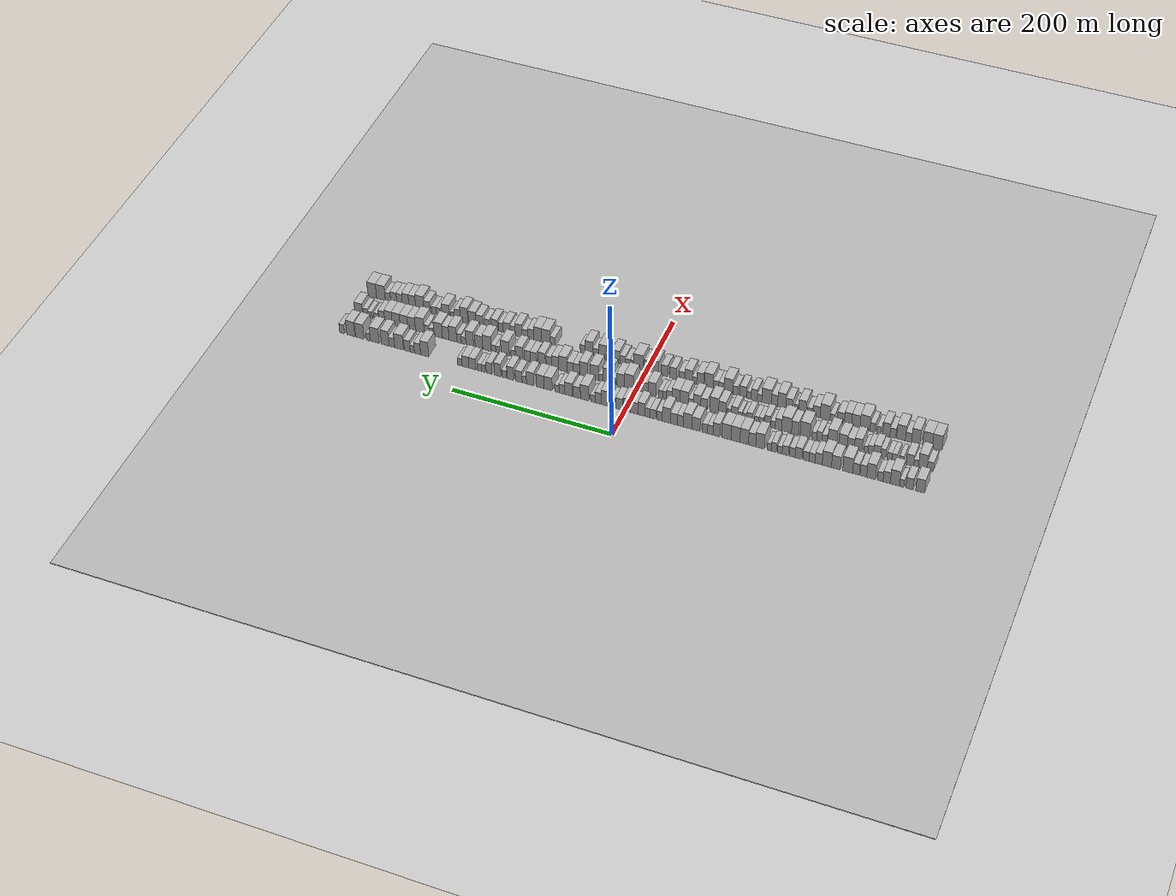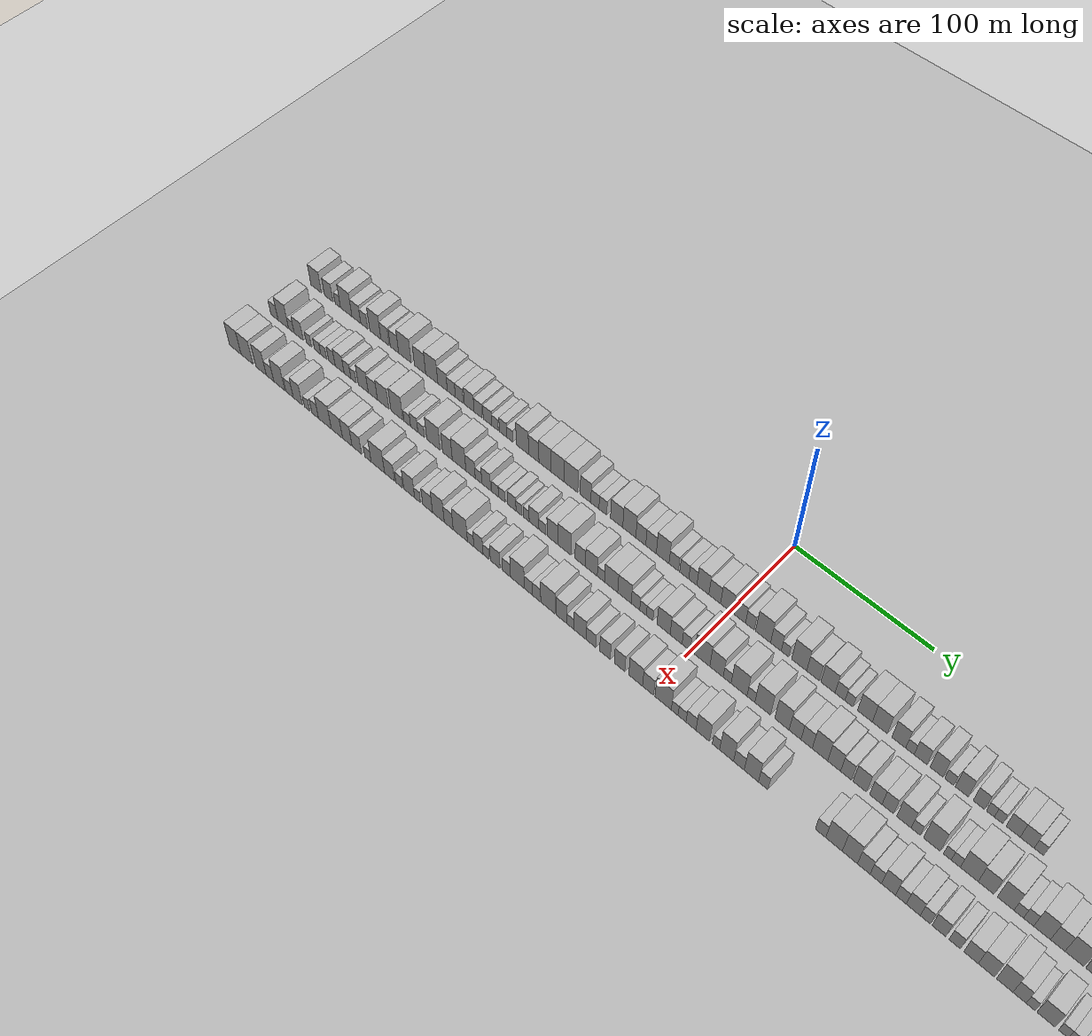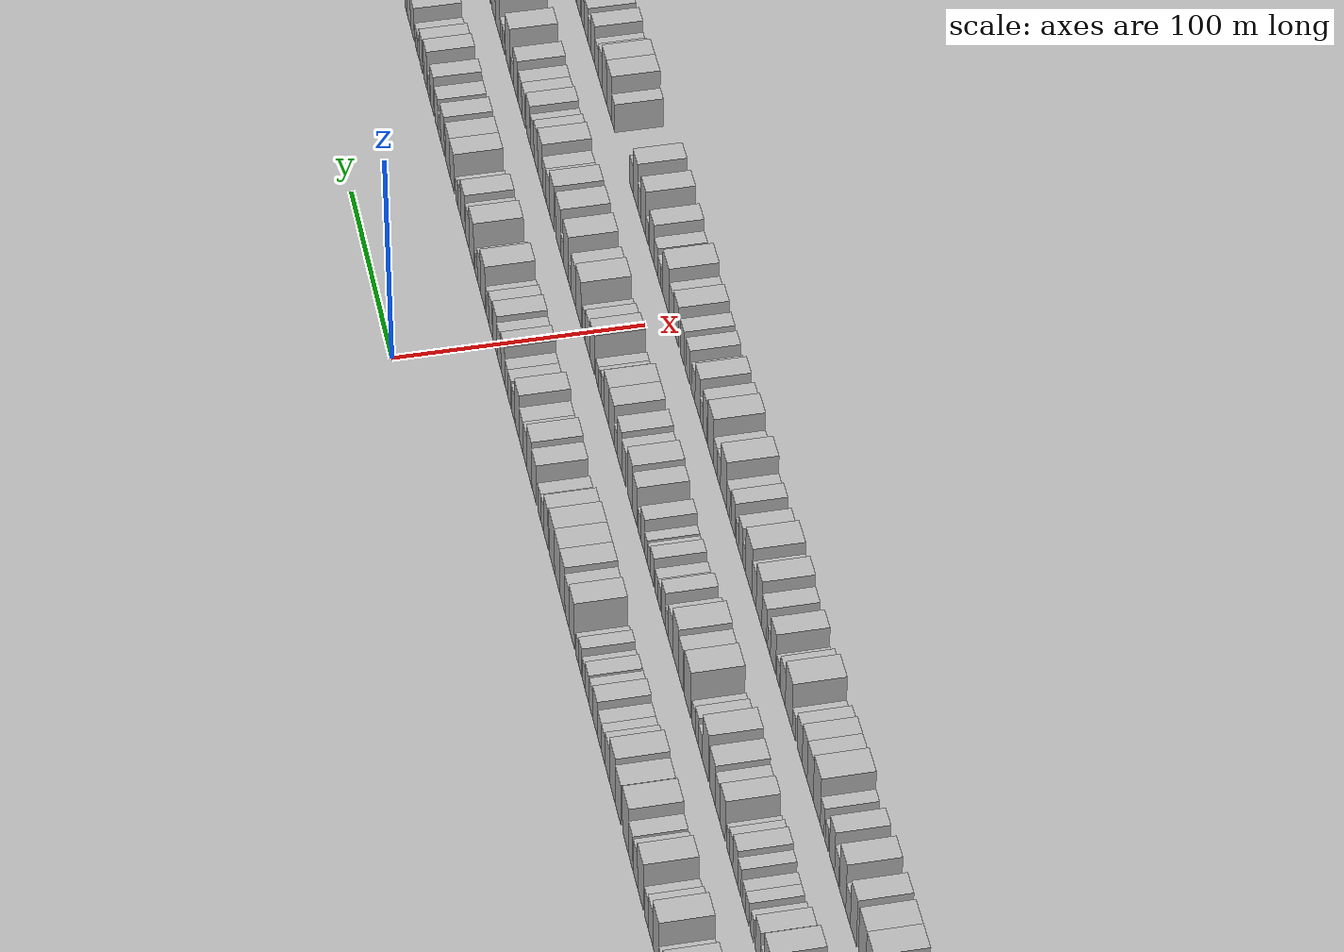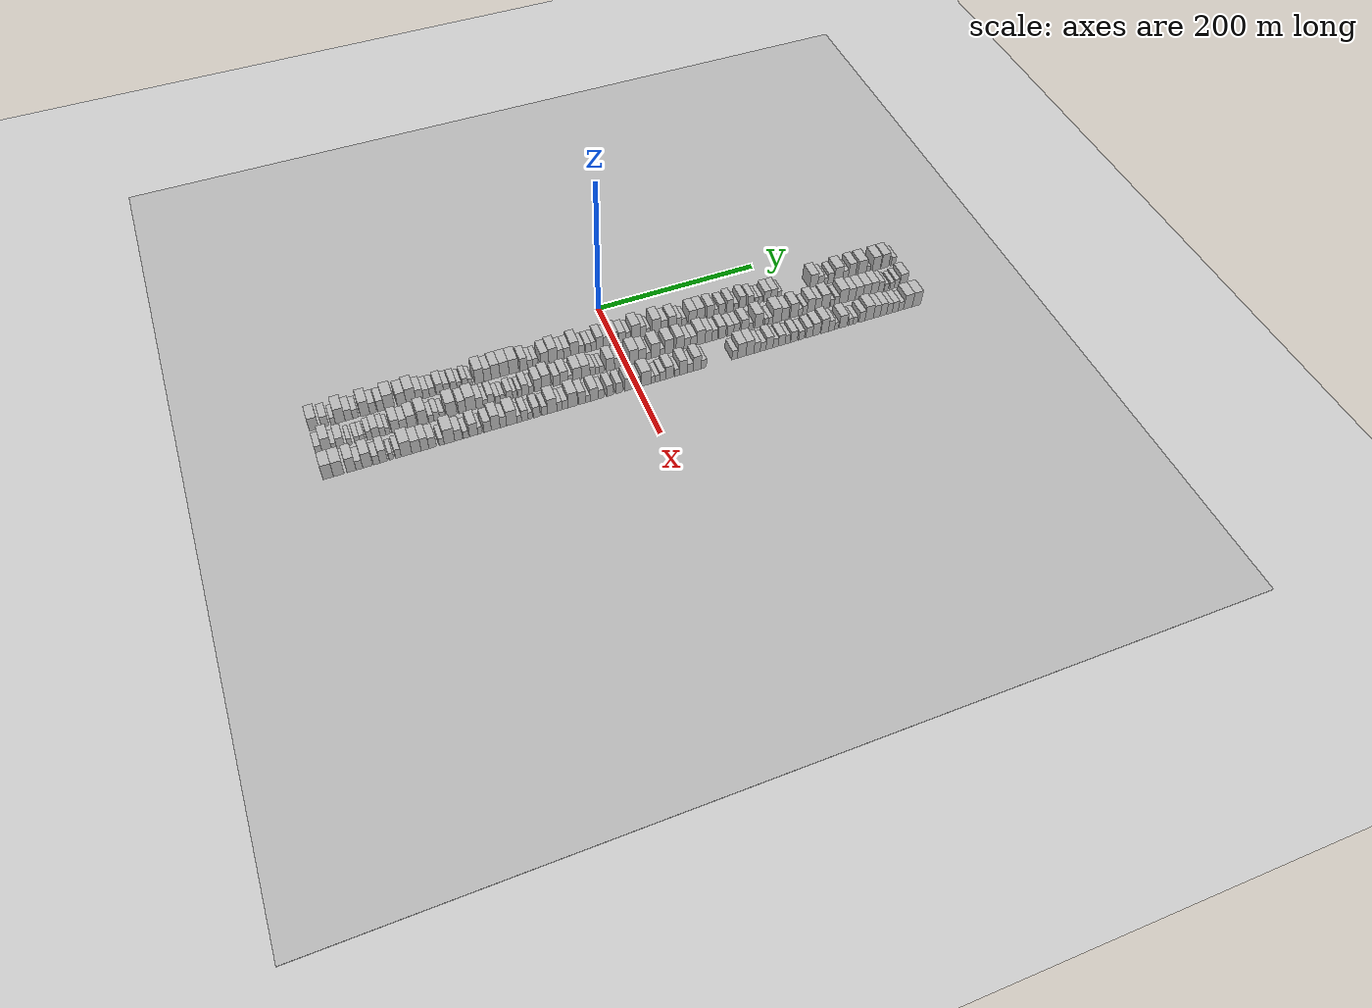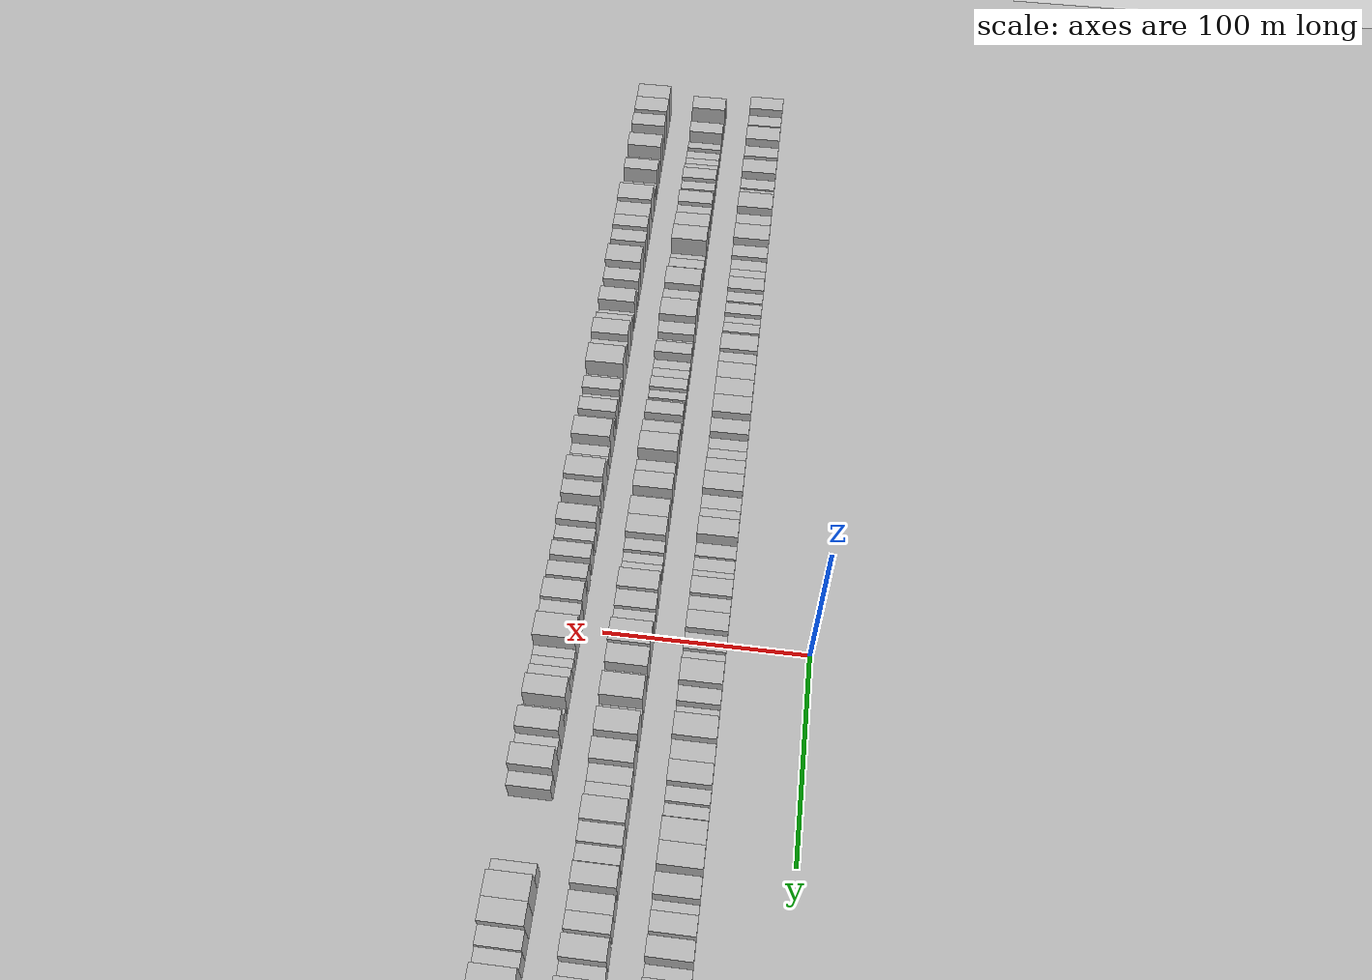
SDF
<?xml version="1.0" encoding="utf-8"?>

<sdf version="1.6">

   <world name="default">

      <gui fullscreen="0">

         <camera name="user_camera">

            <pose>-15 0 4.57585 0 0 0</pose>

            <view_controller>orbit</view_controller>

         </camera>

      </gui>

      <scene>

         <sky>

           <clouds>

             <speed>12</speed>

           </clouds>

         </sky>

         <ambient>0.4 0.4 0.4 1</ambient>

         <background>0.7 0.7 0.7 1</background>

         <shadows>1</shadows>

      </scene>

      <gravity>0 0 -9.8066</gravity>

      <magnetic_field>6e-06 2.3e-05 -4.2e-05</magnetic_field>

      <physics default="0" name="default_physics" type="ode">

         <ode>

            <solver>

               <type>quick</type>

               <iters>10</iters>

               <sor>1.0</sor>

               <use_dynamic_moi_rescaling>0</use_dynamic_moi_rescaling>

            </solver>

            <constraints>

               <cfm>0</cfm>

               <erp>0.2</erp>

               <contact_max_correcting_vel>100</contact_max_correcting_vel>

               <contact_surface_layer>0.001</contact_surface_layer>

            </constraints>

         </ode>

         <max_step_size>0.004</max_step_size>

         <real_time_factor>1</real_time_factor>

         <real_time_update_rate>250</real_time_update_rate>

      </physics>

      <light name="sun" type="directional">

         <cast_shadows>1</cast_shadows>

         <pose>0 0 10 0 0 0</pose>

         <diffuse>0.8 0.8 0.8 1</diffuse>

         <specular>0.2 0.2 0.2 1</specular>

         <attenuation>

            <range>1000</range>

            <constant>0.9</constant>

            <linear>0.01</linear>

            <quadratic>0.001</quadratic>

         </attenuation>

         <direction>-0.5 0.1 -0.9</direction>

      </light>

      <include>

         <name>ground_plane_1</name>

         <uri>model://HANNAS_ground_plane</uri>

         <pose>0 0 0  0 0 0</pose>

      </include>

      <include>

         <name>ground_plane_2</name>

         <uri>model://HANNAS_ground_plane</uri>

         <pose>100 0 0  0 0 0</pose>

      </include>

      <model name="building_1">

         <static>1</static>

         <pose frame="">50.0000 -354.8118 0 0.000000 0.000000 0.000000</pose>

         <link name="link">

            <pose frame="">0 0 10.50 0 0 0</pose>

            <collision name="collision">

               <geometry>

                  <box>

                     <size>20.0000 10.3764 21.0000</size>

                  </box>

               </geometry>

               <max_contacts>10</max_contacts>

               <surface>

                  <contact>

                     <ode/>

                  </contact>

                  <bounce/>

                  <friction>

                     <torsional>

                        <ode/>

                     </torsional>

                     <ode/>

                  </friction>

               </surface>

            </collision>

            <visual name="visual">

               <cast_shadows>0</cast_shadows>

               <geometry>

                  <box>

                     <size>20.0000 10.3764 21.0000</size>

                  </box>

               </geometry>

               <material>

                  <script>

                     <uri>model://HANNAS_wall/materials/scripts</uri>

                     <uri>model://HANNAS_wall/materials/textures</uri>

                     <name>vrc/HANNAS_wall</name>

                  </script>

               </material>

            </visual>

            <self_collide>0</self_collide>

            <enable_wind>0</enable_wind>

            <kinematic>0</kinematic>

         </link>

      </model>

      <model name="building_2">

         <static>1</static>

         <pose frame="">50.0000 -342.4042 0 0.000000 0.000000 0.000000</pose>

         <link name="link">

            <pose frame="">0 0 9.00 0 0 0</pose>

            <collision name="collision">

               <geometry>

                  <box>

                     <size>20.0000 8.4388 18.0000</size>

                  </box>

               </geometry>

               <max_contacts>10</max_contacts>

               <surface>

                  <contact>

                     <ode/>

                  </contact>

                  <bounce/>

                  <friction>

                     <torsional>

                        <ode/>

                     </torsional>

                     <ode/>

                  </friction>

               </surface>

            </collision>

            <visual name="visual">

               <cast_shadows>0</cast_shadows>

               <geometry>

                  <box>

                     <size>20.0000 8.4388 18.0000</size>

                  </box>

               </geometry>

               <material>

                  <script>

                     <uri>model://HANNAS_wall/materials/scripts</uri>

                     <uri>model://HANNAS_wall/materials/textures</uri>

                     <name>vrc/HANNAS_wall</name>

                  </script>

               </material>

            </visual>

            <self_collide>0</self_collide>

            <enable_wind>0</enable_wind>

            <kinematic>0</kinematic>

         </link>

      </model>

      <model name="building_3">

         <static>1</static>

         <pose frame="">50.0000 -333.5598 0 0.000000 0.000000 0.000000</pose>

         <link name="link">

            <pose frame="">0 0 6.00 0 0 0</pose>

            <collision name="collision">

               <geometry>

                  <box>

                     <size>20.0000 5.2500 12.0000</size>

                  </box>

               </geometry>

               <max_contacts>10</max_contacts>

               <surface>

                  <contact>

                     <ode/>

                  </contact>

                  <bounce/>

                  <friction>

                     <torsional>

                        <ode/>

                     </torsional>

                     <ode/>

                  </friction>

               </surface>

            </collision>

            <visual name="visual">

               <cast_shadows>0</cast_shadows>

               <geometry>

                  <box>

                     <size>20.0000 5.2500 12.0000</size>

                  </box>

               </geometry>

               <material>

                  <script>

                     <uri>model://HANNAS_wall/materials/scripts</uri>

                     <uri>model://HANNAS_wall/materials/textures</uri>

                     <name>vrc/HANNAS_wall</name>

                  </script>

               </material>

            </visual>

            <self_collide>0</self_collide>

            <enable_wind>0</enable_wind>

            <kinematic>0</kinematic>

         </link>

      </model>

      <model name="building_4">

         <static>1</static>

         <pose frame="">50.0000 -325.4387 0 0.000000 0.000000 0.000000</pose>

         <link name="link">

            <pose frame="">0 0 12.00 0 0 0</pose>

            <collision name="collision">

               <geometry>

                  <box>

                     <size>20.0000 10.9921 24.0000</size>

                  </box>

               </geometry>

               <max_contacts>10</max_contacts>

               <surface>

                  <contact>

                     <ode/>

                  </contact>

                  <bounce/>

                  <friction>

                     <torsional>

                        <ode/>

                     </torsional>

                     <ode/>

                  </friction>

               </surface>

            </collision>

            <visual name="visual">

               <cast_shadows>0</cast_shadows>

               <geometry>

                  <box>

                     <size>20.0000 10.9921 24.0000</size>

                  </box>

               </geometry>

               <material>

                  <script>

                     <uri>model://HANNAS_wall/materials/scripts</uri>

                     <uri>model://HANNAS_wall/materials/textures</uri>

                     <name>vrc/HANNAS_wall</name>

                  </script>

               </material>

            </visual>

            <self_collide>0</self_collide>

            <enable_wind>0</enable_wind>

            <kinematic>0</kinematic>

         </link>

      </model>

      <model name="building_5">

         <static>1</static>

         <pose frame="">50.0000 -315.6908 0 0.000000 0.000000 0.000000</pose>

         <link name="link">

            <pose frame="">0 0 9.00 0 0 0</pose>

            <collision name="collision">

               <geometry>

                  <box>

                     <size>20.0000 8.5036 18.0000</size>

                  </box>

               </geometry>

               <max_contacts>10</max_contacts>

               <surface>

                  <contact>

                     <ode/>

                  </contact>

                  <bounce/>

                  <friction>

                     <torsional>

                        <ode/>

                     </torsional>

                     <ode/>

                  </friction>

               </surface>

            </collision>

            <visual name="visual">

               <cast_shadows>0</cast_shadows>

               <geometry>

                  <box>

                     <size>20.0000 8.5036 18.0000</size>

                  </box>

               </geometry>

               <material>

                  <script>

                     <uri>model://HANNAS_wall/materials/scripts</uri>

                     <uri>model://HANNAS_wall/materials/textures</uri>

                     <name>vrc/HANNAS_wall</name>

                  </script>

               </material>

            </visual>

            <self_collide>0</self_collide>

            <enable_wind>0</enable_wind>

            <kinematic>0</kinematic>

         </link>

      </model>

      <model name="building_6">

         <static>1</static>

         <pose frame="">50.0000 -308.1263 0 0.000000 0.000000 0.000000</pose>

         <link name="link">

            <pose frame="">0 0 7.50 0 0 0</pose>

            <collision name="collision">

               <geometry>

                  <box>

                     <size>20.0000 6.6255 15.0000</size>

                  </box>

               </geometry>

               <max_contacts>10</max_contacts>

               <surface>

                  <contact>

                     <ode/>

                  </contact>

                  <bounce/>

                  <friction>

                     <torsional>

                        <ode/>

                     </torsional>

                     <ode/>

                  </friction>

               </surface>

            </collision>

            <visual name="visual">

               <cast_shadows>0</cast_shadows>

               <geometry>

                  <box>

                     <size>20.0000 6.6255 15.0000</size>

                  </box>

               </geometry>

               <material>

                  <script>

                     <uri>model://HANNAS_wall/materials/scripts</uri>

                     <uri>model://HANNAS_wall/materials/textures</uri>

                     <name>vrc/HANNAS_wall</name>

                  </script>

               </material>

            </visual>

            <self_collide>0</self_collide>

            <enable_wind>0</enable_wind>

            <kinematic>0</kinematic>

         </link>

      </model>

      <model name="building_7">

         <static>1</static>

         <pose frame="">50.0000 -297.5512 0 0.000000 0.000000 0.000000</pose>

         <link name="link">

            <pose frame="">0 0 12.00 0 0 0</pose>

            <collision name="collision">

               <geometry>

                  <box>

                     <size>20.0000 10.5247 24.0000</size>

                  </box>

               </geometry>

               <max_contacts>10</max_contacts>

               <surface>

                  <contact>

                     <ode/>

                  </contact>

                  <bounce/>

                  <friction>

                     <torsional>

                        <ode/>

                     </torsional>

                     <ode/>

                  </friction>

               </surface>

            </collision>

            <visual name="visual">

               <cast_shadows>0</cast_shadows>

               <geometry>

                  <box>

                     <size>20.0000 10.5247 24.0000</size>

                  </box>

               </geometry>

               <material>

                  <script>

                     <uri>model://HANNAS_wall/materials/scripts</uri>

                     <uri>model://HANNAS_wall/materials/textures</uri>

                     <name>vrc/HANNAS_wall</name>

                  </script>

               </material>

            </visual>

            <self_collide>0</self_collide>

            <enable_wind>0</enable_wind>

            <kinematic>0</kinematic>

         </link>

      </model>

      <model name="building_8">

         <static>1</static>

         <pose frame="">50.0000 -288.3917 0 0.000000 0.000000 0.000000</pose>

         <link name="link">

            <pose frame="">0 0 9.00 0 0 0</pose>

            <collision name="collision">

               <geometry>

                  <box>

                     <size>20.0000 7.7943 18.0000</size>

                  </box>

               </geometry>

               <max_contacts>10</max_contacts>

               <surface>

                  <contact>

                     <ode/>

                  </contact>

                  <bounce/>

                  <friction>

                     <torsional>

                        <ode/>

                     </torsional>

                     <ode/>

                  </friction>

               </surface>

            </collision>

            <visual name="visual">

               <cast_shadows>0</cast_shadows>

               <geometry>

                  <box>

                     <size>20.0000 7.7943 18.0000</size>

                  </box>

               </geometry>

               <material>

                  <script>

                     <uri>model://HANNAS_wall/materials/scripts</uri>

                     <uri>model://HANNAS_wall/materials/textures</uri>

                     <name>vrc/HANNAS_wall</name>

                  </script>

               </material>

            </visual>

            <self_collide>0</self_collide>

            <enable_wind>0</enable_wind>

            <kinematic>0</kinematic>

         </link>

      </model>

      <model name="building_9">

         <static>1</static>

         <pose frame="">50.0000 -279.6073 0 0.000000 0.000000 0.000000</pose>

         <link name="link">

            <pose frame="">0 0 9.00 0 0 0</pose>

            <collision name="collision">

               <geometry>

                  <box>

                     <size>20.0000 7.7746 18.0000</size>

                  </box>

               </geometry>

               <max_contacts>10</max_contacts>

               <surface>

                  <contact>

                     <ode/>

                  </contact>

                  <bounce/>

                  <friction>

                     <torsional>

                        <ode/>

                     </torsional>

                     <ode/>

                  </friction>

               </surface>

            </collision>

            <visual name="visual">

               <cast_shadows>0</cast_shadows>

               <geometry>

                  <box>

                     <size>20.0000 7.7746 18.0000</size>

                  </box>

               </geometry>

               <material>

                  <script>

                     <uri>model://HANNAS_wall/materials/scripts</uri>

                     <uri>model://HANNAS_wall/materials/textures</uri>

                     <name>vrc/HANNAS_wall</name>

                  </script>

               </material>

            </visual>

            <self_collide>0</self_collide>

            <enable_wind>0</enable_wind>

            <kinematic>0</kinematic>

         </link>

      </model>

      <model name="building_10">

         <static>1</static>

         <pose frame="">50.0000 -269.8928 0 0.000000 0.000000 0.000000</pose>

         <link name="link">

            <pose frame="">0 0 12.00 0 0 0</pose>

            <collision name="collision">

               <geometry>

                  <box>

                     <size>20.0000 11.6544 24.0000</size>

                  </box>

               </geometry>

               <max_contacts>10</max_contacts>

               <surface>

                  <contact>

                     <ode/>

                  </contact>

                  <bounce/>

                  <friction>

                     <torsional>

                        <ode/>

                     </torsional>

                     <ode/>

                  </friction>

               </surface>

            </collision>

            <visual name="visual">

               <cast_shadows>0</cast_shadows>

               <geometry>

                  <box>

                     <size>20.0000 11.6544 24.0000</size>

                  </box>

               </geometry>

               <material>

                  <script>

                     <uri>model://HANNAS_wall/materials/scripts</uri>

                     <uri>model://HANNAS_wall/materials/textures</uri>

                     <name>vrc/HANNAS_wall</name>

                  </script>

               </material>

            </visual>

            <self_collide>0</self_collide>

            <enable_wind>0</enable_wind>

            <kinematic>0</kinematic>

         </link>

      </model>

      <model name="building_11">

         <static>1</static>

         <pose frame="">50.0000 -255.9032 0 0.000000 0.000000 0.000000</pose>

         <link name="link">

            <pose frame="">0 0 10.50 0 0 0</pose>

            <collision name="collision">

               <geometry>

                  <box>

                     <size>20.0000 10.3248 21.0000</size>

                  </box>

               </geometry>

               <max_contacts>10</max_contacts>

               <surface>

                  <contact>

                     <ode/>

                  </contact>

                  <bounce/>

                  <friction>

                     <torsional>

                        <ode/>

                     </torsional>

                     <ode/>

                  </friction>

               </surface>

            </collision>

            <visual name="visual">

               <cast_shadows>0</cast_shadows>

               <geometry>

                  <box>

                     <size>20.0000 10.3248 21.0000</size>

                  </box>

               </geometry>

               <material>

                  <script>

                     <uri>model://HANNAS_wall/materials/scripts</uri>

                     <uri>model://HANNAS_wall/materials/textures</uri>

                     <name>vrc/HANNAS_wall</name>

                  </script>

               </material>

            </visual>

            <self_collide>0</self_collide>

            <enable_wind>0</enable_wind>

            <kinematic>0</kinematic>

         </link>

      </model>

      <model name="building_12">

         <static>1</static>

         <pose frame="">50.0000 -245.2135 0 0.000000 0.000000 0.000000</pose>

         <link name="link">

            <pose frame="">0 0 12.00 0 0 0</pose>

            <collision name="collision">

               <geometry>

                  <box>

                     <size>20.0000 11.0546 24.0000</size>

                  </box>

               </geometry>

               <max_contacts>10</max_contacts>

               <surface>

                  <contact>

                     <ode/>

                  </contact>

                  <bounce/>

                  <friction>

                     <torsional>

                        <ode/>

                     </torsional>

                     <ode/>

                  </friction>

               </surface>

            </collision>

            <visual name="visual">

               <cast_shadows>0</cast_shadows>

               <geometry>

                  <box>

                     <size>20.0000 11.0546 24.0000</size>

                  </box>

               </geometry>

               <material>

                  <script>

                     <uri>model://HANNAS_wall/materials/scripts</uri>

                     <uri>model://HANNAS_wall/materials/textures</uri>

                     <name>vrc/HANNAS_wall</name>

                  </script>

               </material>

            </visual>

            <self_collide>0</self_collide>

            <enable_wind>0</enable_wind>

            <kinematic>0</kinematic>

         </link>

      </model>

      <model name="building_13">

         <static>1</static>

         <pose frame="">50.0000 -235.4273 0 0.000000 0.000000 0.000000</pose>

         <link name="link">

            <pose frame="">0 0 9.00 0 0 0</pose>

            <collision name="collision">

               <geometry>

                  <box>

                     <size>20.0000 8.5178 18.0000</size>

                  </box>

               </geometry>

               <max_contacts>10</max_contacts>

               <surface>

                  <contact>

                     <ode/>

                  </contact>

                  <bounce/>

                  <friction>

                     <torsional>

                        <ode/>

                     </torsional>

                     <ode/>

                  </friction>

               </surface>

            </collision>

            <visual name="visual">

               <cast_shadows>0</cast_shadows>

               <geometry>

                  <box>

                     <size>20.0000 8.5178 18.0000</size>

                  </box>

               </geometry>

               <material>

                  <script>

                     <uri>model://HANNAS_wall/materials/scripts</uri>

                     <uri>model://HANNAS_wall/materials/textures</uri>

                     <name>vrc/HANNAS_wall</name>

                  </script>

               </material>

            </visual>

            <self_collide>0</self_collide>

            <enable_wind>0</enable_wind>

            <kinematic>0</kinematic>

         </link>

      </model>

      <model name="building_14">

         <static>1</static>

         <pose frame="">50.0000 -227.5237 0 0.000000 0.000000 0.000000</pose>

         <link name="link">

            <pose frame="">0 0 7.50 0 0 0</pose>

            <collision name="collision">

               <geometry>

                  <box>

                     <size>20.0000 7.2894 15.0000</size>

                  </box>

               </geometry>

               <max_contacts>10</max_contacts>

               <surface>

                  <contact>

                     <ode/>

                  </contact>

                  <bounce/>

                  <friction>

                     <torsional>

                        <ode/>

                     </torsional>

                     <ode/>

                  </friction>

               </surface>

            </collision>

            <visual name="visual">

               <cast_shadows>0</cast_shadows>

               <geometry>

                  <box>

                     <size>20.0000 7.2894 15.0000</size>

                  </box>

               </geometry>

               <material>

                  <script>

                     <uri>model://HANNAS_wall/materials/scripts</uri>

                     <uri>model://HANNAS_wall/materials/textures</uri>

                     <name>vrc/HANNAS_wall</name>

                  </script>

               </material>

            </visual>

            <self_collide>0</self_collide>

            <enable_wind>0</enable_wind>

            <kinematic>0</kinematic>

         </link>

      </model>

      <model name="building_15">

         <static>1</static>

         <pose frame="">50.0000 -220.3886 0 0.000000 0.000000 0.000000</pose>

         <link name="link">

            <pose frame="">0 0 7.50 0 0 0</pose>

            <collision name="collision">

               <geometry>

                  <box>

                     <size>20.0000 6.9809 15.0000</size>

                  </box>

               </geometry>

               <max_contacts>10</max_contacts>

               <surface>

                  <contact>

                     <ode/>

                  </contact>

                  <bounce/>

                  <friction>

                     <torsional>

                        <ode/>

                     </torsional>

                     <ode/>

                  </friction>

               </surface>

            </collision>

            <visual name="visual">

               <cast_shadows>0</cast_shadows>

               <geometry>

                  <box>

                     <size>20.0000 6.9809 15.0000</size>

                  </box>

               </geometry>

               <material>

                  <script>

                     <uri>model://HANNAS_wall/materials/scripts</uri>

                     <uri>model://HANNAS_wall/materials/textures</uri>

                     <name>vrc/HANNAS_wall</name>

                  </script>

               </material>

            </visual>

            <self_collide>0</self_collide>

            <enable_wind>0</enable_wind>

            <kinematic>0</kinematic>

         </link>

      </model>

      <model name="building_16">

         <static>1</static>

         <pose frame="">50.0000 -211.5945 0 0.000000 0.000000 0.000000</pose>

         <link name="link">

            <pose frame="">0 0 9.00 0 0 0</pose>

            <collision name="collision">

               <geometry>

                  <box>

                     <size>20.0000 8.6072 18.0000</size>

                  </box>

               </geometry>

               <max_contacts>10</max_contacts>

               <surface>

                  <contact>

                     <ode/>

                  </contact>

                  <bounce/>

                  <friction>

                     <torsional>

                        <ode/>

                     </torsional>

                     <ode/>

                  </friction>

               </surface>

            </collision>

            <visual name="visual">

               <cast_shadows>0</cast_shadows>

               <geometry>

                  <box>

                     <size>20.0000 8.6072 18.0000</size>

                  </box>

               </geometry>

               <material>

                  <script>

                     <uri>model://HANNAS_wall/materials/scripts</uri>

                     <uri>model://HANNAS_wall/materials/textures</uri>

                     <name>vrc/HANNAS_wall</name>

                  </script>

               </material>

            </visual>

            <self_collide>0</self_collide>

            <enable_wind>0</enable_wind>

            <kinematic>0</kinematic>

         </link>

      </model>

      <model name="building_17">

         <static>1</static>

         <pose frame="">50.0000 -203.7784 0 0.000000 0.000000 0.000000</pose>

         <link name="link">

            <pose frame="">0 0 7.50 0 0 0</pose>

            <collision name="collision">

               <geometry>

                  <box>

                     <size>20.0000 7.0250 15.0000</size>

                  </box>

               </geometry>

               <max_contacts>10</max_contacts>

               <surface>

                  <contact>

                     <ode/>

                  </contact>

                  <bounce/>

                  <friction>

                     <torsional>

                        <ode/>

                     </torsional>

                     <ode/>

                  </friction>

               </surface>

            </collision>

            <visual name="visual">

               <cast_shadows>0</cast_shadows>

               <geometry>

                  <box>

                     <size>20.0000 7.0250 15.0000</size>

                  </box>

               </geometry>

               <material>

                  <script>

                     <uri>model://HANNAS_wall/materials/scripts</uri>

                     <uri>model://HANNAS_wall/materials/textures</uri>

                     <name>vrc/HANNAS_wall</name>

                  </script>

               </material>

            </visual>

            <self_collide>0</self_collide>

            <enable_wind>0</enable_wind>

            <kinematic>0</kinematic>

         </link>

      </model>

      <model name="building_18">

         <static>1</static>

         <pose frame="">50.0000 -195.5371 0 0.000000 0.000000 0.000000</pose>

         <link name="link">

            <pose frame="">0 0 7.50 0 0 0</pose>

            <collision name="collision">

               <geometry>

                  <box>

                     <size>20.0000 7.4577 15.0000</size>

                  </box>

               </geometry>

               <max_contacts>10</max_contacts>

               <surface>

                  <contact>

                     <ode/>

                  </contact>

                  <bounce/>

                  <friction>

                     <torsional>

                        <ode/>

                     </torsional>

                     <ode/>

                  </friction>

               </surface>

            </collision>

            <visual name="visual">

               <cast_shadows>0</cast_shadows>

               <geometry>

                  <box>

                     <size>20.0000 7.4577 15.0000</size>

                  </box>

               </geometry>

               <material>

                  <script>

                     <uri>model://HANNAS_wall/materials/scripts</uri>

                     <uri>model://HANNAS_wall/materials/textures</uri>

                     <name>vrc/HANNAS_wall</name>

                  </script>

               </material>

            </visual>

            <self_collide>0</self_collide>

            <enable_wind>0</enable_wind>

            <kinematic>0</kinematic>

         </link>

      </model>

      <model name="building_19">

         <static>1</static>

         <pose frame="">50.0000 -189.0080 0 0.000000 0.000000 0.000000</pose>

         <link name="link">

            <pose frame="">0 0 6.00 0 0 0</pose>

            <collision name="collision">

               <geometry>

                  <box>

                     <size>20.0000 5.6005 12.0000</size>

                  </box>

               </geometry>

               <max_contacts>10</max_contacts>

               <surface>

                  <contact>

                     <ode/>

                  </contact>

                  <bounce/>

                  <friction>

                     <torsional>

                        <ode/>

                     </torsional>

                     <ode/>

                  </friction>

               </surface>

            </collision>

            <visual name="visual">

               <cast_shadows>0</cast_shadows>

               <geometry>

                  <box>

                     <size>20.0000 5.6005 12.0000</size>

                  </box>

               </geometry>

               <material>

                  <script>

                     <uri>model://HANNAS_wall/materials/scripts</uri>

                     <uri>model://HANNAS_wall/materials/textures</uri>

                     <name>vrc/HANNAS_wall</name>

                  </script>

               </material>

            </visual>

            <self_collide>0</self_collide>

            <enable_wind>0</enable_wind>

            <kinematic>0</kinematic>

         </link>

      </model>

      <model name="building_20">

         <static>1</static>

         <pose frame="">50.0000 -182.0511 0 0.000000 0.000000 0.000000</pose>

         <link name="link">

            <pose frame="">0 0 7.50 0 0 0</pose>

            <collision name="collision">

               <geometry>

                  <box>

                     <size>20.0000 6.3132 15.0000</size>

                  </box>

               </geometry>

               <max_contacts>10</max_contacts>

               <surface>

                  <contact>

                     <ode/>

                  </contact>

                  <bounce/>

                  <friction>

                     <torsional>

                        <ode/>

                     </torsional>

                     <ode/>

                  </friction>

               </surface>

            </collision>

            <visual name="visual">

               <cast_shadows>0</cast_shadows>

               <geometry>

                  <box>

                     <size>20.0000 6.3132 15.0000</size>

                  </box>

               </geometry>

               <material>

                  <script>

                     <uri>model://HANNAS_wall/materials/scripts</uri>

                     <uri>model://HANNAS_wall/materials/textures</uri>

                     <name>vrc/HANNAS_wall</name>

                  </script>

               </material>

            </visual>

            <self_collide>0</self_collide>

            <enable_wind>0</enable_wind>

            <kinematic>0</kinematic>

         </link>

      </model>

      <model name="building_21">

         <static>1</static>

         <pose frame="">50.0000 -176.2646 0 0.000000 0.000000 0.000000</pose>

         <link name="link">

            <pose frame="">0 0 6.00 0 0 0</pose>

            <collision name="collision">

               <geometry>

                  <box>

                     <size>20.0000 5.2599 12.0000</size>

                  </box>

               </geometry>

               <max_contacts>10</max_contacts>

               <surface>

                  <contact>

                     <ode/>

                  </contact>

                  <bounce/>

                  <friction>

                     <torsional>

                        <ode/>

                     </torsional>

                     <ode/>

                  </friction>

               </surface>

            </collision>

            <visual name="visual">

               <cast_shadows>0</cast_shadows>

               <geometry>

                  <box>

                     <size>20.0000 5.2599 12.0000</size>

                  </box>

               </geometry>

               <material>

                  <script>

                     <uri>model://HANNAS_wall/materials/scripts</uri>

                     <uri>model://HANNAS_wall/materials/textures</uri>

                     <name>vrc/HANNAS_wall</name>

                  </script>

               </material>

            </visual>

            <self_collide>0</self_collide>

            <enable_wind>0</enable_wind>

            <kinematic>0</kinematic>

         </link>

      </model>

      <model name="building_22">

         <static>1</static>

         <pose frame="">50.0000 -165.3930 0 0.000000 0.000000 0.000000</pose>

         <link name="link">

            <pose frame="">0 0 12.00 0 0 0</pose>

            <collision name="collision">

               <geometry>

                  <box>

                     <size>20.0000 10.4833 24.0000</size>

                  </box>

               </geometry>

               <max_contacts>10</max_contacts>

               <surface>

                  <contact>

                     <ode/>

                  </contact>

                  <bounce/>

                  <friction>

                     <torsional>

                        <ode/>

                     </torsional>

                     <ode/>

                  </friction>

               </surface>

            </collision>

            <visual name="visual">

               <cast_shadows>0</cast_shadows>

               <geometry>

                  <box>

                     <size>20.0000 10.4833 24.0000</size>

                  </box>

               </geometry>

               <material>

                  <script>

                     <uri>model://HANNAS_wall/materials/scripts</uri>

                     <uri>model://HANNAS_wall/materials/textures</uri>

                     <name>vrc/HANNAS_wall</name>

                  </script>

               </material>

            </visual>

            <self_collide>0</self_collide>

            <enable_wind>0</enable_wind>

            <kinematic>0</kinematic>

         </link>

      </model>

      <model name="building_23">

         <static>1</static>

         <pose frame="">50.0000 -155.7915 0 0.000000 0.000000 0.000000</pose>

         <link name="link">

            <pose frame="">0 0 10.50 0 0 0</pose>

            <collision name="collision">

               <geometry>

                  <box>

                     <size>20.0000 8.7197 21.0000</size>

                  </box>

               </geometry>

               <max_contacts>10</max_contacts>

               <surface>

                  <contact>

                     <ode/>

                  </contact>

                  <bounce/>

                  <friction>

                     <torsional>

                        <ode/>

                     </torsional>

                     <ode/>

                  </friction>

               </surface>

            </collision>

            <visual name="visual">

               <cast_shadows>0</cast_shadows>

               <geometry>

                  <box>

                     <size>20.0000 8.7197 21.0000</size>

                  </box>

               </geometry>

               <material>

                  <script>

                     <uri>model://HANNAS_wall/materials/scripts</uri>

                     <uri>model://HANNAS_wall/materials/textures</uri>

                     <name>vrc/HANNAS_wall</name>

                  </script>

               </material>

            </visual>

            <self_collide>0</self_collide>

            <enable_wind>0</enable_wind>

            <kinematic>0</kinematic>

         </link>

      </model>

      <model name="building_24">

         <static>1</static>

         <pose frame="">50.0000 -146.2969 0 0.000000 0.000000 0.000000</pose>

         <link name="link">

            <pose frame="">0 0 12.00 0 0 0</pose>

            <collision name="collision">

               <geometry>

                  <box>

                     <size>20.0000 10.2695 24.0000</size>

                  </box>

               </geometry>

               <max_contacts>10</max_contacts>

               <surface>

                  <contact>

                     <ode/>

                  </contact>

                  <bounce/>

                  <friction>

                     <torsional>

                        <ode/>

                     </torsional>

                     <ode/>

                  </friction>

               </surface>

            </collision>

            <visual name="visual">

               <cast_shadows>0</cast_shadows>

               <geometry>

                  <box>

                     <size>20.0000 10.2695 24.0000</size>

                  </box>

               </geometry>

               <material>

                  <script>

                     <uri>model://HANNAS_wall/materials/scripts</uri>

                     <uri>model://HANNAS_wall/materials/textures</uri>

                     <name>vrc/HANNAS_wall</name>

                  </script>

               </material>

            </visual>

            <self_collide>0</self_collide>

            <enable_wind>0</enable_wind>

            <kinematic>0</kinematic>

         </link>

      </model>

      <model name="building_25">

         <static>1</static>

         <pose frame="">50.0000 -135.6973 0 0.000000 0.000000 0.000000</pose>

         <link name="link">

            <pose frame="">0 0 12.00 0 0 0</pose>

            <collision name="collision">

               <geometry>

                  <box>

                     <size>20.0000 10.9298 24.0000</size>

                  </box>

               </geometry>

               <max_contacts>10</max_contacts>

               <surface>

                  <contact>

                     <ode/>

                  </contact>

                  <bounce/>

                  <friction>

                     <torsional>

                        <ode/>

                     </torsional>

                     <ode/>

                  </friction>

               </surface>

            </collision>

            <visual name="visual">

               <cast_shadows>0</cast_shadows>

               <geometry>

                  <box>

                     <size>20.0000 10.9298 24.0000</size>

                  </box>

               </geometry>

               <material>

                  <script>

                     <uri>model://HANNAS_wall/materials/scripts</uri>

                     <uri>model://HANNAS_wall/materials/textures</uri>

                     <name>vrc/HANNAS_wall</name>

                  </script>

               </material>

            </visual>

            <self_collide>0</self_collide>

            <enable_wind>0</enable_wind>

            <kinematic>0</kinematic>

         </link>

      </model>

      <model name="building_26">

         <static>1</static>

         <pose frame="">50.0000 -124.6595 0 0.000000 0.000000 0.000000</pose>

         <link name="link">

            <pose frame="">0 0 12.00 0 0 0</pose>

            <collision name="collision">

               <geometry>

                  <box>

                     <size>20.0000 11.1458 24.0000</size>

                  </box>

               </geometry>

               <max_contacts>10</max_contacts>

               <surface>

                  <contact>

                     <ode/>

                  </contact>

                  <bounce/>

                  <friction>

                     <torsional>

                        <ode/>

                     </torsional>

                     <ode/>

                  </friction>

               </surface>

            </collision>

            <visual name="visual">

               <cast_shadows>0</cast_shadows>

               <geometry>

                  <box>

                     <size>20.0000 11.1458 24.0000</size>

                  </box>

               </geometry>

               <material>

                  <script>

                     <uri>model://HANNAS_wall/materials/scripts</uri>

                     <uri>model://HANNAS_wall/materials/textures</uri>

                     <name>vrc/HANNAS_wall</name>

                  </script>

               </material>

            </visual>

            <self_collide>0</self_collide>

            <enable_wind>0</enable_wind>

            <kinematic>0</kinematic>

         </link>

      </model>

      <model name="building_27">

         <static>1</static>

         <pose frame="">50.0000 -112.7458 0 0.000000 0.000000 0.000000</pose>

         <link name="link">

            <pose frame="">0 0 10.50 0 0 0</pose>

            <collision name="collision">

               <geometry>

                  <box>

                     <size>20.0000 8.6816 21.0000</size>

                  </box>

               </geometry>

               <max_contacts>10</max_contacts>

               <surface>

                  <contact>

                     <ode/>

                  </contact>

                  <bounce/>

                  <friction>

                     <torsional>

                        <ode/>

                     </torsional>

                     <ode/>

                  </friction>

               </surface>

            </collision>

            <visual name="visual">

               <cast_shadows>0</cast_shadows>

               <geometry>

                  <box>

                     <size>20.0000 8.6816 21.0000</size>

                  </box>

               </geometry>

               <material>

                  <script>

                     <uri>model://HANNAS_wall/materials/scripts</uri>

                     <uri>model://HANNAS_wall/materials/textures</uri>

                     <name>vrc/HANNAS_wall</name>

                  </script>

               </material>

            </visual>

            <self_collide>0</self_collide>

            <enable_wind>0</enable_wind>

            <kinematic>0</kinematic>

         </link>

      </model>

      <model name="building_28">

         <static>1</static>

         <pose frame="">50.0000 -105.1109 0 0.000000 0.000000 0.000000</pose>

         <link name="link">

            <pose frame="">0 0 7.50 0 0 0</pose>

            <collision name="collision">

               <geometry>

                  <box>

                     <size>20.0000 6.5881 15.0000</size>

                  </box>

               </geometry>

               <max_contacts>10</max_contacts>

               <surface>

                  <contact>

                     <ode/>

                  </contact>

                  <bounce/>

                  <friction>

                     <torsional>

                        <ode/>

                     </torsional>

                     <ode/>

                  </friction>

               </surface>

            </collision>

            <visual name="visual">

               <cast_shadows>0</cast_shadows>

               <geometry>

                  <box>

                     <size>20.0000 6.5881 15.0000</size>

                  </box>

               </geometry>

               <material>

                  <script>

                     <uri>model://HANNAS_wall/materials/scripts</uri>

                     <uri>model://HANNAS_wall/materials/textures</uri>

                     <name>vrc/HANNAS_wall</name>

                  </script>

               </material>

            </visual>

            <self_collide>0</self_collide>

            <enable_wind>0</enable_wind>

            <kinematic>0</kinematic>

         </link>

      </model>

      <model name="building_29">

         <static>1</static>

         <pose frame="">50.0000 -98.6793 0 0.000000 0.000000 0.000000</pose>

         <link name="link">

            <pose frame="">0 0 7.50 0 0 0</pose>

            <collision name="collision">

               <geometry>

                  <box>

                     <size>20.0000 6.2752 15.0000</size>

                  </box>

               </geometry>

               <max_contacts>10</max_contacts>

               <surface>

                  <contact>

                     <ode/>

                  </contact>

                  <bounce/>

                  <friction>

                     <torsional>

                        <ode/>

                     </torsional>

                     <ode/>

                  </friction>

               </surface>

            </collision>

            <visual name="visual">

               <cast_shadows>0</cast_shadows>

               <geometry>

                  <box>

                     <size>20.0000 6.2752 15.0000</size>

                  </box>

               </geometry>

               <material>

                  <script>

                     <uri>model://HANNAS_wall/materials/scripts</uri>

                     <uri>model://HANNAS_wall/materials/textures</uri>

                     <name>vrc/HANNAS_wall</name>

                  </script>

               </material>

            </visual>

            <self_collide>0</self_collide>

            <enable_wind>0</enable_wind>

            <kinematic>0</kinematic>

         </link>

      </model>

      <model name="building_30">

         <static>1</static>

         <pose frame="">50.0000 -87.6267 0 0.000000 0.000000 0.000000</pose>

         <link name="link">

            <pose frame="">0 0 10.50 0 0 0</pose>

            <collision name="collision">

               <geometry>

                  <box>

                     <size>20.0000 9.8299 21.0000</size>

                  </box>

               </geometry>

               <max_contacts>10</max_contacts>

               <surface>

                  <contact>

                     <ode/>

                  </contact>

                  <bounce/>

                  <friction>

                     <torsional>

                        <ode/>

                     </torsional>

                     <ode/>

                  </friction>

               </surface>

            </collision>

            <visual name="visual">

               <cast_shadows>0</cast_shadows>

               <geometry>

                  <box>

                     <size>20.0000 9.8299 21.0000</size>

                  </box>

               </geometry>

               <material>

                  <script>

                     <uri>model://HANNAS_wall/materials/scripts</uri>

                     <uri>model://HANNAS_wall/materials/textures</uri>

                     <name>vrc/HANNAS_wall</name>

                  </script>

               </material>

            </visual>

            <self_collide>0</self_collide>

            <enable_wind>0</enable_wind>

            <kinematic>0</kinematic>

         </link>

      </model>

      <model name="building_31">

         <static>1</static>

         <pose frame="">50.0000 -77.5489 0 0.000000 0.000000 0.000000</pose>

         <link name="link">

            <pose frame="">0 0 12.00 0 0 0</pose>

            <collision name="collision">

               <geometry>

                  <box>

                     <size>20.0000 10.3258 24.0000</size>

                  </box>

               </geometry>

               <max_contacts>10</max_contacts>

               <surface>

                  <contact>

                     <ode/>

                  </contact>

                  <bounce/>

                  <friction>

                     <torsional>

                        <ode/>

                     </torsional>

                     <ode/>

                  </friction>

               </surface>

            </collision>

            <visual name="visual">

               <cast_shadows>0</cast_shadows>

               <geometry>

                  <box>

                     <size>20.0000 10.3258 24.0000</size>

                  </box>

               </geometry>

               <material>

                  <script>

                     <uri>model://HANNAS_wall/materials/scripts</uri>

                     <uri>model://HANNAS_wall/materials/textures</uri>

                     <name>vrc/HANNAS_wall</name>

                  </script>

               </material>

            </visual>

            <self_collide>0</self_collide>

            <enable_wind>0</enable_wind>

            <kinematic>0</kinematic>

         </link>

      </model>

      <model name="building_32">

         <static>1</static>

         <pose frame="">50.0000 -68.4582 0 0.000000 0.000000 0.000000</pose>

         <link name="link">

            <pose frame="">0 0 9.00 0 0 0</pose>

            <collision name="collision">

               <geometry>

                  <box>

                     <size>20.0000 7.8557 18.0000</size>

                  </box>

               </geometry>

               <max_contacts>10</max_contacts>

               <surface>

                  <contact>

                     <ode/>

                  </contact>

                  <bounce/>

                  <friction>

                     <torsional>

                        <ode/>

                     </torsional>

                     <ode/>

                  </friction>

               </surface>

            </collision>

            <visual name="visual">

               <cast_shadows>0</cast_shadows>

               <geometry>

                  <box>

                     <size>20.0000 7.8557 18.0000</size>

                  </box>

               </geometry>

               <material>

                  <script>

                     <uri>model://HANNAS_wall/materials/scripts</uri>

                     <uri>model://HANNAS_wall/materials/textures</uri>

                     <name>vrc/HANNAS_wall</name>

                  </script>

               </material>

            </visual>

            <self_collide>0</self_collide>

            <enable_wind>0</enable_wind>

            <kinematic>0</kinematic>

         </link>

      </model>

      <model name="building_33">

         <static>1</static>

         <pose frame="">50.0000 -60.4181 0 0.000000 0.000000 0.000000</pose>

         <link name="link">

            <pose frame="">0 0 9.00 0 0 0</pose>

            <collision name="collision">

               <geometry>

                  <box>

                     <size>20.0000 8.2246 18.0000</size>

                  </box>

               </geometry>

               <max_contacts>10</max_contacts>

               <surface>

                  <contact>

                     <ode/>

                  </contact>

                  <bounce/>

                  <friction>

                     <torsional>

                        <ode/>

                     </torsional>

                     <ode/>

                  </friction>

               </surface>

            </collision>

            <visual name="visual">

               <cast_shadows>0</cast_shadows>

               <geometry>

                  <box>

                     <size>20.0000 8.2246 18.0000</size>

                  </box>

               </geometry>

               <material>

                  <script>

                     <uri>model://HANNAS_wall/materials/scripts</uri>

                     <uri>model://HANNAS_wall/materials/textures</uri>

                     <name>vrc/HANNAS_wall</name>

                  </script>

               </material>

            </visual>

            <self_collide>0</self_collide>

            <enable_wind>0</enable_wind>

            <kinematic>0</kinematic>

         </link>

      </model>

      <model name="building_34">

         <static>1</static>

         <pose frame="">50.0000 -51.3394 0 0.000000 0.000000 0.000000</pose>

         <link name="link">

            <pose frame="">0 0 12.00 0 0 0</pose>

            <collision name="collision">

               <geometry>

                  <box>

                     <size>20.0000 9.9328 24.0000</size>

                  </box>

               </geometry>

               <max_contacts>10</max_contacts>

               <surface>

                  <contact>

                     <ode/>

                  </contact>

                  <bounce/>

                  <friction>

                     <torsional>

                        <ode/>

                     </torsional>

                     <ode/>

                  </friction>

               </surface>

            </collision>

            <visual name="visual">

               <cast_shadows>0</cast_shadows>

               <geometry>

                  <box>

                     <size>20.0000 9.9328 24.0000</size>

                  </box>

               </geometry>

               <material>

                  <script>

                     <uri>model://HANNAS_wall/materials/scripts</uri>

                     <uri>model://HANNAS_wall/materials/textures</uri>

                     <name>vrc/HANNAS_wall</name>

                  </script>

               </material>

            </visual>

            <self_collide>0</self_collide>

            <enable_wind>0</enable_wind>

            <kinematic>0</kinematic>

         </link>

      </model>

      <model name="building_35">

         <static>1</static>

         <pose frame="">50.0000 -42.7556 0 0.000000 0.000000 0.000000</pose>

         <link name="link">

            <pose frame="">0 0 7.50 0 0 0</pose>

            <collision name="collision">

               <geometry>

                  <box>

                     <size>20.0000 7.2349 15.0000</size>

                  </box>

               </geometry>

               <max_contacts>10</max_contacts>

               <surface>

                  <contact>

                     <ode/>

                  </contact>

                  <bounce/>

                  <friction>

                     <torsional>

                        <ode/>

                     </torsional>

                     <ode/>

                  </friction>

               </surface>

            </collision>

            <visual name="visual">

               <cast_shadows>0</cast_shadows>

               <geometry>

                  <box>

                     <size>20.0000 7.2349 15.0000</size>

                  </box>

               </geometry>

               <material>

                  <script>

                     <uri>model://HANNAS_wall/materials/scripts</uri>

                     <uri>model://HANNAS_wall/materials/textures</uri>

                     <name>vrc/HANNAS_wall</name>

                  </script>

               </material>

            </visual>

            <self_collide>0</self_collide>

            <enable_wind>0</enable_wind>

            <kinematic>0</kinematic>

         </link>

      </model>

      <model name="building_36">

         <static>1</static>

         <pose frame="">50.0000 -34.6981 0 0.000000 0.000000 0.000000</pose>

         <link name="link">

            <pose frame="">0 0 7.50 0 0 0</pose>

            <collision name="collision">

               <geometry>

                  <box>

                     <size>20.0000 6.8800 15.0000</size>

                  </box>

               </geometry>

               <max_contacts>10</max_contacts>

               <surface>

                  <contact>

                     <ode/>

                  </contact>

                  <bounce/>

                  <friction>

                     <torsional>

                        <ode/>

                     </torsional>

                     <ode/>

                  </friction>

               </surface>

            </collision>

            <visual name="visual">

               <cast_shadows>0</cast_shadows>

               <geometry>

                  <box>

                     <size>20.0000 6.8800 15.0000</size>

                  </box>

               </geometry>

               <material>

                  <script>

                     <uri>model://HANNAS_wall/materials/scripts</uri>

                     <uri>model://HANNAS_wall/materials/textures</uri>

                     <name>vrc/HANNAS_wall</name>

                  </script>

               </material>

            </visual>

            <self_collide>0</self_collide>

            <enable_wind>0</enable_wind>

            <kinematic>0</kinematic>

         </link>

      </model>

      <model name="building_37">

         <static>1</static>

         <pose frame="">50.0000 -28.1629 0 0.000000 0.000000 0.000000</pose>

         <link name="link">

            <pose frame="">0 0 7.50 0 0 0</pose>

            <collision name="collision">

               <geometry>

                  <box>

                     <size>20.0000 6.1905 15.0000</size>

                  </box>

               </geometry>

               <max_contacts>10</max_contacts>

               <surface>

                  <contact>

                     <ode/>

                  </contact>

                  <bounce/>

                  <friction>

                     <torsional>

                        <ode/>

                     </torsional>

                     <ode/>

                  </friction>

               </surface>

            </collision>

            <visual name="visual">

               <cast_shadows>0</cast_shadows>

               <geometry>

                  <box>

                     <size>20.0000 6.1905 15.0000</size>

                  </box>

               </geometry>

               <material>

                  <script>

                     <uri>model://HANNAS_wall/materials/scripts</uri>

                     <uri>model://HANNAS_wall/materials/textures</uri>

                     <name>vrc/HANNAS_wall</name>

                  </script>

               </material>

            </visual>

            <self_collide>0</self_collide>

            <enable_wind>0</enable_wind>

            <kinematic>0</kinematic>

         </link>

      </model>

      <model name="building_38">

         <static>1</static>

         <pose frame="">50.0000 -20.5236 0 0.000000 0.000000 0.000000</pose>

         <link name="link">

            <pose frame="">0 0 10.50 0 0 0</pose>

            <collision name="collision">

               <geometry>

                  <box>

                     <size>20.0000 9.0881 21.0000</size>

                  </box>

               </geometry>

               <max_contacts>10</max_contacts>

               <surface>

                  <contact>

                     <ode/>

                  </contact>

                  <bounce/>

                  <friction>

                     <torsional>

                        <ode/>

                     </torsional>

                     <ode/>

                  </friction>

               </surface>

            </collision>

            <visual name="visual">

               <cast_shadows>0</cast_shadows>

               <geometry>

                  <box>

                     <size>20.0000 9.0881 21.0000</size>

                  </box>

               </geometry>

               <material>

                  <script>

                     <uri>model://HANNAS_wall/materials/scripts</uri>

                     <uri>model://HANNAS_wall/materials/textures</uri>

                     <name>vrc/HANNAS_wall</name>

                  </script>

               </material>

            </visual>

            <self_collide>0</self_collide>

            <enable_wind>0</enable_wind>

            <kinematic>0</kinematic>

         </link>

      </model>

      <model name="building_39">

         <static>1</static>

         <pose frame="">50.0000 -11.6180 0 0.000000 0.000000 0.000000</pose>

         <link name="link">

            <pose frame="">0 0 9.00 0 0 0</pose>

            <collision name="collision">

               <geometry>

                  <box>

                     <size>20.0000 8.7230 18.0000</size>

                  </box>

               </geometry>

               <max_contacts>10</max_contacts>

               <surface>

                  <contact>

                     <ode/>

                  </contact>

                  <bounce/>

                  <friction>

                     <torsional>

                        <ode/>

                     </torsional>

                     <ode/>

                  </friction>

               </surface>

            </collision>

            <visual name="visual">

               <cast_shadows>0</cast_shadows>

               <geometry>

                  <box>

                     <size>20.0000 8.7230 18.0000</size>

                  </box>

               </geometry>

               <material>

                  <script>

                     <uri>model://HANNAS_wall/materials/scripts</uri>

                     <uri>model://HANNAS_wall/materials/textures</uri>

                     <name>vrc/HANNAS_wall</name>

                  </script>

               </material>

            </visual>

            <self_collide>0</self_collide>

            <enable_wind>0</enable_wind>

            <kinematic>0</kinematic>

         </link>

      </model>

      <model name="building_40">

         <static>1</static>

         <pose frame="">50.0000 -2.5886 0 0.000000 0.000000 0.000000</pose>

         <link name="link">

            <pose frame="">0 0 10.50 0 0 0</pose>

            <collision name="collision">

               <geometry>

                  <box>

                     <size>20.0000 9.3358 21.0000</size>

                  </box>

               </geometry>

               <max_contacts>10</max_contacts>

               <surface>

                  <contact>

                     <ode/>

                  </contact>

                  <bounce/>

                  <friction>

                     <torsional>

                        <ode/>

                     </torsional>

                     <ode/>

                  </friction>

               </surface>

            </collision>

            <visual name="visual">

               <cast_shadows>0</cast_shadows>

               <geometry>

                  <box>

                     <size>20.0000 9.3358 21.0000</size>

                  </box>

               </geometry>

               <material>

                  <script>

                     <uri>model://HANNAS_wall/materials/scripts</uri>

                     <uri>model://HANNAS_wall/materials/textures</uri>

                     <name>vrc/HANNAS_wall</name>

                  </script>

               </material>

            </visual>

            <self_collide>0</self_collide>

            <enable_wind>0</enable_wind>

            <kinematic>0</kinematic>

         </link>

      </model>

      <model name="building_41">

         <static>1</static>

         <pose frame="">50.0000 7.1892 0 0.000000 0.000000 0.000000</pose>

         <link name="link">

            <pose frame="">0 0 9.00 0 0 0</pose>

            <collision name="collision">

               <geometry>

                  <box>

                     <size>20.0000 8.2199 18.0000</size>

                  </box>

               </geometry>

               <max_contacts>10</max_contacts>

               <surface>

                  <contact>

                     <ode/>

                  </contact>

                  <bounce/>

                  <friction>

                     <torsional>

                        <ode/>

                     </torsional>

                     <ode/>

                  </friction>

               </surface>

            </collision>

            <visual name="visual">

               <cast_shadows>0</cast_shadows>

               <geometry>

                  <box>

                     <size>20.0000 8.2199 18.0000</size>

                  </box>

               </geometry>

               <material>

                  <script>

                     <uri>model://HANNAS_wall/materials/scripts</uri>

                     <uri>model://HANNAS_wall/materials/textures</uri>

                     <name>vrc/HANNAS_wall</name>

                  </script>

               </material>

            </visual>

            <self_collide>0</self_collide>

            <enable_wind>0</enable_wind>

            <kinematic>0</kinematic>

         </link>

      </model>

      <model name="building_42">

         <static>1</static>

         <pose frame="">50.0000 14.4891 0 0.000000 0.000000 0.000000</pose>

         <link name="link">

            <pose frame="">0 0 7.50 0 0 0</pose>

            <collision name="collision">

               <geometry>

                  <box>

                     <size>20.0000 6.3799 15.0000</size>

                  </box>

               </geometry>

               <max_contacts>10</max_contacts>

               <surface>

                  <contact>

                     <ode/>

                  </contact>

                  <bounce/>

                  <friction>

                     <torsional>

                        <ode/>

                     </torsional>

                     <ode/>

                  </friction>

               </surface>

            </collision>

            <visual name="visual">

               <cast_shadows>0</cast_shadows>

               <geometry>

                  <box>

                     <size>20.0000 6.3799 15.0000</size>

                  </box>

               </geometry>

               <material>

                  <script>

                     <uri>model://HANNAS_wall/materials/scripts</uri>

                     <uri>model://HANNAS_wall/materials/textures</uri>

                     <name>vrc/HANNAS_wall</name>

                  </script>

               </material>

            </visual>

            <self_collide>0</self_collide>

            <enable_wind>0</enable_wind>

            <kinematic>0</kinematic>

         </link>

      </model>

      <model name="building_43">

         <static>1</static>

         <pose frame="">50.0000 24.1410 0 0.000000 0.000000 0.000000</pose>

         <link name="link">

            <pose frame="">0 0 12.00 0 0 0</pose>

            <collision name="collision">

               <geometry>

                  <box>

                     <size>20.0000 10.9238 24.0000</size>

                  </box>

               </geometry>

               <max_contacts>10</max_contacts>

               <surface>

                  <contact>

                     <ode/>

                  </contact>

                  <bounce/>

                  <friction>

                     <torsional>

                        <ode/>

                     </torsional>

                     <ode/>

                  </friction>

               </surface>

            </collision>

            <visual name="visual">

               <cast_shadows>0</cast_shadows>

               <geometry>

                  <box>

                     <size>20.0000 10.9238 24.0000</size>

                  </box>

               </geometry>

               <material>

                  <script>

                     <uri>model://HANNAS_wall/materials/scripts</uri>

                     <uri>model://HANNAS_wall/materials/textures</uri>

                     <name>vrc/HANNAS_wall</name>

                  </script>

               </material>

            </visual>

            <self_collide>0</self_collide>

            <enable_wind>0</enable_wind>

            <kinematic>0</kinematic>

         </link>

      </model>

      <model name="building_44">

         <static>1</static>

         <pose frame="">50.0000 33.4084 0 0.000000 0.000000 0.000000</pose>

         <link name="link">

            <pose frame="">0 0 9.00 0 0 0</pose>

            <collision name="collision">

               <geometry>

                  <box>

                     <size>20.0000 7.6111 18.0000</size>

                  </box>

               </geometry>

               <max_contacts>10</max_contacts>

               <surface>

                  <contact>

                     <ode/>

                  </contact>

                  <bounce/>

                  <friction>

                     <torsional>

                        <ode/>

                     </torsional>

                     <ode/>

                  </friction>

               </surface>

            </collision>

            <visual name="visual">

               <cast_shadows>0</cast_shadows>

               <geometry>

                  <box>

                     <size>20.0000 7.6111 18.0000</size>

                  </box>

               </geometry>

               <material>

                  <script>

                     <uri>model://HANNAS_wall/materials/scripts</uri>

                     <uri>model://HANNAS_wall/materials/textures</uri>

                     <name>vrc/HANNAS_wall</name>

                  </script>

               </material>

            </visual>

            <self_collide>0</self_collide>

            <enable_wind>0</enable_wind>

            <kinematic>0</kinematic>

         </link>

      </model>

      <model name="building_45">

         <static>1</static>

         <pose frame="">50.0000 39.9796 0 0.000000 0.000000 0.000000</pose>

         <link name="link">

            <pose frame="">0 0 6.00 0 0 0</pose>

            <collision name="collision">

               <geometry>

                  <box>

                     <size>20.0000 5.5313 12.0000</size>

                  </box>

               </geometry>

               <max_contacts>10</max_contacts>

               <surface>

                  <contact>

                     <ode/>

                  </contact>

                  <bounce/>

                  <friction>

                     <torsional>

                        <ode/>

                     </torsional>

                     <ode/>

                  </friction>

               </surface>

            </collision>

            <visual name="visual">

               <cast_shadows>0</cast_shadows>

               <geometry>

                  <box>

                     <size>20.0000 5.5313 12.0000</size>

                  </box>

               </geometry>

               <material>

                  <script>

                     <uri>model://HANNAS_wall/materials/scripts</uri>

                     <uri>model://HANNAS_wall/materials/textures</uri>

                     <name>vrc/HANNAS_wall</name>

                  </script>

               </material>

            </visual>

            <self_collide>0</self_collide>

            <enable_wind>0</enable_wind>

            <kinematic>0</kinematic>

         </link>

      </model>

      <model name="building_46">

         <static>1</static>

         <pose frame="">50.0000 50.0990 0 0.000000 0.000000 0.000000</pose>

         <link name="link">

            <pose frame="">0 0 12.00 0 0 0</pose>

            <collision name="collision">

               <geometry>

                  <box>

                     <size>20.0000 10.7075 24.0000</size>

                  </box>

               </geometry>

               <max_contacts>10</max_contacts>

               <surface>

                  <contact>

                     <ode/>

                  </contact>

                  <bounce/>

                  <friction>

                     <torsional>

                        <ode/>

                     </torsional>

                     <ode/>

                  </friction>

               </surface>

            </collision>

            <visual name="visual">

               <cast_shadows>0</cast_shadows>

               <geometry>

                  <box>

                     <size>20.0000 10.7075 24.0000</size>

                  </box>

               </geometry>

               <material>

                  <script>

                     <uri>model://HANNAS_wall/materials/scripts</uri>

                     <uri>model://HANNAS_wall/materials/textures</uri>

                     <name>vrc/HANNAS_wall</name>

                  </script>

               </material>

            </visual>

            <self_collide>0</self_collide>

            <enable_wind>0</enable_wind>

            <kinematic>0</kinematic>

         </link>

      </model>

      <model name="building_47">

         <static>1</static>

         <pose frame="">50.0000 59.9504 0 0.000000 0.000000 0.000000</pose>

         <link name="link">

            <pose frame="">0 0 9.00 0 0 0</pose>

            <collision name="collision">

               <geometry>

                  <box>

                     <size>20.0000 8.9954 18.0000</size>

                  </box>

               </geometry>

               <max_contacts>10</max_contacts>

               <surface>

                  <contact>

                     <ode/>

                  </contact>

                  <bounce/>

                  <friction>

                     <torsional>

                        <ode/>

                     </torsional>

                     <ode/>

                  </friction>

               </surface>

            </collision>

            <visual name="visual">

               <cast_shadows>0</cast_shadows>

               <geometry>

                  <box>

                     <size>20.0000 8.9954 18.0000</size>

                  </box>

               </geometry>

               <material>

                  <script>

                     <uri>model://HANNAS_wall/materials/scripts</uri>

                     <uri>model://HANNAS_wall/materials/textures</uri>

                     <name>vrc/HANNAS_wall</name>

                  </script>

               </material>

            </visual>

            <self_collide>0</self_collide>

            <enable_wind>0</enable_wind>

            <kinematic>0</kinematic>

         </link>

      </model>

      <model name="building_48">

         <static>1</static>

         <pose frame="">50.0000 70.3845 0 0.000000 0.000000 0.000000</pose>

         <link name="link">

            <pose frame="">0 0 10.50 0 0 0</pose>

            <collision name="collision">

               <geometry>

                  <box>

                     <size>20.0000 9.8727 21.0000</size>

                  </box>

               </geometry>

               <max_contacts>10</max_contacts>

               <surface>

                  <contact>

                     <ode/>

                  </contact>

                  <bounce/>

                  <friction>

                     <torsional>

                        <ode/>

                     </torsional>

                     <ode/>

                  </friction>

               </surface>

            </collision>

            <visual name="visual">

               <cast_shadows>0</cast_shadows>

               <geometry>

                  <box>

                     <size>20.0000 9.8727 21.0000</size>

                  </box>

               </geometry>

               <material>

                  <script>

                     <uri>model://HANNAS_wall/materials/scripts</uri>

                     <uri>model://HANNAS_wall/materials/textures</uri>

                     <name>vrc/HANNAS_wall</name>

                  </script>

               </material>

            </visual>

            <self_collide>0</self_collide>

            <enable_wind>0</enable_wind>

            <kinematic>0</kinematic>

         </link>

      </model>

      <model name="building_49">

         <static>1</static>

         <pose frame="">50.0000 78.7735 0 0.000000 0.000000 0.000000</pose>

         <link name="link">

            <pose frame="">0 0 7.50 0 0 0</pose>

            <collision name="collision">

               <geometry>

                  <box>

                     <size>20.0000 6.9052 15.0000</size>

                  </box>

               </geometry>

               <max_contacts>10</max_contacts>

               <surface>

                  <contact>

                     <ode/>

                  </contact>

                  <bounce/>

                  <friction>

                     <torsional>

                        <ode/>

                     </torsional>

                     <ode/>

                  </friction>

               </surface>

            </collision>

            <visual name="visual">

               <cast_shadows>0</cast_shadows>

               <geometry>

                  <box>

                     <size>20.0000 6.9052 15.0000</size>

                  </box>

               </geometry>

               <material>

                  <script>

                     <uri>model://HANNAS_wall/materials/scripts</uri>

                     <uri>model://HANNAS_wall/materials/textures</uri>

                     <name>vrc/HANNAS_wall</name>

                  </script>

               </material>

            </visual>

            <self_collide>0</self_collide>

            <enable_wind>0</enable_wind>

            <kinematic>0</kinematic>

         </link>

      </model>

      <model name="building_50">

         <static>1</static>

         <pose frame="">50.0000 85.0371 0 0.000000 0.000000 0.000000</pose>

         <link name="link">

            <pose frame="">0 0 6.00 0 0 0</pose>

            <collision name="collision">

               <geometry>

                  <box>

                     <size>20.0000 5.6220 12.0000</size>

                  </box>

               </geometry>

               <max_contacts>10</max_contacts>

               <surface>

                  <contact>

                     <ode/>

                  </contact>

                  <bounce/>

                  <friction>

                     <torsional>

                        <ode/>

                     </torsional>

                     <ode/>

                  </friction>

               </surface>

            </collision>

            <visual name="visual">

               <cast_shadows>0</cast_shadows>

               <geometry>

                  <box>

                     <size>20.0000 5.6220 12.0000</size>

                  </box>

               </geometry>

               <material>

                  <script>

                     <uri>model://HANNAS_wall/materials/scripts</uri>

                     <uri>model://HANNAS_wall/materials/textures</uri>

                     <name>vrc/HANNAS_wall</name>

                  </script>

               </material>

            </visual>

            <self_collide>0</self_collide>

            <enable_wind>0</enable_wind>

            <kinematic>0</kinematic>

         </link>

      </model>

      <model name="building_51">

         <static>1</static>

         <pose frame="">50.0000 95.9255 0 0.000000 0.000000 0.000000</pose>

         <link name="link">

            <pose frame="">0 0 10.50 0 0 0</pose>

            <collision name="collision">

               <geometry>

                  <box>

                     <size>20.0000 10.1547 21.0000</size>

                  </box>

               </geometry>

               <max_contacts>10</max_contacts>

               <surface>

                  <contact>

                     <ode/>

                  </contact>

                  <bounce/>

                  <friction>

                     <torsional>

                        <ode/>

                     </torsional>

                     <ode/>

                  </friction>

               </surface>

            </collision>

            <visual name="visual">

               <cast_shadows>0</cast_shadows>

               <geometry>

                  <box>

                     <size>20.0000 10.1547 21.0000</size>

                  </box>

               </geometry>

               <material>

                  <script>

                     <uri>model://HANNAS_wall/materials/scripts</uri>

                     <uri>model://HANNAS_wall/materials/textures</uri>

                     <name>vrc/HANNAS_wall</name>

                  </script>

               </material>

            </visual>

            <self_collide>0</self_collide>

            <enable_wind>0</enable_wind>

            <kinematic>0</kinematic>

         </link>

      </model>

      <model name="building_52">

         <static>1</static>

         <pose frame="">50.0000 106.0826 0 0.000000 0.000000 0.000000</pose>

         <link name="link">

            <pose frame="">0 0 10.50 0 0 0</pose>

            <collision name="collision">

               <geometry>

                  <box>

                     <size>20.0000 10.1595 21.0000</size>

                  </box>

               </geometry>

               <max_contacts>10</max_contacts>

               <surface>

                  <contact>

                     <ode/>

                  </contact>

                  <bounce/>

                  <friction>

                     <torsional>

                        <ode/>

                     </torsional>

                     <ode/>

                  </friction>

               </surface>

            </collision>

            <visual name="visual">

               <cast_shadows>0</cast_shadows>

               <geometry>

                  <box>

                     <size>20.0000 10.1595 21.0000</size>

                  </box>

               </geometry>

               <material>

                  <script>

                     <uri>model://HANNAS_wall/materials/scripts</uri>

                     <uri>model://HANNAS_wall/materials/textures</uri>

                     <name>vrc/HANNAS_wall</name>

                  </script>

               </material>

            </visual>

            <self_collide>0</self_collide>

            <enable_wind>0</enable_wind>

            <kinematic>0</kinematic>

         </link>

      </model>

      <model name="building_53">

         <static>1</static>

         <pose frame="">50.0000 118.8190 0 0.000000 0.000000 0.000000</pose>

         <link name="link">

            <pose frame="">0 0 10.50 0 0 0</pose>

            <collision name="collision">

               <geometry>

                  <box>

                     <size>20.0000 9.3132 21.0000</size>

                  </box>

               </geometry>

               <max_contacts>10</max_contacts>

               <surface>

                  <contact>

                     <ode/>

                  </contact>

                  <bounce/>

                  <friction>

                     <torsional>

                        <ode/>

                     </torsional>

                     <ode/>

                  </friction>

               </surface>

            </collision>

            <visual name="visual">

               <cast_shadows>0</cast_shadows>

               <geometry>

                  <box>

                     <size>20.0000 9.3132 21.0000</size>

                  </box>

               </geometry>

               <material>

                  <script>

                     <uri>model://HANNAS_wall/materials/scripts</uri>

                     <uri>model://HANNAS_wall/materials/textures</uri>

                     <name>vrc/HANNAS_wall</name>

                  </script>

               </material>

            </visual>

            <self_collide>0</self_collide>

            <enable_wind>0</enable_wind>

            <kinematic>0</kinematic>

         </link>

      </model>

      <model name="building_54">

         <static>1</static>

         <pose frame="">50.0000 126.2785 0 0.000000 0.000000 0.000000</pose>

         <link name="link">

            <pose frame="">0 0 6.00 0 0 0</pose>

            <collision name="collision">

               <geometry>

                  <box>

                     <size>20.0000 5.6057 12.0000</size>

                  </box>

               </geometry>

               <max_contacts>10</max_contacts>

               <surface>

                  <contact>

                     <ode/>

                  </contact>

                  <bounce/>

                  <friction>

                     <torsional>

                        <ode/>

                     </torsional>

                     <ode/>

                  </friction>

               </surface>

            </collision>

            <visual name="visual">

               <cast_shadows>0</cast_shadows>

               <geometry>

                  <box>

                     <size>20.0000 5.6057 12.0000</size>

                  </box>

               </geometry>

               <material>

                  <script>

                     <uri>model://HANNAS_wall/materials/scripts</uri>

                     <uri>model://HANNAS_wall/materials/textures</uri>

                     <name>vrc/HANNAS_wall</name>

                  </script>

               </material>

            </visual>

            <self_collide>0</self_collide>

            <enable_wind>0</enable_wind>

            <kinematic>0</kinematic>

         </link>

      </model>

      <model name="building_55">

         <static>1</static>

         <pose frame="">50.0000 133.3450 0 0.000000 0.000000 0.000000</pose>

         <link name="link">

            <pose frame="">0 0 9.00 0 0 0</pose>

            <collision name="collision">

               <geometry>

                  <box>

                     <size>20.0000 8.5273 18.0000</size>

                  </box>

               </geometry>

               <max_contacts>10</max_contacts>

               <surface>

                  <contact>

                     <ode/>

                  </contact>

                  <bounce/>

                  <friction>

                     <torsional>

                        <ode/>

                     </torsional>

                     <ode/>

                  </friction>

               </surface>

            </collision>

            <visual name="visual">

               <cast_shadows>0</cast_shadows>

               <geometry>

                  <box>

                     <size>20.0000 8.5273 18.0000</size>

                  </box>

               </geometry>

               <material>

                  <script>

                     <uri>model://HANNAS_wall/materials/scripts</uri>

                     <uri>model://HANNAS_wall/materials/textures</uri>

                     <name>vrc/HANNAS_wall</name>

                  </script>

               </material>

            </visual>

            <self_collide>0</self_collide>

            <enable_wind>0</enable_wind>

            <kinematic>0</kinematic>

         </link>

      </model>

      <model name="building_56">

         <static>1</static>

         <pose frame="">50.0000 143.8687 0 0.000000 0.000000 0.000000</pose>

         <link name="link">

            <pose frame="">0 0 10.50 0 0 0</pose>

            <collision name="collision">

               <geometry>

                  <box>

                     <size>20.0000 8.5202 21.0000</size>

                  </box>

               </geometry>

               <max_contacts>10</max_contacts>

               <surface>

                  <contact>

                     <ode/>

                  </contact>

                  <bounce/>

                  <friction>

                     <torsional>

                        <ode/>

                     </torsional>

                     <ode/>

                  </friction>

               </surface>

            </collision>

            <visual name="visual">

               <cast_shadows>0</cast_shadows>

               <geometry>

                  <box>

                     <size>20.0000 8.5202 21.0000</size>

                  </box>

               </geometry>

               <material>

                  <script>

                     <uri>model://HANNAS_wall/materials/scripts</uri>

                     <uri>model://HANNAS_wall/materials/textures</uri>

                     <name>vrc/HANNAS_wall</name>

                  </script>

               </material>

            </visual>

            <self_collide>0</self_collide>

            <enable_wind>0</enable_wind>

            <kinematic>0</kinematic>

         </link>

      </model>

      <model name="building_57">

         <static>1</static>

         <pose frame="">50.0000 152.0694 0 0.000000 0.000000 0.000000</pose>

         <link name="link">

            <pose frame="">0 0 6.00 0 0 0</pose>

            <collision name="collision">

               <geometry>

                  <box>

                     <size>20.0000 5.8811 12.0000</size>

                  </box>

               </geometry>

               <max_contacts>10</max_contacts>

               <surface>

                  <contact>

                     <ode/>

                  </contact>

                  <bounce/>

                  <friction>

                     <torsional>

                        <ode/>

                     </torsional>

                     <ode/>

                  </friction>

               </surface>

            </collision>

            <visual name="visual">

               <cast_shadows>0</cast_shadows>

               <geometry>

                  <box>

                     <size>20.0000 5.8811 12.0000</size>

                  </box>

               </geometry>

               <material>

                  <script>

                     <uri>model://HANNAS_wall/materials/scripts</uri>

                     <uri>model://HANNAS_wall/materials/textures</uri>

                     <name>vrc/HANNAS_wall</name>

                  </script>

               </material>

            </visual>

            <self_collide>0</self_collide>

            <enable_wind>0</enable_wind>

            <kinematic>0</kinematic>

         </link>

      </model>

      <model name="building_58">

         <static>1</static>

         <pose frame="">50.0000 160.2288 0 0.000000 0.000000 0.000000</pose>

         <link name="link">

            <pose frame="">0 0 10.50 0 0 0</pose>

            <collision name="collision">

               <geometry>

                  <box>

                     <size>20.0000 8.4379 21.0000</size>

                  </box>

               </geometry>

               <max_contacts>10</max_contacts>

               <surface>

                  <contact>

                     <ode/>

                  </contact>

                  <bounce/>

                  <friction>

                     <torsional>

                        <ode/>

                     </torsional>

                     <ode/>

                  </friction>

               </surface>

            </collision>

            <visual name="visual">

               <cast_shadows>0</cast_shadows>

               <geometry>

                  <box>

                     <size>20.0000 8.4379 21.0000</size>

                  </box>

               </geometry>

               <material>

                  <script>

                     <uri>model://HANNAS_wall/materials/scripts</uri>

                     <uri>model://HANNAS_wall/materials/textures</uri>

                     <name>vrc/HANNAS_wall</name>

                  </script>

               </material>

            </visual>

            <self_collide>0</self_collide>

            <enable_wind>0</enable_wind>

            <kinematic>0</kinematic>

         </link>

      </model>

      <model name="building_59">

         <static>1</static>

         <pose frame="">50.0000 171.1555 0 0.000000 0.000000 0.000000</pose>

         <link name="link">

            <pose frame="">0 0 9.00 0 0 0</pose>

            <collision name="collision">

               <geometry>

                  <box>

                     <size>20.0000 7.4154 18.0000</size>

                  </box>

               </geometry>

               <max_contacts>10</max_contacts>

               <surface>

                  <contact>

                     <ode/>

                  </contact>

                  <bounce/>

                  <friction>

                     <torsional>

                        <ode/>

                     </torsional>

                     <ode/>

                  </friction>

               </surface>

            </collision>

            <visual name="visual">

               <cast_shadows>0</cast_shadows>

               <geometry>

                  <box>

                     <size>20.0000 7.4154 18.0000</size>

                  </box>

               </geometry>

               <material>

                  <script>

                     <uri>model://HANNAS_wall/materials/scripts</uri>

                     <uri>model://HANNAS_wall/materials/textures</uri>

                     <name>vrc/HANNAS_wall</name>

                  </script>

               </material>

            </visual>

            <self_collide>0</self_collide>

            <enable_wind>0</enable_wind>

            <kinematic>0</kinematic>

         </link>

      </model>

      <model name="building_60">

         <static>1</static>

         <pose frame="">50.0000 178.3990 0 0.000000 0.000000 0.000000</pose>

         <link name="link">

            <pose frame="">0 0 6.00 0 0 0</pose>

            <collision name="collision">

               <geometry>

                  <box>

                     <size>20.0000 5.0717 12.0000</size>

                  </box>

               </geometry>

               <max_contacts>10</max_contacts>

               <surface>

                  <contact>

                     <ode/>

                  </contact>

                  <bounce/>

                  <friction>

                     <torsional>

                        <ode/>

                     </torsional>

                     <ode/>

                  </friction>

               </surface>

            </collision>

            <visual name="visual">

               <cast_shadows>0</cast_shadows>

               <geometry>

                  <box>

                     <size>20.0000 5.0717 12.0000</size>

                  </box>

               </geometry>

               <material>

                  <script>

                     <uri>model://HANNAS_wall/materials/scripts</uri>

                     <uri>model://HANNAS_wall/materials/textures</uri>

                     <name>vrc/HANNAS_wall</name>

                  </script>

               </material>

            </visual>

            <self_collide>0</self_collide>

            <enable_wind>0</enable_wind>

            <kinematic>0</kinematic>

         </link>

      </model>

      <model name="building_61">

         <static>1</static>

         <pose frame="">50.0000 183.6051 0 0.000000 0.000000 0.000000</pose>

         <link name="link">

            <pose frame="">0 0 6.00 0 0 0</pose>

            <collision name="collision">

               <geometry>

                  <box>

                     <size>20.0000 5.3404 12.0000</size>

                  </box>

               </geometry>

               <max_contacts>10</max_contacts>

               <surface>

                  <contact>

                     <ode/>

                  </contact>

                  <bounce/>

                  <friction>

                     <torsional>

                        <ode/>

                     </torsional>

                     <ode/>

                  </friction>

               </surface>

            </collision>

            <visual name="visual">

               <cast_shadows>0</cast_shadows>

               <geometry>

                  <box>

                     <size>20.0000 5.3404 12.0000</size>

                  </box>

               </geometry>

               <material>

                  <script>

                     <uri>model://HANNAS_wall/materials/scripts</uri>

                     <uri>model://HANNAS_wall/materials/textures</uri>

                     <name>vrc/HANNAS_wall</name>

                  </script>

               </material>

            </visual>

            <self_collide>0</self_collide>

            <enable_wind>0</enable_wind>

            <kinematic>0</kinematic>

         </link>

      </model>

      <model name="building_62">

         <static>1</static>

         <pose frame="">50.0000 192.6957 0 0.000000 0.000000 0.000000</pose>

         <link name="link">

            <pose frame="">0 0 9.00 0 0 0</pose>

            <collision name="collision">

               <geometry>

                  <box>

                     <size>20.0000 8.8409 18.0000</size>

                  </box>

               </geometry>

               <max_contacts>10</max_contacts>

               <surface>

                  <contact>

                     <ode/>

                  </contact>

                  <bounce/>

                  <friction>

                     <torsional>

                        <ode/>

                     </torsional>

                     <ode/>

                  </friction>

               </surface>

            </collision>

            <visual name="visual">

               <cast_shadows>0</cast_shadows>

               <geometry>

                  <box>

                     <size>20.0000 8.8409 18.0000</size>

                  </box>

               </geometry>

               <material>

                  <script>

                     <uri>model://HANNAS_wall/materials/scripts</uri>

                     <uri>model://HANNAS_wall/materials/textures</uri>

                     <name>vrc/HANNAS_wall</name>

                  </script>

               </material>

            </visual>

            <self_collide>0</self_collide>

            <enable_wind>0</enable_wind>

            <kinematic>0</kinematic>

         </link>

      </model>

      <model name="building_63">

         <static>1</static>

         <pose frame="">50.0000 201.4526 0 0.000000 0.000000 0.000000</pose>

         <link name="link">

            <pose frame="">0 0 9.00 0 0 0</pose>

            <collision name="collision">

               <geometry>

                  <box>

                     <size>20.0000 8.6728 18.0000</size>

                  </box>

               </geometry>

               <max_contacts>10</max_contacts>

               <surface>

                  <contact>

                     <ode/>

                  </contact>

                  <bounce/>

                  <friction>

                     <torsional>

                        <ode/>

                     </torsional>

                     <ode/>

                  </friction>

               </surface>

            </collision>

            <visual name="visual">

               <cast_shadows>0</cast_shadows>

               <geometry>

                  <box>

                     <size>20.0000 8.6728 18.0000</size>

                  </box>

               </geometry>

               <material>

                  <script>

                     <uri>model://HANNAS_wall/materials/scripts</uri>

                     <uri>model://HANNAS_wall/materials/textures</uri>

                     <name>vrc/HANNAS_wall</name>

                  </script>

               </material>

            </visual>

            <self_collide>0</self_collide>

            <enable_wind>0</enable_wind>

            <kinematic>0</kinematic>

         </link>

      </model>

      <model name="building_64">

         <static>1</static>

         <pose frame="">50.0000 208.6995 0 0.000000 0.000000 0.000000</pose>

         <link name="link">

            <pose frame="">0 0 6.00 0 0 0</pose>

            <collision name="collision">

               <geometry>

                  <box>

                     <size>20.0000 5.8210 12.0000</size>

                  </box>

               </geometry>

               <max_contacts>10</max_contacts>

               <surface>

                  <contact>

                     <ode/>

                  </contact>

                  <bounce/>

                  <friction>

                     <torsional>

                        <ode/>

                     </torsional>

                     <ode/>

                  </friction>

               </surface>

            </collision>

            <visual name="visual">

               <cast_shadows>0</cast_shadows>

               <geometry>

                  <box>

                     <size>20.0000 5.8210 12.0000</size>

                  </box>

               </geometry>

               <material>

                  <script>

                     <uri>model://HANNAS_wall/materials/scripts</uri>

                     <uri>model://HANNAS_wall/materials/textures</uri>

                     <name>vrc/HANNAS_wall</name>

                  </script>

               </material>

            </visual>

            <self_collide>0</self_collide>

            <enable_wind>0</enable_wind>

            <kinematic>0</kinematic>

         </link>

      </model>

      <model name="building_65">

         <static>1</static>

         <pose frame="">50.0000 254.3861 0 0.000000 0.000000 0.000000</pose>

         <link name="link">

            <pose frame="">0 0 12.00 0 0 0</pose>

            <collision name="collision">

               <geometry>

                  <box>

                     <size>20.0000 10.5174 24.0000</size>

                  </box>

               </geometry>

               <max_contacts>10</max_contacts>

               <surface>

                  <contact>

                     <ode/>

                  </contact>

                  <bounce/>

                  <friction>

                     <torsional>

                        <ode/>

                     </torsional>

                     <ode/>

                  </friction>

               </surface>

            </collision>

            <visual name="visual">

               <cast_shadows>0</cast_shadows>

               <geometry>

                  <box>

                     <size>20.0000 10.5174 24.0000</size>

                  </box>

               </geometry>

               <material>

                  <script>

                     <uri>model://HANNAS_wall/materials/scripts</uri>

                     <uri>model://HANNAS_wall/materials/textures</uri>

                     <name>vrc/HANNAS_wall</name>

                  </script>

               </material>

            </visual>

            <self_collide>0</self_collide>

            <enable_wind>0</enable_wind>

            <kinematic>0</kinematic>

         </link>

      </model>

      <model name="building_66">

         <static>1</static>

         <pose frame="">50.0000 263.7143 0 0.000000 0.000000 0.000000</pose>

         <link name="link">

            <pose frame="">0 0 9.00 0 0 0</pose>

            <collision name="collision">

               <geometry>

                  <box>

                     <size>20.0000 8.1390 18.0000</size>

                  </box>

               </geometry>

               <max_contacts>10</max_contacts>

               <surface>

                  <contact>

                     <ode/>

                  </contact>

                  <bounce/>

                  <friction>

                     <torsional>

                        <ode/>

                     </torsional>

                     <ode/>

                  </friction>

               </surface>

            </collision>

            <visual name="visual">

               <cast_shadows>0</cast_shadows>

               <geometry>

                  <box>

                     <size>20.0000 8.1390 18.0000</size>

                  </box>

               </geometry>

               <material>

                  <script>

                     <uri>model://HANNAS_wall/materials/scripts</uri>

                     <uri>model://HANNAS_wall/materials/textures</uri>

                     <name>vrc/HANNAS_wall</name>

                  </script>

               </material>

            </visual>

            <self_collide>0</self_collide>

            <enable_wind>0</enable_wind>

            <kinematic>0</kinematic>

         </link>

      </model>

      <model name="building_67">

         <static>1</static>

         <pose frame="">50.0000 270.5140 0 0.000000 0.000000 0.000000</pose>

         <link name="link">

            <pose frame="">0 0 6.00 0 0 0</pose>

            <collision name="collision">

               <geometry>

                  <box>

                     <size>20.0000 5.4605 12.0000</size>

                  </box>

               </geometry>

               <max_contacts>10</max_contacts>

               <surface>

                  <contact>

                     <ode/>

                  </contact>

                  <bounce/>

                  <friction>

                     <torsional>

                        <ode/>

                     </torsional>

                     <ode/>

                  </friction>

               </surface>

            </collision>

            <visual name="visual">

               <cast_shadows>0</cast_shadows>

               <geometry>

                  <box>

                     <size>20.0000 5.4605 12.0000</size>

                  </box>

               </geometry>

               <material>

                  <script>

                     <uri>model://HANNAS_wall/materials/scripts</uri>

                     <uri>model://HANNAS_wall/materials/textures</uri>

                     <name>vrc/HANNAS_wall</name>

                  </script>

               </material>

            </visual>

            <self_collide>0</self_collide>

            <enable_wind>0</enable_wind>

            <kinematic>0</kinematic>

         </link>

      </model>

      <model name="building_68">

         <static>1</static>

         <pose frame="">50.0000 277.1077 0 0.000000 0.000000 0.000000</pose>

         <link name="link">

            <pose frame="">0 0 9.00 0 0 0</pose>

            <collision name="collision">

               <geometry>

                  <box>

                     <size>20.0000 7.7270 18.0000</size>

                  </box>

               </geometry>

               <max_contacts>10</max_contacts>

               <surface>

                  <contact>

                     <ode/>

                  </contact>

                  <bounce/>

                  <friction>

                     <torsional>

                        <ode/>

                     </torsional>

                     <ode/>

                  </friction>

               </surface>

            </collision>

            <visual name="visual">

               <cast_shadows>0</cast_shadows>

               <geometry>

                  <box>

                     <size>20.0000 7.7270 18.0000</size>

                  </box>

               </geometry>

               <material>

                  <script>

                     <uri>model://HANNAS_wall/materials/scripts</uri>

                     <uri>model://HANNAS_wall/materials/textures</uri>

                     <name>vrc/HANNAS_wall</name>

                  </script>

               </material>

            </visual>

            <self_collide>0</self_collide>

            <enable_wind>0</enable_wind>

            <kinematic>0</kinematic>

         </link>

      </model>

      <model name="building_69">

         <static>1</static>

         <pose frame="">50.0000 287.7398 0 0.000000 0.000000 0.000000</pose>

         <link name="link">

            <pose frame="">0 0 12.00 0 0 0</pose>

            <collision name="collision">

               <geometry>

                  <box>

                     <size>20.0000 11.5373 24.0000</size>

                  </box>

               </geometry>

               <max_contacts>10</max_contacts>

               <surface>

                  <contact>

                     <ode/>

                  </contact>

                  <bounce/>

                  <friction>

                     <torsional>

                        <ode/>

                     </torsional>

                     <ode/>

                  </friction>

               </surface>

            </collision>

            <visual name="visual">

               <cast_shadows>0</cast_shadows>

               <geometry>

                  <box>

                     <size>20.0000 11.5373 24.0000</size>

                  </box>

               </geometry>

               <material>

                  <script>

                     <uri>model://HANNAS_wall/materials/scripts</uri>

                     <uri>model://HANNAS_wall/materials/textures</uri>

                     <name>vrc/HANNAS_wall</name>

                  </script>

               </material>

            </visual>

            <self_collide>0</self_collide>

            <enable_wind>0</enable_wind>

            <kinematic>0</kinematic>

         </link>

      </model>

      <model name="building_70">

         <static>1</static>

         <pose frame="">50.0000 297.2410 0 0.000000 0.000000 0.000000</pose>

         <link name="link">

            <pose frame="">0 0 7.50 0 0 0</pose>

            <collision name="collision">

               <geometry>

                  <box>

                     <size>20.0000 7.4651 15.0000</size>

                  </box>

               </geometry>

               <max_contacts>10</max_contacts>

               <surface>

                  <contact>

                     <ode/>

                  </contact>

                  <bounce/>

                  <friction>

                     <torsional>

                        <ode/>

                     </torsional>

                     <ode/>

                  </friction>

               </surface>

            </collision>

            <visual name="visual">

               <cast_shadows>0</cast_shadows>

               <geometry>

                  <box>

                     <size>20.0000 7.4651 15.0000</size>

                  </box>

               </geometry>

               <material>

                  <script>

                     <uri>model://HANNAS_wall/materials/scripts</uri>

                     <uri>model://HANNAS_wall/materials/textures</uri>

                     <name>vrc/HANNAS_wall</name>

                  </script>

               </material>

            </visual>

            <self_collide>0</self_collide>

            <enable_wind>0</enable_wind>

            <kinematic>0</kinematic>

         </link>

      </model>

      <model name="building_71">

         <static>1</static>

         <pose frame="">50.0000 305.9000 0 0.000000 0.000000 0.000000</pose>

         <link name="link">

            <pose frame="">0 0 12.00 0 0 0</pose>

            <collision name="collision">

               <geometry>

                  <box>

                     <size>20.0000 9.8528 24.0000</size>

                  </box>

               </geometry>

               <max_contacts>10</max_contacts>

               <surface>

                  <contact>

                     <ode/>

                  </contact>

                  <bounce/>

                  <friction>

                     <torsional>

                        <ode/>

                     </torsional>

                     <ode/>

                  </friction>

               </surface>

            </collision>

            <visual name="visual">

               <cast_shadows>0</cast_shadows>

               <geometry>

                  <box>

                     <size>20.0000 9.8528 24.0000</size>

                  </box>

               </geometry>

               <material>

                  <script>

                     <uri>model://HANNAS_wall/materials/scripts</uri>

                     <uri>model://HANNAS_wall/materials/textures</uri>

                     <name>vrc/HANNAS_wall</name>

                  </script>

               </material>

            </visual>

            <self_collide>0</self_collide>

            <enable_wind>0</enable_wind>

            <kinematic>0</kinematic>

         </link>

      </model>

      <model name="building_72">

         <static>1</static>

         <pose frame="">50.0000 319.5955 0 0.000000 0.000000 0.000000</pose>

         <link name="link">

            <pose frame="">0 0 12.00 0 0 0</pose>

            <collision name="collision">

               <geometry>

                  <box>

                     <size>20.0000 11.5381 24.0000</size>

                  </box>

               </geometry>

               <max_contacts>10</max_contacts>

               <surface>

                  <contact>

                     <ode/>

                  </contact>

                  <bounce/>

                  <friction>

                     <torsional>

                        <ode/>

                     </torsional>

                     <ode/>

                  </friction>

               </surface>

            </collision>

            <visual name="visual">

               <cast_shadows>0</cast_shadows>

               <geometry>

                  <box>

                     <size>20.0000 11.5381 24.0000</size>

                  </box>

               </geometry>

               <material>

                  <script>

                     <uri>model://HANNAS_wall/materials/scripts</uri>

                     <uri>model://HANNAS_wall/materials/textures</uri>

                     <name>vrc/HANNAS_wall</name>

                  </script>

               </material>

            </visual>

            <self_collide>0</self_collide>

            <enable_wind>0</enable_wind>

            <kinematic>0</kinematic>

         </link>

      </model>

      <model name="building_73">

         <static>1</static>

         <pose frame="">50.0000 327.9993 0 0.000000 0.000000 0.000000</pose>

         <link name="link">

            <pose frame="">0 0 6.00 0 0 0</pose>

            <collision name="collision">

               <geometry>

                  <box>

                     <size>20.0000 5.2696 12.0000</size>

                  </box>

               </geometry>

               <max_contacts>10</max_contacts>

               <surface>

                  <contact>

                     <ode/>

                  </contact>

                  <bounce/>

                  <friction>

                     <torsional>

                        <ode/>

                     </torsional>

                     <ode/>

                  </friction>

               </surface>

            </collision>

            <visual name="visual">

               <cast_shadows>0</cast_shadows>

               <geometry>

                  <box>

                     <size>20.0000 5.2696 12.0000</size>

                  </box>

               </geometry>

               <material>

                  <script>

                     <uri>model://HANNAS_wall/materials/scripts</uri>

                     <uri>model://HANNAS_wall/materials/textures</uri>

                     <name>vrc/HANNAS_wall</name>

                  </script>

               </material>

            </visual>

            <self_collide>0</self_collide>

            <enable_wind>0</enable_wind>

            <kinematic>0</kinematic>

         </link>

      </model>

      <model name="building_74">

         <static>1</static>

         <pose frame="">50.0000 339.2341 0 0.000000 0.000000 0.000000</pose>

         <link name="link">

            <pose frame="">0 0 12.00 0 0 0</pose>

            <collision name="collision">

               <geometry>

                  <box>

                     <size>20.0000 11.2000 24.0000</size>

                  </box>

               </geometry>

               <max_contacts>10</max_contacts>

               <surface>

                  <contact>

                     <ode/>

                  </contact>

                  <bounce/>

                  <friction>

                     <torsional>

                        <ode/>

                     </torsional>

                     <ode/>

                  </friction>

               </surface>

            </collision>

            <visual name="visual">

               <cast_shadows>0</cast_shadows>

               <geometry>

                  <box>

                     <size>20.0000 11.2000 24.0000</size>

                  </box>

               </geometry>

               <material>

                  <script>

                     <uri>model://HANNAS_wall/materials/scripts</uri>

                     <uri>model://HANNAS_wall/materials/textures</uri>

                     <name>vrc/HANNAS_wall</name>

                  </script>

               </material>

            </visual>

            <self_collide>0</self_collide>

            <enable_wind>0</enable_wind>

            <kinematic>0</kinematic>

         </link>

      </model>

      <model name="building_75">

         <static>1</static>

         <pose frame="">50.0000 351.1819 0 0.000000 0.000000 0.000000</pose>

         <link name="link">

            <pose frame="">0 0 12.00 0 0 0</pose>

            <collision name="collision">

               <geometry>

                  <box>

                     <size>20.0000 10.6956 24.0000</size>

                  </box>

               </geometry>

               <max_contacts>10</max_contacts>

               <surface>

                  <contact>

                     <ode/>

                  </contact>

                  <bounce/>

                  <friction>

                     <torsional>

                        <ode/>

                     </torsional>

                     <ode/>

                  </friction>

               </surface>

            </collision>

            <visual name="visual">

               <cast_shadows>0</cast_shadows>

               <geometry>

                  <box>

                     <size>20.0000 10.6956 24.0000</size>

                  </box>

               </geometry>

               <material>

                  <script>

                     <uri>model://HANNAS_wall/materials/scripts</uri>

                     <uri>model://HANNAS_wall/materials/textures</uri>

                     <name>vrc/HANNAS_wall</name>

                  </script>

               </material>

            </visual>

            <self_collide>0</self_collide>

            <enable_wind>0</enable_wind>

            <kinematic>0</kinematic>

         </link>

      </model>

      <model name="building_76">

         <static>1</static>

         <pose frame="">50.0000 362.6598 0 0.000000 0.000000 0.000000</pose>

         <link name="link">

            <pose frame="">0 0 7.50 0 0 0</pose>

            <collision name="collision">

               <geometry>

                  <box>

                     <size>20.0000 6.2600 15.0000</size>

                  </box>

               </geometry>

               <max_contacts>10</max_contacts>

               <surface>

                  <contact>

                     <ode/>

                  </contact>

                  <bounce/>

                  <friction>

                     <torsional>

                        <ode/>

                     </torsional>

                     <ode/>

                  </friction>

               </surface>

            </collision>

            <visual name="visual">

               <cast_shadows>0</cast_shadows>

               <geometry>

                  <box>

                     <size>20.0000 6.2600 15.0000</size>

                  </box>

               </geometry>

               <material>

                  <script>

                     <uri>model://HANNAS_wall/materials/scripts</uri>

                     <uri>model://HANNAS_wall/materials/textures</uri>

                     <name>vrc/HANNAS_wall</name>

                  </script>

               </material>

            </visual>

            <self_collide>0</self_collide>

            <enable_wind>0</enable_wind>

            <kinematic>0</kinematic>

         </link>

      </model>

      <model name="building_77">

         <static>1</static>

         <pose frame="">85.0000 -356.3956 0 0.000000 0.000000 0.000000</pose>

         <link name="link">

            <pose frame="">0 0 7.50 0 0 0</pose>

            <collision name="collision">

               <geometry>

                  <box>

                     <size>20.0000 7.2088 15.0000</size>

                  </box>

               </geometry>

               <max_contacts>10</max_contacts>

               <surface>

                  <contact>

                     <ode/>

                  </contact>

                  <bounce/>

                  <friction>

                     <torsional>

                        <ode/>

                     </torsional>

                     <ode/>

                  </friction>

               </surface>

            </collision>

            <visual name="visual">

               <cast_shadows>0</cast_shadows>

               <geometry>

                  <box>

                     <size>20.0000 7.2088 15.0000</size>

                  </box>

               </geometry>

               <material>

                  <script>

                     <uri>model://HANNAS_wall/materials/scripts</uri>

                     <uri>model://HANNAS_wall/materials/textures</uri>

                     <name>vrc/HANNAS_wall</name>

                  </script>

               </material>

            </visual>

            <self_collide>0</self_collide>

            <enable_wind>0</enable_wind>

            <kinematic>0</kinematic>

         </link>

      </model>

      <model name="building_78">

         <static>1</static>

         <pose frame="">85.0000 -347.6329 0 0.000000 0.000000 0.000000</pose>

         <link name="link">

            <pose frame="">0 0 12.00 0 0 0</pose>

            <collision name="collision">

               <geometry>

                  <box>

                     <size>20.0000 10.3166 24.0000</size>

                  </box>

               </geometry>

               <max_contacts>10</max_contacts>

               <surface>

                  <contact>

                     <ode/>

                  </contact>

                  <bounce/>

                  <friction>

                     <torsional>

                        <ode/>

                     </torsional>

                     <ode/>

                  </friction>

               </surface>

            </collision>

            <visual name="visual">

               <cast_shadows>0</cast_shadows>

               <geometry>

                  <box>

                     <size>20.0000 10.3166 24.0000</size>

                  </box>

               </geometry>

               <material>

                  <script>

                     <uri>model://HANNAS_wall/materials/scripts</uri>

                     <uri>model://HANNAS_wall/materials/textures</uri>

                     <name>vrc/HANNAS_wall</name>

                  </script>

               </material>

            </visual>

            <self_collide>0</self_collide>

            <enable_wind>0</enable_wind>

            <kinematic>0</kinematic>

         </link>

      </model>

      <model name="building_79">

         <static>1</static>

         <pose frame="">85.0000 -339.7502 0 0.000000 0.000000 0.000000</pose>

         <link name="link">

            <pose frame="">0 0 6.00 0 0 0</pose>

            <collision name="collision">

               <geometry>

                  <box>

                     <size>20.0000 5.4487 12.0000</size>

                  </box>

               </geometry>

               <max_contacts>10</max_contacts>

               <surface>

                  <contact>

                     <ode/>

                  </contact>

                  <bounce/>

                  <friction>

                     <torsional>

                        <ode/>

                     </torsional>

                     <ode/>

                  </friction>

               </surface>

            </collision>

            <visual name="visual">

               <cast_shadows>0</cast_shadows>

               <geometry>

                  <box>

                     <size>20.0000 5.4487 12.0000</size>

                  </box>

               </geometry>

               <material>

                  <script>

                     <uri>model://HANNAS_wall/materials/scripts</uri>

                     <uri>model://HANNAS_wall/materials/textures</uri>

                     <name>vrc/HANNAS_wall</name>

                  </script>

               </material>

            </visual>

            <self_collide>0</self_collide>

            <enable_wind>0</enable_wind>

            <kinematic>0</kinematic>

         </link>

      </model>

      <model name="building_80">

         <static>1</static>

         <pose frame="">85.0000 -332.6260 0 0.000000 0.000000 0.000000</pose>

         <link name="link">

            <pose frame="">0 0 9.00 0 0 0</pose>

            <collision name="collision">

               <geometry>

                  <box>

                     <size>20.0000 8.7995 18.0000</size>

                  </box>

               </geometry>

               <max_contacts>10</max_contacts>

               <surface>

                  <contact>

                     <ode/>

                  </contact>

                  <bounce/>

                  <friction>

                     <torsional>

                        <ode/>

                     </torsional>

                     <ode/>

                  </friction>

               </surface>

            </collision>

            <visual name="visual">

               <cast_shadows>0</cast_shadows>

               <geometry>

                  <box>

                     <size>20.0000 8.7995 18.0000</size>

                  </box>

               </geometry>

               <material>

                  <script>

                     <uri>model://HANNAS_wall/materials/scripts</uri>

                     <uri>model://HANNAS_wall/materials/textures</uri>

                     <name>vrc/HANNAS_wall</name>

                  </script>

               </material>

            </visual>

            <self_collide>0</self_collide>

            <enable_wind>0</enable_wind>

            <kinematic>0</kinematic>

         </link>

      </model>

      <model name="building_81">

         <static>1</static>

         <pose frame="">85.0000 -322.7000 0 0.000000 0.000000 0.000000</pose>

         <link name="link">

            <pose frame="">0 0 6.00 0 0 0</pose>

            <collision name="collision">

               <geometry>

                  <box>

                     <size>20.0000 5.0526 12.0000</size>

                  </box>

               </geometry>

               <max_contacts>10</max_contacts>

               <surface>

                  <contact>

                     <ode/>

                  </contact>

                  <bounce/>

                  <friction>

                     <torsional>

                        <ode/>

                     </torsional>

                     <ode/>

                  </friction>

               </surface>

            </collision>

            <visual name="visual">

               <cast_shadows>0</cast_shadows>

               <geometry>

                  <box>

                     <size>20.0000 5.0526 12.0000</size>

                  </box>

               </geometry>

               <material>

                  <script>

                     <uri>model://HANNAS_wall/materials/scripts</uri>

                     <uri>model://HANNAS_wall/materials/textures</uri>

                     <name>vrc/HANNAS_wall</name>

                  </script>

               </material>

            </visual>

            <self_collide>0</self_collide>

            <enable_wind>0</enable_wind>

            <kinematic>0</kinematic>

         </link>

      </model>

      <model name="building_82">

         <static>1</static>

         <pose frame="">85.0000 -314.2909 0 0.000000 0.000000 0.000000</pose>

         <link name="link">

            <pose frame="">0 0 6.00 0 0 0</pose>

            <collision name="collision">

               <geometry>

                  <box>

                     <size>20.0000 5.7656 12.0000</size>

                  </box>

               </geometry>

               <max_contacts>10</max_contacts>

               <surface>

                  <contact>

                     <ode/>

                  </contact>

                  <bounce/>

                  <friction>

                     <torsional>

                        <ode/>

                     </torsional>

                     <ode/>

                  </friction>

               </surface>

            </collision>

            <visual name="visual">

               <cast_shadows>0</cast_shadows>

               <geometry>

                  <box>

                     <size>20.0000 5.7656 12.0000</size>

                  </box>

               </geometry>

               <material>

                  <script>

                     <uri>model://HANNAS_wall/materials/scripts</uri>

                     <uri>model://HANNAS_wall/materials/textures</uri>

                     <name>vrc/HANNAS_wall</name>

                  </script>

               </material>

            </visual>

            <self_collide>0</self_collide>

            <enable_wind>0</enable_wind>

            <kinematic>0</kinematic>

         </link>

      </model>

      <model name="building_83">

         <static>1</static>

         <pose frame="">85.0000 -308.5526 0 0.000000 0.000000 0.000000</pose>

         <link name="link">

            <pose frame="">0 0 6.00 0 0 0</pose>

            <collision name="collision">

               <geometry>

                  <box>

                     <size>20.0000 5.7109 12.0000</size>

                  </box>

               </geometry>

               <max_contacts>10</max_contacts>

               <surface>

                  <contact>

                     <ode/>

                  </contact>

                  <bounce/>

                  <friction>

                     <torsional>

                        <ode/>

                     </torsional>

                     <ode/>

                  </friction>

               </surface>

            </collision>

            <visual name="visual">

               <cast_shadows>0</cast_shadows>

               <geometry>

                  <box>

                     <size>20.0000 5.7109 12.0000</size>

                  </box>

               </geometry>

               <material>

                  <script>

                     <uri>model://HANNAS_wall/materials/scripts</uri>

                     <uri>model://HANNAS_wall/materials/textures</uri>

                     <name>vrc/HANNAS_wall</name>

                  </script>

               </material>

            </visual>

            <self_collide>0</self_collide>

            <enable_wind>0</enable_wind>

            <kinematic>0</kinematic>

         </link>

      </model>

      <model name="building_84">

         <static>1</static>

         <pose frame="">85.0000 -300.6448 0 0.000000 0.000000 0.000000</pose>

         <link name="link">

            <pose frame="">0 0 7.50 0 0 0</pose>

            <collision name="collision">

               <geometry>

                  <box>

                     <size>20.0000 6.1047 15.0000</size>

                  </box>

               </geometry>

               <max_contacts>10</max_contacts>

               <surface>

                  <contact>

                     <ode/>

                  </contact>

                  <bounce/>

                  <friction>

                     <torsional>

                        <ode/>

                     </torsional>

                     <ode/>

                  </friction>

               </surface>

            </collision>

            <visual name="visual">

               <cast_shadows>0</cast_shadows>

               <geometry>

                  <box>

                     <size>20.0000 6.1047 15.0000</size>

                  </box>

               </geometry>

               <material>

                  <script>

                     <uri>model://HANNAS_wall/materials/scripts</uri>

                     <uri>model://HANNAS_wall/materials/textures</uri>

                     <name>vrc/HANNAS_wall</name>

                  </script>

               </material>

            </visual>

            <self_collide>0</self_collide>

            <enable_wind>0</enable_wind>

            <kinematic>0</kinematic>

         </link>

      </model>

      <model name="building_85">

         <static>1</static>

         <pose frame="">85.0000 -293.4027 0 0.000000 0.000000 0.000000</pose>

         <link name="link">

            <pose frame="">0 0 9.00 0 0 0</pose>

            <collision name="collision">

               <geometry>

                  <box>

                     <size>20.0000 8.3795 18.0000</size>

                  </box>

               </geometry>

               <max_contacts>10</max_contacts>

               <surface>

                  <contact>

                     <ode/>

                  </contact>

                  <bounce/>

                  <friction>

                     <torsional>

                        <ode/>

                     </torsional>

                     <ode/>

                  </friction>

               </surface>

            </collision>

            <visual name="visual">

               <cast_shadows>0</cast_shadows>

               <geometry>

                  <box>

                     <size>20.0000 8.3795 18.0000</size>

                  </box>

               </geometry>

               <material>

                  <script>

                     <uri>model://HANNAS_wall/materials/scripts</uri>

                     <uri>model://HANNAS_wall/materials/textures</uri>

                     <name>vrc/HANNAS_wall</name>

                  </script>

               </material>

            </visual>

            <self_collide>0</self_collide>

            <enable_wind>0</enable_wind>

            <kinematic>0</kinematic>

         </link>

      </model>

      <model name="building_86">

         <static>1</static>

         <pose frame="">85.0000 -285.9893 0 0.000000 0.000000 0.000000</pose>

         <link name="link">

            <pose frame="">0 0 7.50 0 0 0</pose>

            <collision name="collision">

               <geometry>

                  <box>

                     <size>20.0000 6.4473 15.0000</size>

                  </box>

               </geometry>

               <max_contacts>10</max_contacts>

               <surface>

                  <contact>

                     <ode/>

                  </contact>

                  <bounce/>

                  <friction>

                     <torsional>

                        <ode/>

                     </torsional>

                     <ode/>

                  </friction>

               </surface>

            </collision>

            <visual name="visual">

               <cast_shadows>0</cast_shadows>

               <geometry>

                  <box>

                     <size>20.0000 6.4473 15.0000</size>

                  </box>

               </geometry>

               <material>

                  <script>

                     <uri>model://HANNAS_wall/materials/scripts</uri>

                     <uri>model://HANNAS_wall/materials/textures</uri>

                     <name>vrc/HANNAS_wall</name>

                  </script>

               </material>

            </visual>

            <self_collide>0</self_collide>

            <enable_wind>0</enable_wind>

            <kinematic>0</kinematic>

         </link>

      </model>

      <model name="building_87">

         <static>1</static>

         <pose frame="">85.0000 -280.3194 0 0.000000 0.000000 0.000000</pose>

         <link name="link">

            <pose frame="">0 0 6.00 0 0 0</pose>

            <collision name="collision">

               <geometry>

                  <box>

                     <size>20.0000 4.8926 12.0000</size>

                  </box>

               </geometry>

               <max_contacts>10</max_contacts>

               <surface>

                  <contact>

                     <ode/>

                  </contact>

                  <bounce/>

                  <friction>

                     <torsional>

                        <ode/>

                     </torsional>

                     <ode/>

                  </friction>

               </surface>

            </collision>

            <visual name="visual">

               <cast_shadows>0</cast_shadows>

               <geometry>

                  <box>

                     <size>20.0000 4.8926 12.0000</size>

                  </box>

               </geometry>

               <material>

                  <script>

                     <uri>model://HANNAS_wall/materials/scripts</uri>

                     <uri>model://HANNAS_wall/materials/textures</uri>

                     <name>vrc/HANNAS_wall</name>

                  </script>

               </material>

            </visual>

            <self_collide>0</self_collide>

            <enable_wind>0</enable_wind>

            <kinematic>0</kinematic>

         </link>

      </model>

      <model name="building_88">

         <static>1</static>

         <pose frame="">85.0000 -271.2597 0 0.000000 0.000000 0.000000</pose>

         <link name="link">

            <pose frame="">0 0 10.50 0 0 0</pose>

            <collision name="collision">

               <geometry>

                  <box>

                     <size>20.0000 9.2269 21.0000</size>

                  </box>

               </geometry>

               <max_contacts>10</max_contacts>

               <surface>

                  <contact>

                     <ode/>

                  </contact>

                  <bounce/>

                  <friction>

                     <torsional>

                        <ode/>

                     </torsional>

                     <ode/>

                  </friction>

               </surface>

            </collision>

            <visual name="visual">

               <cast_shadows>0</cast_shadows>

               <geometry>

                  <box>

                     <size>20.0000 9.2269 21.0000</size>

                  </box>

               </geometry>

               <material>

                  <script>

                     <uri>model://HANNAS_wall/materials/scripts</uri>

                     <uri>model://HANNAS_wall/materials/textures</uri>

                     <name>vrc/HANNAS_wall</name>

                  </script>

               </material>

            </visual>

            <self_collide>0</self_collide>

            <enable_wind>0</enable_wind>

            <kinematic>0</kinematic>

         </link>

      </model>

      <model name="building_89">

         <static>1</static>

         <pose frame="">85.0000 -262.4094 0 0.000000 0.000000 0.000000</pose>

         <link name="link">

            <pose frame="">0 0 9.00 0 0 0</pose>

            <collision name="collision">

               <geometry>

                  <box>

                     <size>20.0000 8.4737 18.0000</size>

                  </box>

               </geometry>

               <max_contacts>10</max_contacts>

               <surface>

                  <contact>

                     <ode/>

                  </contact>

                  <bounce/>

                  <friction>

                     <torsional>

                        <ode/>

                     </torsional>

                     <ode/>

                  </friction>

               </surface>

            </collision>

            <visual name="visual">

               <cast_shadows>0</cast_shadows>

               <geometry>

                  <box>

                     <size>20.0000 8.4737 18.0000</size>

                  </box>

               </geometry>

               <material>

                  <script>

                     <uri>model://HANNAS_wall/materials/scripts</uri>

                     <uri>model://HANNAS_wall/materials/textures</uri>

                     <name>vrc/HANNAS_wall</name>

                  </script>

               </material>

            </visual>

            <self_collide>0</self_collide>

            <enable_wind>0</enable_wind>

            <kinematic>0</kinematic>

         </link>

      </model>

      <model name="building_90">

         <static>1</static>

         <pose frame="">85.0000 -252.9855 0 0.000000 0.000000 0.000000</pose>

         <link name="link">

            <pose frame="">0 0 10.50 0 0 0</pose>

            <collision name="collision">

               <geometry>

                  <box>

                     <size>20.0000 10.3741 21.0000</size>

                  </box>

               </geometry>

               <max_contacts>10</max_contacts>

               <surface>

                  <contact>

                     <ode/>

                  </contact>

                  <bounce/>

                  <friction>

                     <torsional>

                        <ode/>

                     </torsional>

                     <ode/>

                  </friction>

               </surface>

            </collision>

            <visual name="visual">

               <cast_shadows>0</cast_shadows>

               <geometry>

                  <box>

                     <size>20.0000 10.3741 21.0000</size>

                  </box>

               </geometry>

               <material>

                  <script>

                     <uri>model://HANNAS_wall/materials/scripts</uri>

                     <uri>model://HANNAS_wall/materials/textures</uri>

                     <name>vrc/HANNAS_wall</name>

                  </script>

               </material>

            </visual>

            <self_collide>0</self_collide>

            <enable_wind>0</enable_wind>

            <kinematic>0</kinematic>

         </link>

      </model>

      <model name="building_91">

         <static>1</static>

         <pose frame="">85.0000 -240.4141 0 0.000000 0.000000 0.000000</pose>

         <link name="link">

            <pose frame="">0 0 12.00 0 0 0</pose>

            <collision name="collision">

               <geometry>

                  <box>

                     <size>20.0000 10.7686 24.0000</size>

                  </box>

               </geometry>

               <max_contacts>10</max_contacts>

               <surface>

                  <contact>

                     <ode/>

                  </contact>

                  <bounce/>

                  <friction>

                     <torsional>

                        <ode/>

                     </torsional>

                     <ode/>

                  </friction>

               </surface>

            </collision>

            <visual name="visual">

               <cast_shadows>0</cast_shadows>

               <geometry>

                  <box>

                     <size>20.0000 10.7686 24.0000</size>

                  </box>

               </geometry>

               <material>

                  <script>

                     <uri>model://HANNAS_wall/materials/scripts</uri>

                     <uri>model://HANNAS_wall/materials/textures</uri>

                     <name>vrc/HANNAS_wall</name>

                  </script>

               </material>

            </visual>

            <self_collide>0</self_collide>

            <enable_wind>0</enable_wind>

            <kinematic>0</kinematic>

         </link>

      </model>

      <model name="building_92">

         <static>1</static>

         <pose frame="">85.0000 -231.0926 0 0.000000 0.000000 0.000000</pose>

         <link name="link">

            <pose frame="">0 0 6.00 0 0 0</pose>

            <collision name="collision">

               <geometry>

                  <box>

                     <size>20.0000 5.8745 12.0000</size>

                  </box>

               </geometry>

               <max_contacts>10</max_contacts>

               <surface>

                  <contact>

                     <ode/>

                  </contact>

                  <bounce/>

                  <friction>

                     <torsional>

                        <ode/>

                     </torsional>

                     <ode/>

                  </friction>

               </surface>

            </collision>

            <visual name="visual">

               <cast_shadows>0</cast_shadows>

               <geometry>

                  <box>

                     <size>20.0000 5.8745 12.0000</size>

                  </box>

               </geometry>

               <material>

                  <script>

                     <uri>model://HANNAS_wall/materials/scripts</uri>

                     <uri>model://HANNAS_wall/materials/textures</uri>

                     <name>vrc/HANNAS_wall</name>

                  </script>

               </material>

            </visual>

            <self_collide>0</self_collide>

            <enable_wind>0</enable_wind>

            <kinematic>0</kinematic>

         </link>

      </model>

      <model name="building_93">

         <static>1</static>

         <pose frame="">85.0000 -224.9007 0 0.000000 0.000000 0.000000</pose>

         <link name="link">

            <pose frame="">0 0 7.50 0 0 0</pose>

            <collision name="collision">

               <geometry>

                  <box>

                     <size>20.0000 6.5094 15.0000</size>

                  </box>

               </geometry>

               <max_contacts>10</max_contacts>

               <surface>

                  <contact>

                     <ode/>

                  </contact>

                  <bounce/>

                  <friction>

                     <torsional>

                        <ode/>

                     </torsional>

                     <ode/>

                  </friction>

               </surface>

            </collision>

            <visual name="visual">

               <cast_shadows>0</cast_shadows>

               <geometry>

                  <box>

                     <size>20.0000 6.5094 15.0000</size>

                  </box>

               </geometry>

               <material>

                  <script>

                     <uri>model://HANNAS_wall/materials/scripts</uri>

                     <uri>model://HANNAS_wall/materials/textures</uri>

                     <name>vrc/HANNAS_wall</name>

                  </script>

               </material>

            </visual>

            <self_collide>0</self_collide>

            <enable_wind>0</enable_wind>

            <kinematic>0</kinematic>

         </link>

      </model>

      <model name="building_94">

         <static>1</static>

         <pose frame="">85.0000 -218.6819 0 0.000000 0.000000 0.000000</pose>

         <link name="link">

            <pose frame="">0 0 6.00 0 0 0</pose>

            <collision name="collision">

               <geometry>

                  <box>

                     <size>20.0000 5.9282 12.0000</size>

                  </box>

               </geometry>

               <max_contacts>10</max_contacts>

               <surface>

                  <contact>

                     <ode/>

                  </contact>

                  <bounce/>

                  <friction>

                     <torsional>

                        <ode/>

                     </torsional>

                     <ode/>

                  </friction>

               </surface>

            </collision>

            <visual name="visual">

               <cast_shadows>0</cast_shadows>

               <geometry>

                  <box>

                     <size>20.0000 5.9282 12.0000</size>

                  </box>

               </geometry>

               <material>

                  <script>

                     <uri>model://HANNAS_wall/materials/scripts</uri>

                     <uri>model://HANNAS_wall/materials/textures</uri>

                     <name>vrc/HANNAS_wall</name>

                  </script>

               </material>

            </visual>

            <self_collide>0</self_collide>

            <enable_wind>0</enable_wind>

            <kinematic>0</kinematic>

         </link>

      </model>

      <model name="building_95">

         <static>1</static>

         <pose frame="">85.0000 -207.7862 0 0.000000 0.000000 0.000000</pose>

         <link name="link">

            <pose frame="">0 0 12.00 0 0 0</pose>

            <collision name="collision">

               <geometry>

                  <box>

                     <size>20.0000 11.8632 24.0000</size>

                  </box>

               </geometry>

               <max_contacts>10</max_contacts>

               <surface>

                  <contact>

                     <ode/>

                  </contact>

                  <bounce/>

                  <friction>

                     <torsional>

                        <ode/>

                     </torsional>

                     <ode/>

                  </friction>

               </surface>

            </collision>

            <visual name="visual">

               <cast_shadows>0</cast_shadows>

               <geometry>

                  <box>

                     <size>20.0000 11.8632 24.0000</size>

                  </box>

               </geometry>

               <material>

                  <script>

                     <uri>model://HANNAS_wall/materials/scripts</uri>

                     <uri>model://HANNAS_wall/materials/textures</uri>

                     <name>vrc/HANNAS_wall</name>

                  </script>

               </material>

            </visual>

            <self_collide>0</self_collide>

            <enable_wind>0</enable_wind>

            <kinematic>0</kinematic>

         </link>

      </model>

      <model name="building_96">

         <static>1</static>

         <pose frame="">85.0000 -195.6012 0 0.000000 0.000000 0.000000</pose>

         <link name="link">

            <pose frame="">0 0 10.50 0 0 0</pose>

            <collision name="collision">

               <geometry>

                  <box>

                     <size>20.0000 8.5069 21.0000</size>

                  </box>

               </geometry>

               <max_contacts>10</max_contacts>

               <surface>

                  <contact>

                     <ode/>

                  </contact>

                  <bounce/>

                  <friction>

                     <torsional>

                        <ode/>

                     </torsional>

                     <ode/>

                  </friction>

               </surface>

            </collision>

            <visual name="visual">

               <cast_shadows>0</cast_shadows>

               <geometry>

                  <box>

                     <size>20.0000 8.5069 21.0000</size>

                  </box>

               </geometry>

               <material>

                  <script>

                     <uri>model://HANNAS_wall/materials/scripts</uri>

                     <uri>model://HANNAS_wall/materials/textures</uri>

                     <name>vrc/HANNAS_wall</name>

                  </script>

               </material>

            </visual>

            <self_collide>0</self_collide>

            <enable_wind>0</enable_wind>

            <kinematic>0</kinematic>

         </link>

      </model>

      <model name="building_97">

         <static>1</static>

         <pose frame="">85.0000 -185.4693 0 0.000000 0.000000 0.000000</pose>

         <link name="link">

            <pose frame="">0 0 12.00 0 0 0</pose>

            <collision name="collision">

               <geometry>

                  <box>

                     <size>20.0000 11.7568 24.0000</size>

                  </box>

               </geometry>

               <max_contacts>10</max_contacts>

               <surface>

                  <contact>

                     <ode/>

                  </contact>

                  <bounce/>

                  <friction>

                     <torsional>

                        <ode/>

                     </torsional>

                     <ode/>

                  </friction>

               </surface>

            </collision>

            <visual name="visual">

               <cast_shadows>0</cast_shadows>

               <geometry>

                  <box>

                     <size>20.0000 11.7568 24.0000</size>

                  </box>

               </geometry>

               <material>

                  <script>

                     <uri>model://HANNAS_wall/materials/scripts</uri>

                     <uri>model://HANNAS_wall/materials/textures</uri>

                     <name>vrc/HANNAS_wall</name>

                  </script>

               </material>

            </visual>

            <self_collide>0</self_collide>

            <enable_wind>0</enable_wind>

            <kinematic>0</kinematic>

         </link>

      </model>

      <model name="building_98">

         <static>1</static>

         <pose frame="">85.0000 -175.5537 0 0.000000 0.000000 0.000000</pose>

         <link name="link">

            <pose frame="">0 0 9.00 0 0 0</pose>

            <collision name="collision">

               <geometry>

                  <box>

                     <size>20.0000 8.0744 18.0000</size>

                  </box>

               </geometry>

               <max_contacts>10</max_contacts>

               <surface>

                  <contact>

                     <ode/>

                  </contact>

                  <bounce/>

                  <friction>

                     <torsional>

                        <ode/>

                     </torsional>

                     <ode/>

                  </friction>

               </surface>

            </collision>

            <visual name="visual">

               <cast_shadows>0</cast_shadows>

               <geometry>

                  <box>

                     <size>20.0000 8.0744 18.0000</size>

                  </box>

               </geometry>

               <material>

                  <script>

                     <uri>model://HANNAS_wall/materials/scripts</uri>

                     <uri>model://HANNAS_wall/materials/textures</uri>

                     <name>vrc/HANNAS_wall</name>

                  </script>

               </material>

            </visual>

            <self_collide>0</self_collide>

            <enable_wind>0</enable_wind>

            <kinematic>0</kinematic>

         </link>

      </model>

      <model name="building_99">

         <static>1</static>

         <pose frame="">85.0000 -168.6717 0 0.000000 0.000000 0.000000</pose>

         <link name="link">

            <pose frame="">0 0 6.00 0 0 0</pose>

            <collision name="collision">

               <geometry>

                  <box>

                     <size>20.0000 5.6895 12.0000</size>

                  </box>

               </geometry>

               <max_contacts>10</max_contacts>

               <surface>

                  <contact>

                     <ode/>

                  </contact>

                  <bounce/>

                  <friction>

                     <torsional>

                        <ode/>

                     </torsional>

                     <ode/>

                  </friction>

               </surface>

            </collision>

            <visual name="visual">

               <cast_shadows>0</cast_shadows>

               <geometry>

                  <box>

                     <size>20.0000 5.6895 12.0000</size>

                  </box>

               </geometry>

               <material>

                  <script>

                     <uri>model://HANNAS_wall/materials/scripts</uri>

                     <uri>model://HANNAS_wall/materials/textures</uri>

                     <name>vrc/HANNAS_wall</name>

                  </script>

               </material>

            </visual>

            <self_collide>0</self_collide>

            <enable_wind>0</enable_wind>

            <kinematic>0</kinematic>

         </link>

      </model>

      <model name="building_100">

         <static>1</static>

         <pose frame="">85.0000 -162.1082 0 0.000000 0.000000 0.000000</pose>

         <link name="link">

            <pose frame="">0 0 9.00 0 0 0</pose>

            <collision name="collision">

               <geometry>

                  <box>

                     <size>20.0000 7.4374 18.0000</size>

                  </box>

               </geometry>

               <max_contacts>10</max_contacts>

               <surface>

                  <contact>

                     <ode/>

                  </contact>

                  <bounce/>

                  <friction>

                     <torsional>

                        <ode/>

                     </torsional>

                     <ode/>

                  </friction>

               </surface>

            </collision>

            <visual name="visual">

               <cast_shadows>0</cast_shadows>

               <geometry>

                  <box>

                     <size>20.0000 7.4374 18.0000</size>

                  </box>

               </geometry>

               <material>

                  <script>

                     <uri>model://HANNAS_wall/materials/scripts</uri>

                     <uri>model://HANNAS_wall/materials/textures</uri>

                     <name>vrc/HANNAS_wall</name>

                  </script>

               </material>

            </visual>

            <self_collide>0</self_collide>

            <enable_wind>0</enable_wind>

            <kinematic>0</kinematic>

         </link>

      </model>

      <model name="building_101">

         <static>1</static>

         <pose frame="">85.0000 -154.5526 0 0.000000 0.000000 0.000000</pose>

         <link name="link">

            <pose frame="">0 0 6.00 0 0 0</pose>

            <collision name="collision">

               <geometry>

                  <box>

                     <size>20.0000 5.6739 12.0000</size>

                  </box>

               </geometry>

               <max_contacts>10</max_contacts>

               <surface>

                  <contact>

                     <ode/>

                  </contact>

                  <bounce/>

                  <friction>

                     <torsional>

                        <ode/>

                     </torsional>

                     <ode/>

                  </friction>

               </surface>

            </collision>

            <visual name="visual">

               <cast_shadows>0</cast_shadows>

               <geometry>

                  <box>

                     <size>20.0000 5.6739 12.0000</size>

                  </box>

               </geometry>

               <material>

                  <script>

                     <uri>model://HANNAS_wall/materials/scripts</uri>

                     <uri>model://HANNAS_wall/materials/textures</uri>

                     <name>vrc/HANNAS_wall</name>

                  </script>

               </material>

            </visual>

            <self_collide>0</self_collide>

            <enable_wind>0</enable_wind>

            <kinematic>0</kinematic>

         </link>

      </model>

      <model name="building_102">

         <static>1</static>

         <pose frame="">85.0000 -148.8902 0 0.000000 0.000000 0.000000</pose>

         <link name="link">

            <pose frame="">0 0 6.00 0 0 0</pose>

            <collision name="collision">

               <geometry>

                  <box>

                     <size>20.0000 5.6509 12.0000</size>

                  </box>

               </geometry>

               <max_contacts>10</max_contacts>

               <surface>

                  <contact>

                     <ode/>

                  </contact>

                  <bounce/>

                  <friction>

                     <torsional>

                        <ode/>

                     </torsional>

                     <ode/>

                  </friction>

               </surface>

            </collision>

            <visual name="visual">

               <cast_shadows>0</cast_shadows>

               <geometry>

                  <box>

                     <size>20.0000 5.6509 12.0000</size>

                  </box>

               </geometry>

               <material>

                  <script>

                     <uri>model://HANNAS_wall/materials/scripts</uri>

                     <uri>model://HANNAS_wall/materials/textures</uri>

                     <name>vrc/HANNAS_wall</name>

                  </script>

               </material>

            </visual>

            <self_collide>0</self_collide>

            <enable_wind>0</enable_wind>

            <kinematic>0</kinematic>

         </link>

      </model>

      <model name="building_103">

         <static>1</static>

         <pose frame="">85.0000 -140.5905 0 0.000000 0.000000 0.000000</pose>

         <link name="link">

            <pose frame="">0 0 7.50 0 0 0</pose>

            <collision name="collision">

               <geometry>

                  <box>

                     <size>20.0000 6.9485 15.0000</size>

                  </box>

               </geometry>

               <max_contacts>10</max_contacts>

               <surface>

                  <contact>

                     <ode/>

                  </contact>

                  <bounce/>

                  <friction>

                     <torsional>

                        <ode/>

                     </torsional>

                     <ode/>

                  </friction>

               </surface>

            </collision>

            <visual name="visual">

               <cast_shadows>0</cast_shadows>

               <geometry>

                  <box>

                     <size>20.0000 6.9485 15.0000</size>

                  </box>

               </geometry>

               <material>

                  <script>

                     <uri>model://HANNAS_wall/materials/scripts</uri>

                     <uri>model://HANNAS_wall/materials/textures</uri>

                     <name>vrc/HANNAS_wall</name>

                  </script>

               </material>

            </visual>

            <self_collide>0</self_collide>

            <enable_wind>0</enable_wind>

            <kinematic>0</kinematic>

         </link>

      </model>

      <model name="building_104">

         <static>1</static>

         <pose frame="">85.0000 -134.6104 0 0.000000 0.000000 0.000000</pose>

         <link name="link">

            <pose frame="">0 0 6.00 0 0 0</pose>

            <collision name="collision">

               <geometry>

                  <box>

                     <size>20.0000 5.0116 12.0000</size>

                  </box>

               </geometry>

               <max_contacts>10</max_contacts>

               <surface>

                  <contact>

                     <ode/>

                  </contact>

                  <bounce/>

                  <friction>

                     <torsional>

                        <ode/>

                     </torsional>

                     <ode/>

                  </friction>

               </surface>

            </collision>

            <visual name="visual">

               <cast_shadows>0</cast_shadows>

               <geometry>

                  <box>

                     <size>20.0000 5.0116 12.0000</size>

                  </box>

               </geometry>

               <material>

                  <script>

                     <uri>model://HANNAS_wall/materials/scripts</uri>

                     <uri>model://HANNAS_wall/materials/textures</uri>

                     <name>vrc/HANNAS_wall</name>

                  </script>

               </material>

            </visual>

            <self_collide>0</self_collide>

            <enable_wind>0</enable_wind>

            <kinematic>0</kinematic>

         </link>

      </model>

      <model name="building_105">

         <static>1</static>

         <pose frame="">85.0000 -128.6459 0 0.000000 0.000000 0.000000</pose>

         <link name="link">

            <pose frame="">0 0 6.00 0 0 0</pose>

            <collision name="collision">

               <geometry>

                  <box>

                     <size>20.0000 4.9175 12.0000</size>

                  </box>

               </geometry>

               <max_contacts>10</max_contacts>

               <surface>

                  <contact>

                     <ode/>

                  </contact>

                  <bounce/>

                  <friction>

                     <torsional>

                        <ode/>

                     </torsional>

                     <ode/>

                  </friction>

               </surface>

            </collision>

            <visual name="visual">

               <cast_shadows>0</cast_shadows>

               <geometry>

                  <box>

                     <size>20.0000 4.9175 12.0000</size>

                  </box>

               </geometry>

               <material>

                  <script>

                     <uri>model://HANNAS_wall/materials/scripts</uri>

                     <uri>model://HANNAS_wall/materials/textures</uri>

                     <name>vrc/HANNAS_wall</name>

                  </script>

               </material>

            </visual>

            <self_collide>0</self_collide>

            <enable_wind>0</enable_wind>

            <kinematic>0</kinematic>

         </link>

      </model>

      <model name="building_106">

         <static>1</static>

         <pose frame="">85.0000 -122.2087 0 0.000000 0.000000 0.000000</pose>

         <link name="link">

            <pose frame="">0 0 9.00 0 0 0</pose>

            <collision name="collision">

               <geometry>

                  <box>

                     <size>20.0000 7.9568 18.0000</size>

                  </box>

               </geometry>

               <max_contacts>10</max_contacts>

               <surface>

                  <contact>

                     <ode/>

                  </contact>

                  <bounce/>

                  <friction>

                     <torsional>

                        <ode/>

                     </torsional>

                     <ode/>

                  </friction>

               </surface>

            </collision>

            <visual name="visual">

               <cast_shadows>0</cast_shadows>

               <geometry>

                  <box>

                     <size>20.0000 7.9568 18.0000</size>

                  </box>

               </geometry>

               <material>

                  <script>

                     <uri>model://HANNAS_wall/materials/scripts</uri>

                     <uri>model://HANNAS_wall/materials/textures</uri>

                     <name>vrc/HANNAS_wall</name>

                  </script>

               </material>

            </visual>

            <self_collide>0</self_collide>

            <enable_wind>0</enable_wind>

            <kinematic>0</kinematic>

         </link>

      </model>

      <model name="building_107">

         <static>1</static>

         <pose frame="">85.0000 -115.4141 0 0.000000 0.000000 0.000000</pose>

         <link name="link">

            <pose frame="">0 0 6.00 0 0 0</pose>

            <collision name="collision">

               <geometry>

                  <box>

                     <size>20.0000 5.6324 12.0000</size>

                  </box>

               </geometry>

               <max_contacts>10</max_contacts>

               <surface>

                  <contact>

                     <ode/>

                  </contact>

                  <bounce/>

                  <friction>

                     <torsional>

                        <ode/>

                     </torsional>

                     <ode/>

                  </friction>

               </surface>

            </collision>

            <visual name="visual">

               <cast_shadows>0</cast_shadows>

               <geometry>

                  <box>

                     <size>20.0000 5.6324 12.0000</size>

                  </box>

               </geometry>

               <material>

                  <script>

                     <uri>model://HANNAS_wall/materials/scripts</uri>

                     <uri>model://HANNAS_wall/materials/textures</uri>

                     <name>vrc/HANNAS_wall</name>

                  </script>

               </material>

            </visual>

            <self_collide>0</self_collide>

            <enable_wind>0</enable_wind>

            <kinematic>0</kinematic>

         </link>

      </model>

      <model name="building_108">

         <static>1</static>

         <pose frame="">85.0000 -107.1601 0 0.000000 0.000000 0.000000</pose>

         <link name="link">

            <pose frame="">0 0 10.50 0 0 0</pose>

            <collision name="collision">

               <geometry>

                  <box>

                     <size>20.0000 8.8755 21.0000</size>

                  </box>

               </geometry>

               <max_contacts>10</max_contacts>

               <surface>

                  <contact>

                     <ode/>

                  </contact>

                  <bounce/>

                  <friction>

                     <torsional>

                        <ode/>

                     </torsional>

                     <ode/>

                  </friction>

               </surface>

            </collision>

            <visual name="visual">

               <cast_shadows>0</cast_shadows>

               <geometry>

                  <box>

                     <size>20.0000 8.8755 21.0000</size>

                  </box>

               </geometry>

               <material>

                  <script>

                     <uri>model://HANNAS_wall/materials/scripts</uri>

                     <uri>model://HANNAS_wall/materials/textures</uri>

                     <name>vrc/HANNAS_wall</name>

                  </script>

               </material>

            </visual>

            <self_collide>0</self_collide>

            <enable_wind>0</enable_wind>

            <kinematic>0</kinematic>

         </link>

      </model>

      <model name="building_109">

         <static>1</static>

         <pose frame="">85.0000 -97.3395 0 0.000000 0.000000 0.000000</pose>

         <link name="link">

            <pose frame="">0 0 12.00 0 0 0</pose>

            <collision name="collision">

               <geometry>

                  <box>

                     <size>20.0000 10.7658 24.0000</size>

                  </box>

               </geometry>

               <max_contacts>10</max_contacts>

               <surface>

                  <contact>

                     <ode/>

                  </contact>

                  <bounce/>

                  <friction>

                     <torsional>

                        <ode/>

                     </torsional>

                     <ode/>

                  </friction>

               </surface>

            </collision>

            <visual name="visual">

               <cast_shadows>0</cast_shadows>

               <geometry>

                  <box>

                     <size>20.0000 10.7658 24.0000</size>

                  </box>

               </geometry>

               <material>

                  <script>

                     <uri>model://HANNAS_wall/materials/scripts</uri>

                     <uri>model://HANNAS_wall/materials/textures</uri>

                     <name>vrc/HANNAS_wall</name>

                  </script>

               </material>

            </visual>

            <self_collide>0</self_collide>

            <enable_wind>0</enable_wind>

            <kinematic>0</kinematic>

         </link>

      </model>

      <model name="building_110">

         <static>1</static>

         <pose frame="">85.0000 -84.8275 0 0.000000 0.000000 0.000000</pose>

         <link name="link">

            <pose frame="">0 0 9.00 0 0 0</pose>

            <collision name="collision">

               <geometry>

                  <box>

                     <size>20.0000 8.2581 18.0000</size>

                  </box>

               </geometry>

               <max_contacts>10</max_contacts>

               <surface>

                  <contact>

                     <ode/>

                  </contact>

                  <bounce/>

                  <friction>

                     <torsional>

                        <ode/>

                     </torsional>

                     <ode/>

                  </friction>

               </surface>

            </collision>

            <visual name="visual">

               <cast_shadows>0</cast_shadows>

               <geometry>

                  <box>

                     <size>20.0000 8.2581 18.0000</size>

                  </box>

               </geometry>

               <material>

                  <script>

                     <uri>model://HANNAS_wall/materials/scripts</uri>

                     <uri>model://HANNAS_wall/materials/textures</uri>

                     <name>vrc/HANNAS_wall</name>

                  </script>

               </material>

            </visual>

            <self_collide>0</self_collide>

            <enable_wind>0</enable_wind>

            <kinematic>0</kinematic>

         </link>

      </model>

      <model name="building_111">

         <static>1</static>

         <pose frame="">85.0000 -76.0206 0 0.000000 0.000000 0.000000</pose>

         <link name="link">

            <pose frame="">0 0 10.50 0 0 0</pose>

            <collision name="collision">

               <geometry>

                  <box>

                     <size>20.0000 9.3557 21.0000</size>

                  </box>

               </geometry>

               <max_contacts>10</max_contacts>

               <surface>

                  <contact>

                     <ode/>

                  </contact>

                  <bounce/>

                  <friction>

                     <torsional>

                        <ode/>

                     </torsional>

                     <ode/>

                  </friction>

               </surface>

            </collision>

            <visual name="visual">

               <cast_shadows>0</cast_shadows>

               <geometry>

                  <box>

                     <size>20.0000 9.3557 21.0000</size>

                  </box>

               </geometry>

               <material>

                  <script>

                     <uri>model://HANNAS_wall/materials/scripts</uri>

                     <uri>model://HANNAS_wall/materials/textures</uri>

                     <name>vrc/HANNAS_wall</name>

                  </script>

               </material>

            </visual>

            <self_collide>0</self_collide>

            <enable_wind>0</enable_wind>

            <kinematic>0</kinematic>

         </link>

      </model>

      <model name="building_112">

         <static>1</static>

         <pose frame="">85.0000 -68.4921 0 0.000000 0.000000 0.000000</pose>

         <link name="link">

            <pose frame="">0 0 6.00 0 0 0</pose>

            <collision name="collision">

               <geometry>

                  <box>

                     <size>20.0000 5.7014 12.0000</size>

                  </box>

               </geometry>

               <max_contacts>10</max_contacts>

               <surface>

                  <contact>

                     <ode/>

                  </contact>

                  <bounce/>

                  <friction>

                     <torsional>

                        <ode/>

                     </torsional>

                     <ode/>

                  </friction>

               </surface>

            </collision>

            <visual name="visual">

               <cast_shadows>0</cast_shadows>

               <geometry>

                  <box>

                     <size>20.0000 5.7014 12.0000</size>

                  </box>

               </geometry>

               <material>

                  <script>

                     <uri>model://HANNAS_wall/materials/scripts</uri>

                     <uri>model://HANNAS_wall/materials/textures</uri>

                     <name>vrc/HANNAS_wall</name>

                  </script>

               </material>

            </visual>

            <self_collide>0</self_collide>

            <enable_wind>0</enable_wind>

            <kinematic>0</kinematic>

         </link>

      </model>

      <model name="building_113">

         <static>1</static>

         <pose frame="">85.0000 -60.4939 0 0.000000 0.000000 0.000000</pose>

         <link name="link">

            <pose frame="">0 0 10.50 0 0 0</pose>

            <collision name="collision">

               <geometry>

                  <box>

                     <size>20.0000 10.2948 21.0000</size>

                  </box>

               </geometry>

               <max_contacts>10</max_contacts>

               <surface>

                  <contact>

                     <ode/>

                  </contact>

                  <bounce/>

                  <friction>

                     <torsional>

                        <ode/>

                     </torsional>

                     <ode/>

                  </friction>

               </surface>

            </collision>

            <visual name="visual">

               <cast_shadows>0</cast_shadows>

               <geometry>

                  <box>

                     <size>20.0000 10.2948 21.0000</size>

                  </box>

               </geometry>

               <material>

                  <script>

                     <uri>model://HANNAS_wall/materials/scripts</uri>

                     <uri>model://HANNAS_wall/materials/textures</uri>

                     <name>vrc/HANNAS_wall</name>

                  </script>

               </material>

            </visual>

            <self_collide>0</self_collide>

            <enable_wind>0</enable_wind>

            <kinematic>0</kinematic>

         </link>

      </model>

      <model name="building_114">

         <static>1</static>

         <pose frame="">85.0000 -50.1482 0 0.000000 0.000000 0.000000</pose>

         <link name="link">

            <pose frame="">0 0 10.50 0 0 0</pose>

            <collision name="collision">

               <geometry>

                  <box>

                     <size>20.0000 10.3967 21.0000</size>

                  </box>

               </geometry>

               <max_contacts>10</max_contacts>

               <surface>

                  <contact>

                     <ode/>

                  </contact>

                  <bounce/>

                  <friction>

                     <torsional>

                        <ode/>

                     </torsional>

                     <ode/>

                  </friction>

               </surface>

            </collision>

            <visual name="visual">

               <cast_shadows>0</cast_shadows>

               <geometry>

                  <box>

                     <size>20.0000 10.3967 21.0000</size>

                  </box>

               </geometry>

               <material>

                  <script>

                     <uri>model://HANNAS_wall/materials/scripts</uri>

                     <uri>model://HANNAS_wall/materials/textures</uri>

                     <name>vrc/HANNAS_wall</name>

                  </script>

               </material>

            </visual>

            <self_collide>0</self_collide>

            <enable_wind>0</enable_wind>

            <kinematic>0</kinematic>

         </link>

      </model>

      <model name="building_115">

         <static>1</static>

         <pose frame="">85.0000 -41.6695 0 0.000000 0.000000 0.000000</pose>

         <link name="link">

            <pose frame="">0 0 7.50 0 0 0</pose>

            <collision name="collision">

               <geometry>

                  <box>

                     <size>20.0000 6.5607 15.0000</size>

                  </box>

               </geometry>

               <max_contacts>10</max_contacts>

               <surface>

                  <contact>

                     <ode/>

                  </contact>

                  <bounce/>

                  <friction>

                     <torsional>

                        <ode/>

                     </torsional>

                     <ode/>

                  </friction>

               </surface>

            </collision>

            <visual name="visual">

               <cast_shadows>0</cast_shadows>

               <geometry>

                  <box>

                     <size>20.0000 6.5607 15.0000</size>

                  </box>

               </geometry>

               <material>

                  <script>

                     <uri>model://HANNAS_wall/materials/scripts</uri>

                     <uri>model://HANNAS_wall/materials/textures</uri>

                     <name>vrc/HANNAS_wall</name>

                  </script>

               </material>

            </visual>

            <self_collide>0</self_collide>

            <enable_wind>0</enable_wind>

            <kinematic>0</kinematic>

         </link>

      </model>

      <model name="building_116">

         <static>1</static>

         <pose frame="">85.0000 -35.8572 0 0.000000 0.000000 0.000000</pose>

         <link name="link">

            <pose frame="">0 0 6.00 0 0 0</pose>

            <collision name="collision">

               <geometry>

                  <box>

                     <size>20.0000 5.0639 12.0000</size>

                  </box>

               </geometry>

               <max_contacts>10</max_contacts>

               <surface>

                  <contact>

                     <ode/>

                  </contact>

                  <bounce/>

                  <friction>

                     <torsional>

                        <ode/>

                     </torsional>

                     <ode/>

                  </friction>

               </surface>

            </collision>

            <visual name="visual">

               <cast_shadows>0</cast_shadows>

               <geometry>

                  <box>

                     <size>20.0000 5.0639 12.0000</size>

                  </box>

               </geometry>

               <material>

                  <script>

                     <uri>model://HANNAS_wall/materials/scripts</uri>

                     <uri>model://HANNAS_wall/materials/textures</uri>

                     <name>vrc/HANNAS_wall</name>

                  </script>

               </material>

            </visual>

            <self_collide>0</self_collide>

            <enable_wind>0</enable_wind>

            <kinematic>0</kinematic>

         </link>

      </model>

      <model name="building_117">

         <static>1</static>

         <pose frame="">85.0000 -30.8068 0 0.000000 0.000000 0.000000</pose>

         <link name="link">

            <pose frame="">0 0 6.00 0 0 0</pose>

            <collision name="collision">

               <geometry>

                  <box>

                     <size>20.0000 5.0368 12.0000</size>

                  </box>

               </geometry>

               <max_contacts>10</max_contacts>

               <surface>

                  <contact>

                     <ode/>

                  </contact>

                  <bounce/>

                  <friction>

                     <torsional>

                        <ode/>

                     </torsional>

                     <ode/>

                  </friction>

               </surface>

            </collision>

            <visual name="visual">

               <cast_shadows>0</cast_shadows>

               <geometry>

                  <box>

                     <size>20.0000 5.0368 12.0000</size>

                  </box>

               </geometry>

               <material>

                  <script>

                     <uri>model://HANNAS_wall/materials/scripts</uri>

                     <uri>model://HANNAS_wall/materials/textures</uri>

                     <name>vrc/HANNAS_wall</name>

                  </script>

               </material>

            </visual>

            <self_collide>0</self_collide>

            <enable_wind>0</enable_wind>

            <kinematic>0</kinematic>

         </link>

      </model>

      <model name="building_118">

         <static>1</static>

         <pose frame="">85.0000 -20.3149 0 0.000000 0.000000 0.000000</pose>

         <link name="link">

            <pose frame="">0 0 10.50 0 0 0</pose>

            <collision name="collision">

               <geometry>

                  <box>

                     <size>20.0000 9.9470 21.0000</size>

                  </box>

               </geometry>

               <max_contacts>10</max_contacts>

               <surface>

                  <contact>

                     <ode/>

                  </contact>

                  <bounce/>

                  <friction>

                     <torsional>

                        <ode/>

                     </torsional>

                     <ode/>

                  </friction>

               </surface>

            </collision>

            <visual name="visual">

               <cast_shadows>0</cast_shadows>

               <geometry>

                  <box>

                     <size>20.0000 9.9470 21.0000</size>

                  </box>

               </geometry>

               <material>

                  <script>

                     <uri>model://HANNAS_wall/materials/scripts</uri>

                     <uri>model://HANNAS_wall/materials/textures</uri>

                     <name>vrc/HANNAS_wall</name>

                  </script>

               </material>

            </visual>

            <self_collide>0</self_collide>

            <enable_wind>0</enable_wind>

            <kinematic>0</kinematic>

         </link>

      </model>

      <model name="building_119">

         <static>1</static>

         <pose frame="">85.0000 -10.9029 0 0.000000 0.000000 0.000000</pose>

         <link name="link">

            <pose frame="">0 0 9.00 0 0 0</pose>

            <collision name="collision">

               <geometry>

                  <box>

                     <size>20.0000 8.8769 18.0000</size>

                  </box>

               </geometry>

               <max_contacts>10</max_contacts>

               <surface>

                  <contact>

                     <ode/>

                  </contact>

                  <bounce/>

                  <friction>

                     <torsional>

                        <ode/>

                     </torsional>

                     <ode/>

                  </friction>

               </surface>

            </collision>

            <visual name="visual">

               <cast_shadows>0</cast_shadows>

               <geometry>

                  <box>

                     <size>20.0000 8.8769 18.0000</size>

                  </box>

               </geometry>

               <material>

                  <script>

                     <uri>model://HANNAS_wall/materials/scripts</uri>

                     <uri>model://HANNAS_wall/materials/textures</uri>

                     <name>vrc/HANNAS_wall</name>

                  </script>

               </material>

            </visual>

            <self_collide>0</self_collide>

            <enable_wind>0</enable_wind>

            <kinematic>0</kinematic>

         </link>

      </model>

      <model name="building_120">

         <static>1</static>

         <pose frame="">85.0000 -3.4198 0 0.000000 0.000000 0.000000</pose>

         <link name="link">

            <pose frame="">0 0 7.50 0 0 0</pose>

            <collision name="collision">

               <geometry>

                  <box>

                     <size>20.0000 6.0894 15.0000</size>

                  </box>

               </geometry>

               <max_contacts>10</max_contacts>

               <surface>

                  <contact>

                     <ode/>

                  </contact>

                  <bounce/>

                  <friction>

                     <torsional>

                        <ode/>

                     </torsional>

                     <ode/>

                  </friction>

               </surface>

            </collision>

            <visual name="visual">

               <cast_shadows>0</cast_shadows>

               <geometry>

                  <box>

                     <size>20.0000 6.0894 15.0000</size>

                  </box>

               </geometry>

               <material>

                  <script>

                     <uri>model://HANNAS_wall/materials/scripts</uri>

                     <uri>model://HANNAS_wall/materials/textures</uri>

                     <name>vrc/HANNAS_wall</name>

                  </script>

               </material>

            </visual>

            <self_collide>0</self_collide>

            <enable_wind>0</enable_wind>

            <kinematic>0</kinematic>

         </link>

      </model>

      <model name="building_121">

         <static>1</static>

         <pose frame="">85.0000 8.3358 0 0.000000 0.000000 0.000000</pose>

         <link name="link">

            <pose frame="">0 0 12.00 0 0 0</pose>

            <collision name="collision">

               <geometry>

                  <box>

                     <size>20.0000 11.4217 24.0000</size>

                  </box>

               </geometry>

               <max_contacts>10</max_contacts>

               <surface>

                  <contact>

                     <ode/>

                  </contact>

                  <bounce/>

                  <friction>

                     <torsional>

                        <ode/>

                     </torsional>

                     <ode/>

                  </friction>

               </surface>

            </collision>

            <visual name="visual">

               <cast_shadows>0</cast_shadows>

               <geometry>

                  <box>

                     <size>20.0000 11.4217 24.0000</size>

                  </box>

               </geometry>

               <material>

                  <script>

                     <uri>model://HANNAS_wall/materials/scripts</uri>

                     <uri>model://HANNAS_wall/materials/textures</uri>

                     <name>vrc/HANNAS_wall</name>

                  </script>

               </material>

            </visual>

            <self_collide>0</self_collide>

            <enable_wind>0</enable_wind>

            <kinematic>0</kinematic>

         </link>

      </model>

      <model name="building_122">

         <static>1</static>

         <pose frame="">85.0000 18.9233 0 0.000000 0.000000 0.000000</pose>

         <link name="link">

            <pose frame="">0 0 10.50 0 0 0</pose>

            <collision name="collision">

               <geometry>

                  <box>

                     <size>20.0000 9.7534 21.0000</size>

                  </box>

               </geometry>

               <max_contacts>10</max_contacts>

               <surface>

                  <contact>

                     <ode/>

                  </contact>

                  <bounce/>

                  <friction>

                     <torsional>

                        <ode/>

                     </torsional>

                     <ode/>

                  </friction>

               </surface>

            </collision>

            <visual name="visual">

               <cast_shadows>0</cast_shadows>

               <geometry>

                  <box>

                     <size>20.0000 9.7534 21.0000</size>

                  </box>

               </geometry>

               <material>

                  <script>

                     <uri>model://HANNAS_wall/materials/scripts</uri>

                     <uri>model://HANNAS_wall/materials/textures</uri>

                     <name>vrc/HANNAS_wall</name>

                  </script>

               </material>

            </visual>

            <self_collide>0</self_collide>

            <enable_wind>0</enable_wind>

            <kinematic>0</kinematic>

         </link>

      </model>

      <model name="building_123">

         <static>1</static>

         <pose frame="">85.0000 26.6514 0 0.000000 0.000000 0.000000</pose>

         <link name="link">

            <pose frame="">0 0 6.00 0 0 0</pose>

            <collision name="collision">

               <geometry>

                  <box>

                     <size>20.0000 5.7027 12.0000</size>

                  </box>

               </geometry>

               <max_contacts>10</max_contacts>

               <surface>

                  <contact>

                     <ode/>

                  </contact>

                  <bounce/>

                  <friction>

                     <torsional>

                        <ode/>

                     </torsional>

                     <ode/>

                  </friction>

               </surface>

            </collision>

            <visual name="visual">

               <cast_shadows>0</cast_shadows>

               <geometry>

                  <box>

                     <size>20.0000 5.7027 12.0000</size>

                  </box>

               </geometry>

               <material>

                  <script>

                     <uri>model://HANNAS_wall/materials/scripts</uri>

                     <uri>model://HANNAS_wall/materials/textures</uri>

                     <name>vrc/HANNAS_wall</name>

                  </script>

               </material>

            </visual>

            <self_collide>0</self_collide>

            <enable_wind>0</enable_wind>

            <kinematic>0</kinematic>

         </link>

      </model>

      <model name="building_124">

         <static>1</static>

         <pose frame="">85.0000 35.1965 0 0.000000 0.000000 0.000000</pose>

         <link name="link">

            <pose frame="">0 0 12.00 0 0 0</pose>

            <collision name="collision">

               <geometry>

                  <box>

                     <size>20.0000 11.3875 24.0000</size>

                  </box>

               </geometry>

               <max_contacts>10</max_contacts>

               <surface>

                  <contact>

                     <ode/>

                  </contact>

                  <bounce/>

                  <friction>

                     <torsional>

                        <ode/>

                     </torsional>

                     <ode/>

                  </friction>

               </surface>

            </collision>

            <visual name="visual">

               <cast_shadows>0</cast_shadows>

               <geometry>

                  <box>

                     <size>20.0000 11.3875 24.0000</size>

                  </box>

               </geometry>

               <material>

                  <script>

                     <uri>model://HANNAS_wall/materials/scripts</uri>

                     <uri>model://HANNAS_wall/materials/textures</uri>

                     <name>vrc/HANNAS_wall</name>

                  </script>

               </material>

            </visual>

            <self_collide>0</self_collide>

            <enable_wind>0</enable_wind>

            <kinematic>0</kinematic>

         </link>

      </model>

      <model name="building_125">

         <static>1</static>

         <pose frame="">85.0000 43.7031 0 0.000000 0.000000 0.000000</pose>

         <link name="link">

            <pose frame="">0 0 6.00 0 0 0</pose>

            <collision name="collision">

               <geometry>

                  <box>

                     <size>20.0000 5.6256 12.0000</size>

                  </box>

               </geometry>

               <max_contacts>10</max_contacts>

               <surface>

                  <contact>

                     <ode/>

                  </contact>

                  <bounce/>

                  <friction>

                     <torsional>

                        <ode/>

                     </torsional>

                     <ode/>

                  </friction>

               </surface>

            </collision>

            <visual name="visual">

               <cast_shadows>0</cast_shadows>

               <geometry>

                  <box>

                     <size>20.0000 5.6256 12.0000</size>

                  </box>

               </geometry>

               <material>

                  <script>

                     <uri>model://HANNAS_wall/materials/scripts</uri>

                     <uri>model://HANNAS_wall/materials/textures</uri>

                     <name>vrc/HANNAS_wall</name>

                  </script>

               </material>

            </visual>

            <self_collide>0</self_collide>

            <enable_wind>0</enable_wind>

            <kinematic>0</kinematic>

         </link>

      </model>

      <model name="building_126">

         <static>1</static>

         <pose frame="">85.0000 52.0295 0 0.000000 0.000000 0.000000</pose>

         <link name="link">

            <pose frame="">0 0 12.00 0 0 0</pose>

            <collision name="collision">

               <geometry>

                  <box>

                     <size>20.0000 11.0273 24.0000</size>

                  </box>

               </geometry>

               <max_contacts>10</max_contacts>

               <surface>

                  <contact>

                     <ode/>

                  </contact>

                  <bounce/>

                  <friction>

                     <torsional>

                        <ode/>

                     </torsional>

                     <ode/>

                  </friction>

               </surface>

            </collision>

            <visual name="visual">

               <cast_shadows>0</cast_shadows>

               <geometry>

                  <box>

                     <size>20.0000 11.0273 24.0000</size>

                  </box>

               </geometry>

               <material>

                  <script>

                     <uri>model://HANNAS_wall/materials/scripts</uri>

                     <uri>model://HANNAS_wall/materials/textures</uri>

                     <name>vrc/HANNAS_wall</name>

                  </script>

               </material>

            </visual>

            <self_collide>0</self_collide>

            <enable_wind>0</enable_wind>

            <kinematic>0</kinematic>

         </link>

      </model>

      <model name="building_127">

         <static>1</static>

         <pose frame="">85.0000 65.5563 0 0.000000 0.000000 0.000000</pose>

         <link name="link">

            <pose frame="">0 0 12.00 0 0 0</pose>

            <collision name="collision">

               <geometry>

                  <box>

                     <size>20.0000 10.0264 24.0000</size>

                  </box>

               </geometry>

               <max_contacts>10</max_contacts>

               <surface>

                  <contact>

                     <ode/>

                  </contact>

                  <bounce/>

                  <friction>

                     <torsional>

                        <ode/>

                     </torsional>

                     <ode/>

                  </friction>

               </surface>

            </collision>

            <visual name="visual">

               <cast_shadows>0</cast_shadows>

               <geometry>

                  <box>

                     <size>20.0000 10.0264 24.0000</size>

                  </box>

               </geometry>

               <material>

                  <script>

                     <uri>model://HANNAS_wall/materials/scripts</uri>

                     <uri>model://HANNAS_wall/materials/textures</uri>

                     <name>vrc/HANNAS_wall</name>

                  </script>

               </material>

            </visual>

            <self_collide>0</self_collide>

            <enable_wind>0</enable_wind>

            <kinematic>0</kinematic>

         </link>

      </model>

      <model name="building_128">

         <static>1</static>

         <pose frame="">85.0000 74.6998 0 0.000000 0.000000 0.000000</pose>

         <link name="link">

            <pose frame="">0 0 9.00 0 0 0</pose>

            <collision name="collision">

               <geometry>

                  <box>

                     <size>20.0000 8.2606 18.0000</size>

                  </box>

               </geometry>

               <max_contacts>10</max_contacts>

               <surface>

                  <contact>

                     <ode/>

                  </contact>

                  <bounce/>

                  <friction>

                     <torsional>

                        <ode/>

                     </torsional>

                     <ode/>

                  </friction>

               </surface>

            </collision>

            <visual name="visual">

               <cast_shadows>0</cast_shadows>

               <geometry>

                  <box>

                     <size>20.0000 8.2606 18.0000</size>

                  </box>

               </geometry>

               <material>

                  <script>

                     <uri>model://HANNAS_wall/materials/scripts</uri>

                     <uri>model://HANNAS_wall/materials/textures</uri>

                     <name>vrc/HANNAS_wall</name>

                  </script>

               </material>

            </visual>

            <self_collide>0</self_collide>

            <enable_wind>0</enable_wind>

            <kinematic>0</kinematic>

         </link>

      </model>

      <model name="building_129">

         <static>1</static>

         <pose frame="">85.0000 82.6977 0 0.000000 0.000000 0.000000</pose>

         <link name="link">

            <pose frame="">0 0 9.00 0 0 0</pose>

            <collision name="collision">

               <geometry>

                  <box>

                     <size>20.0000 7.7354 18.0000</size>

                  </box>

               </geometry>

               <max_contacts>10</max_contacts>

               <surface>

                  <contact>

                     <ode/>

                  </contact>

                  <bounce/>

                  <friction>

                     <torsional>

                        <ode/>

                     </torsional>

                     <ode/>

                  </friction>

               </surface>

            </collision>

            <visual name="visual">

               <cast_shadows>0</cast_shadows>

               <geometry>

                  <box>

                     <size>20.0000 7.7354 18.0000</size>

                  </box>

               </geometry>

               <material>

                  <script>

                     <uri>model://HANNAS_wall/materials/scripts</uri>

                     <uri>model://HANNAS_wall/materials/textures</uri>

                     <name>vrc/HANNAS_wall</name>

                  </script>

               </material>

            </visual>

            <self_collide>0</self_collide>

            <enable_wind>0</enable_wind>

            <kinematic>0</kinematic>

         </link>

      </model>

      <model name="building_130">

         <static>1</static>

         <pose frame="">85.0000 91.8012 0 0.000000 0.000000 0.000000</pose>

         <link name="link">

            <pose frame="">0 0 12.00 0 0 0</pose>

            <collision name="collision">

               <geometry>

                  <box>

                     <size>20.0000 10.4715 24.0000</size>

                  </box>

               </geometry>

               <max_contacts>10</max_contacts>

               <surface>

                  <contact>

                     <ode/>

                  </contact>

                  <bounce/>

                  <friction>

                     <torsional>

                        <ode/>

                     </torsional>

                     <ode/>

                  </friction>

               </surface>

            </collision>

            <visual name="visual">

               <cast_shadows>0</cast_shadows>

               <geometry>

                  <box>

                     <size>20.0000 10.4715 24.0000</size>

                  </box>

               </geometry>

               <material>

                  <script>

                     <uri>model://HANNAS_wall/materials/scripts</uri>

                     <uri>model://HANNAS_wall/materials/textures</uri>

                     <name>vrc/HANNAS_wall</name>

                  </script>

               </material>

            </visual>

            <self_collide>0</self_collide>

            <enable_wind>0</enable_wind>

            <kinematic>0</kinematic>

         </link>

      </model>

      <model name="building_131">

         <static>1</static>

         <pose frame="">85.0000 101.4174 0 0.000000 0.000000 0.000000</pose>

         <link name="link">

            <pose frame="">0 0 10.50 0 0 0</pose>

            <collision name="collision">

               <geometry>

                  <box>

                     <size>20.0000 8.7608 21.0000</size>

                  </box>

               </geometry>

               <max_contacts>10</max_contacts>

               <surface>

                  <contact>

                     <ode/>

                  </contact>

                  <bounce/>

                  <friction>

                     <torsional>

                        <ode/>

                     </torsional>

                     <ode/>

                  </friction>

               </surface>

            </collision>

            <visual name="visual">

               <cast_shadows>0</cast_shadows>

               <geometry>

                  <box>

                     <size>20.0000 8.7608 21.0000</size>

                  </box>

               </geometry>

               <material>

                  <script>

                     <uri>model://HANNAS_wall/materials/scripts</uri>

                     <uri>model://HANNAS_wall/materials/textures</uri>

                     <name>vrc/HANNAS_wall</name>

                  </script>

               </material>

            </visual>

            <self_collide>0</self_collide>

            <enable_wind>0</enable_wind>

            <kinematic>0</kinematic>

         </link>

      </model>

      <model name="building_132">

         <static>1</static>

         <pose frame="">85.0000 109.4583 0 0.000000 0.000000 0.000000</pose>

         <link name="link">

            <pose frame="">0 0 9.00 0 0 0</pose>

            <collision name="collision">

               <geometry>

                  <box>

                     <size>20.0000 7.3210 18.0000</size>

                  </box>

               </geometry>

               <max_contacts>10</max_contacts>

               <surface>

                  <contact>

                     <ode/>

                  </contact>

                  <bounce/>

                  <friction>

                     <torsional>

                        <ode/>

                     </torsional>

                     <ode/>

                  </friction>

               </surface>

            </collision>

            <visual name="visual">

               <cast_shadows>0</cast_shadows>

               <geometry>

                  <box>

                     <size>20.0000 7.3210 18.0000</size>

                  </box>

               </geometry>

               <material>

                  <script>

                     <uri>model://HANNAS_wall/materials/scripts</uri>

                     <uri>model://HANNAS_wall/materials/textures</uri>

                     <name>vrc/HANNAS_wall</name>

                  </script>

               </material>

            </visual>

            <self_collide>0</self_collide>

            <enable_wind>0</enable_wind>

            <kinematic>0</kinematic>

         </link>

      </model>

      <model name="building_133">

         <static>1</static>

         <pose frame="">85.0000 118.6476 0 0.000000 0.000000 0.000000</pose>

         <link name="link">

            <pose frame="">0 0 10.50 0 0 0</pose>

            <collision name="collision">

               <geometry>

                  <box>

                     <size>20.0000 9.0576 21.0000</size>

                  </box>

               </geometry>

               <max_contacts>10</max_contacts>

               <surface>

                  <contact>

                     <ode/>

                  </contact>

                  <bounce/>

                  <friction>

                     <torsional>

                        <ode/>

                     </torsional>

                     <ode/>

                  </friction>

               </surface>

            </collision>

            <visual name="visual">

               <cast_shadows>0</cast_shadows>

               <geometry>

                  <box>

                     <size>20.0000 9.0576 21.0000</size>

                  </box>

               </geometry>

               <material>

                  <script>

                     <uri>model://HANNAS_wall/materials/scripts</uri>

                     <uri>model://HANNAS_wall/materials/textures</uri>

                     <name>vrc/HANNAS_wall</name>

                  </script>

               </material>

            </visual>

            <self_collide>0</self_collide>

            <enable_wind>0</enable_wind>

            <kinematic>0</kinematic>

         </link>

      </model>

      <model name="building_134">

         <static>1</static>

         <pose frame="">85.0000 129.2675 0 0.000000 0.000000 0.000000</pose>

         <link name="link">

            <pose frame="">0 0 9.00 0 0 0</pose>

            <collision name="collision">

               <geometry>

                  <box>

                     <size>20.0000 8.1823 18.0000</size>

                  </box>

               </geometry>

               <max_contacts>10</max_contacts>

               <surface>

                  <contact>

                     <ode/>

                  </contact>

                  <bounce/>

                  <friction>

                     <torsional>

                        <ode/>

                     </torsional>

                     <ode/>

                  </friction>

               </surface>

            </collision>

            <visual name="visual">

               <cast_shadows>0</cast_shadows>

               <geometry>

                  <box>

                     <size>20.0000 8.1823 18.0000</size>

                  </box>

               </geometry>

               <material>

                  <script>

                     <uri>model://HANNAS_wall/materials/scripts</uri>

                     <uri>model://HANNAS_wall/materials/textures</uri>

                     <name>vrc/HANNAS_wall</name>

                  </script>

               </material>

            </visual>

            <self_collide>0</self_collide>

            <enable_wind>0</enable_wind>

            <kinematic>0</kinematic>

         </link>

      </model>

      <model name="building_135">

         <static>1</static>

         <pose frame="">85.0000 137.1493 0 0.000000 0.000000 0.000000</pose>

         <link name="link">

            <pose frame="">0 0 9.00 0 0 0</pose>

            <collision name="collision">

               <geometry>

                  <box>

                     <size>20.0000 7.5813 18.0000</size>

                  </box>

               </geometry>

               <max_contacts>10</max_contacts>

               <surface>

                  <contact>

                     <ode/>

                  </contact>

                  <bounce/>

                  <friction>

                     <torsional>

                        <ode/>

                     </torsional>

                     <ode/>

                  </friction>

               </surface>

            </collision>

            <visual name="visual">

               <cast_shadows>0</cast_shadows>

               <geometry>

                  <box>

                     <size>20.0000 7.5813 18.0000</size>

                  </box>

               </geometry>

               <material>

                  <script>

                     <uri>model://HANNAS_wall/materials/scripts</uri>

                     <uri>model://HANNAS_wall/materials/textures</uri>

                     <name>vrc/HANNAS_wall</name>

                  </script>

               </material>

            </visual>

            <self_collide>0</self_collide>

            <enable_wind>0</enable_wind>

            <kinematic>0</kinematic>

         </link>

      </model>

      <model name="building_136">

         <static>1</static>

         <pose frame="">85.0000 147.6770 0 0.000000 0.000000 0.000000</pose>

         <link name="link">

            <pose frame="">0 0 10.50 0 0 0</pose>

            <collision name="collision">

               <geometry>

                  <box>

                     <size>20.0000 9.4741 21.0000</size>

                  </box>

               </geometry>

               <max_contacts>10</max_contacts>

               <surface>

                  <contact>

                     <ode/>

                  </contact>

                  <bounce/>

                  <friction>

                     <torsional>

                        <ode/>

                     </torsional>

                     <ode/>

                  </friction>

               </surface>

            </collision>

            <visual name="visual">

               <cast_shadows>0</cast_shadows>

               <geometry>

                  <box>

                     <size>20.0000 9.4741 21.0000</size>

                  </box>

               </geometry>

               <material>

                  <script>

                     <uri>model://HANNAS_wall/materials/scripts</uri>

                     <uri>model://HANNAS_wall/materials/textures</uri>

                     <name>vrc/HANNAS_wall</name>

                  </script>

               </material>

            </visual>

            <self_collide>0</self_collide>

            <enable_wind>0</enable_wind>

            <kinematic>0</kinematic>

         </link>

      </model>

      <model name="building_137">

         <static>1</static>

         <pose frame="">85.0000 155.3425 0 0.000000 0.000000 0.000000</pose>

         <link name="link">

            <pose frame="">0 0 6.00 0 0 0</pose>

            <collision name="collision">

               <geometry>

                  <box>

                     <size>20.0000 5.8569 12.0000</size>

                  </box>

               </geometry>

               <max_contacts>10</max_contacts>

               <surface>

                  <contact>

                     <ode/>

                  </contact>

                  <bounce/>

                  <friction>

                     <torsional>

                        <ode/>

                     </torsional>

                     <ode/>

                  </friction>

               </surface>

            </collision>

            <visual name="visual">

               <cast_shadows>0</cast_shadows>

               <geometry>

                  <box>

                     <size>20.0000 5.8569 12.0000</size>

                  </box>

               </geometry>

               <material>

                  <script>

                     <uri>model://HANNAS_wall/materials/scripts</uri>

                     <uri>model://HANNAS_wall/materials/textures</uri>

                     <name>vrc/HANNAS_wall</name>

                  </script>

               </material>

            </visual>

            <self_collide>0</self_collide>

            <enable_wind>0</enable_wind>

            <kinematic>0</kinematic>

         </link>

      </model>

      <model name="building_138">

         <static>1</static>

         <pose frame="">85.0000 165.5948 0 0.000000 0.000000 0.000000</pose>

         <link name="link">

            <pose frame="">0 0 12.00 0 0 0</pose>

            <collision name="collision">

               <geometry>

                  <box>

                     <size>20.0000 10.6478 24.0000</size>

                  </box>

               </geometry>

               <max_contacts>10</max_contacts>

               <surface>

                  <contact>

                     <ode/>

                  </contact>

                  <bounce/>

                  <friction>

                     <torsional>

                        <ode/>

                     </torsional>

                     <ode/>

                  </friction>

               </surface>

            </collision>

            <visual name="visual">

               <cast_shadows>0</cast_shadows>

               <geometry>

                  <box>

                     <size>20.0000 10.6478 24.0000</size>

                  </box>

               </geometry>

               <material>

                  <script>

                     <uri>model://HANNAS_wall/materials/scripts</uri>

                     <uri>model://HANNAS_wall/materials/textures</uri>

                     <name>vrc/HANNAS_wall</name>

                  </script>

               </material>

            </visual>

            <self_collide>0</self_collide>

            <enable_wind>0</enable_wind>

            <kinematic>0</kinematic>

         </link>

      </model>

      <model name="building_139">

         <static>1</static>

         <pose frame="">85.0000 175.3890 0 0.000000 0.000000 0.000000</pose>

         <link name="link">

            <pose frame="">0 0 6.00 0 0 0</pose>

            <collision name="collision">

               <geometry>

                  <box>

                     <size>20.0000 4.9404 12.0000</size>

                  </box>

               </geometry>

               <max_contacts>10</max_contacts>

               <surface>

                  <contact>

                     <ode/>

                  </contact>

                  <bounce/>

                  <friction>

                     <torsional>

                        <ode/>

                     </torsional>

                     <ode/>

                  </friction>

               </surface>

            </collision>

            <visual name="visual">

               <cast_shadows>0</cast_shadows>

               <geometry>

                  <box>

                     <size>20.0000 4.9404 12.0000</size>

                  </box>

               </geometry>

               <material>

                  <script>

                     <uri>model://HANNAS_wall/materials/scripts</uri>

                     <uri>model://HANNAS_wall/materials/textures</uri>

                     <name>vrc/HANNAS_wall</name>

                  </script>

               </material>

            </visual>

            <self_collide>0</self_collide>

            <enable_wind>0</enable_wind>

            <kinematic>0</kinematic>

         </link>

      </model>

      <model name="building_140">

         <static>1</static>

         <pose frame="">85.0000 180.7229 0 0.000000 0.000000 0.000000</pose>

         <link name="link">

            <pose frame="">0 0 6.00 0 0 0</pose>

            <collision name="collision">

               <geometry>

                  <box>

                     <size>20.0000 5.7275 12.0000</size>

                  </box>

               </geometry>

               <max_contacts>10</max_contacts>

               <surface>

                  <contact>

                     <ode/>

                  </contact>

                  <bounce/>

                  <friction>

                     <torsional>

                        <ode/>

                     </torsional>

                     <ode/>

                  </friction>

               </surface>

            </collision>

            <visual name="visual">

               <cast_shadows>0</cast_shadows>

               <geometry>

                  <box>

                     <size>20.0000 5.7275 12.0000</size>

                  </box>

               </geometry>

               <material>

                  <script>

                     <uri>model://HANNAS_wall/materials/scripts</uri>

                     <uri>model://HANNAS_wall/materials/textures</uri>

                     <name>vrc/HANNAS_wall</name>

                  </script>

               </material>

            </visual>

            <self_collide>0</self_collide>

            <enable_wind>0</enable_wind>

            <kinematic>0</kinematic>

         </link>

      </model>

      <model name="building_141">

         <static>1</static>

         <pose frame="">85.0000 189.1299 0 0.000000 0.000000 0.000000</pose>

         <link name="link">

            <pose frame="">0 0 12.00 0 0 0</pose>

            <collision name="collision">

               <geometry>

                  <box>

                     <size>20.0000 11.0865 24.0000</size>

                  </box>

               </geometry>

               <max_contacts>10</max_contacts>

               <surface>

                  <contact>

                     <ode/>

                  </contact>

                  <bounce/>

                  <friction>

                     <torsional>

                        <ode/>

                     </torsional>

                     <ode/>

                  </friction>

               </surface>

            </collision>

            <visual name="visual">

               <cast_shadows>0</cast_shadows>

               <geometry>

                  <box>

                     <size>20.0000 11.0865 24.0000</size>

                  </box>

               </geometry>

               <material>

                  <script>

                     <uri>model://HANNAS_wall/materials/scripts</uri>

                     <uri>model://HANNAS_wall/materials/textures</uri>

                     <name>vrc/HANNAS_wall</name>

                  </script>

               </material>

            </visual>

            <self_collide>0</self_collide>

            <enable_wind>0</enable_wind>

            <kinematic>0</kinematic>

         </link>

      </model>

      <model name="building_142">

         <static>1</static>

         <pose frame="">85.0000 199.5646 0 0.000000 0.000000 0.000000</pose>

         <link name="link">

            <pose frame="">0 0 10.50 0 0 0</pose>

            <collision name="collision">

               <geometry>

                  <box>

                     <size>20.0000 9.7830 21.0000</size>

                  </box>

               </geometry>

               <max_contacts>10</max_contacts>

               <surface>

                  <contact>

                     <ode/>

                  </contact>

                  <bounce/>

                  <friction>

                     <torsional>

                        <ode/>

                     </torsional>

                     <ode/>

                  </friction>

               </surface>

            </collision>

            <visual name="visual">

               <cast_shadows>0</cast_shadows>

               <geometry>

                  <box>

                     <size>20.0000 9.7830 21.0000</size>

                  </box>

               </geometry>

               <material>

                  <script>

                     <uri>model://HANNAS_wall/materials/scripts</uri>

                     <uri>model://HANNAS_wall/materials/textures</uri>

                     <name>vrc/HANNAS_wall</name>

                  </script>

               </material>

            </visual>

            <self_collide>0</self_collide>

            <enable_wind>0</enable_wind>

            <kinematic>0</kinematic>

         </link>

      </model>

      <model name="building_143">

         <static>1</static>

         <pose frame="">85.0000 211.5332 0 0.000000 0.000000 0.000000</pose>

         <link name="link">

            <pose frame="">0 0 12.00 0 0 0</pose>

            <collision name="collision">

               <geometry>

                  <box>

                     <size>20.0000 10.1542 24.0000</size>

                  </box>

               </geometry>

               <max_contacts>10</max_contacts>

               <surface>

                  <contact>

                     <ode/>

                  </contact>

                  <bounce/>

                  <friction>

                     <torsional>

                        <ode/>

                     </torsional>

                     <ode/>

                  </friction>

               </surface>

            </collision>

            <visual name="visual">

               <cast_shadows>0</cast_shadows>

               <geometry>

                  <box>

                     <size>20.0000 10.1542 24.0000</size>

                  </box>

               </geometry>

               <material>

                  <script>

                     <uri>model://HANNAS_wall/materials/scripts</uri>

                     <uri>model://HANNAS_wall/materials/textures</uri>

                     <name>vrc/HANNAS_wall</name>

                  </script>

               </material>

            </visual>

            <self_collide>0</self_collide>

            <enable_wind>0</enable_wind>

            <kinematic>0</kinematic>

         </link>

      </model>

      <model name="building_144">

         <static>1</static>

         <pose frame="">85.0000 219.5038 0 0.000000 0.000000 0.000000</pose>

         <link name="link">

            <pose frame="">0 0 6.00 0 0 0</pose>

            <collision name="collision">

               <geometry>

                  <box>

                     <size>20.0000 5.7872 12.0000</size>

                  </box>

               </geometry>

               <max_contacts>10</max_contacts>

               <surface>

                  <contact>

                     <ode/>

                  </contact>

                  <bounce/>

                  <friction>

                     <torsional>

                        <ode/>

                     </torsional>

                     <ode/>

                  </friction>

               </surface>

            </collision>

            <visual name="visual">

               <cast_shadows>0</cast_shadows>

               <geometry>

                  <box>

                     <size>20.0000 5.7872 12.0000</size>

                  </box>

               </geometry>

               <material>

                  <script>

                     <uri>model://HANNAS_wall/materials/scripts</uri>

                     <uri>model://HANNAS_wall/materials/textures</uri>

                     <name>vrc/HANNAS_wall</name>

                  </script>

               </material>

            </visual>

            <self_collide>0</self_collide>

            <enable_wind>0</enable_wind>

            <kinematic>0</kinematic>

         </link>

      </model>

      <model name="building_145">

         <static>1</static>

         <pose frame="">85.0000 225.4265 0 0.000000 0.000000 0.000000</pose>

         <link name="link">

            <pose frame="">0 0 7.50 0 0 0</pose>

            <collision name="collision">

               <geometry>

                  <box>

                     <size>20.0000 6.0582 15.0000</size>

                  </box>

               </geometry>

               <max_contacts>10</max_contacts>

               <surface>

                  <contact>

                     <ode/>

                  </contact>

                  <bounce/>

                  <friction>

                     <torsional>

                        <ode/>

                     </torsional>

                     <ode/>

                  </friction>

               </surface>

            </collision>

            <visual name="visual">

               <cast_shadows>0</cast_shadows>

               <geometry>

                  <box>

                     <size>20.0000 6.0582 15.0000</size>

                  </box>

               </geometry>

               <material>

                  <script>

                     <uri>model://HANNAS_wall/materials/scripts</uri>

                     <uri>model://HANNAS_wall/materials/textures</uri>

                     <name>vrc/HANNAS_wall</name>

                  </script>

               </material>

            </visual>

            <self_collide>0</self_collide>

            <enable_wind>0</enable_wind>

            <kinematic>0</kinematic>

         </link>

      </model>

      <model name="building_146">

         <static>1</static>

         <pose frame="">85.0000 233.4573 0 0.000000 0.000000 0.000000</pose>

         <link name="link">

            <pose frame="">0 0 12.00 0 0 0</pose>

            <collision name="collision">

               <geometry>

                  <box>

                     <size>20.0000 10.0033 24.0000</size>

                  </box>

               </geometry>

               <max_contacts>10</max_contacts>

               <surface>

                  <contact>

                     <ode/>

                  </contact>

                  <bounce/>

                  <friction>

                     <torsional>

                        <ode/>

                     </torsional>

                     <ode/>

                  </friction>

               </surface>

            </collision>

            <visual name="visual">

               <cast_shadows>0</cast_shadows>

               <geometry>

                  <box>

                     <size>20.0000 10.0033 24.0000</size>

                  </box>

               </geometry>

               <material>

                  <script>

                     <uri>model://HANNAS_wall/materials/scripts</uri>

                     <uri>model://HANNAS_wall/materials/textures</uri>

                     <name>vrc/HANNAS_wall</name>

                  </script>

               </material>

            </visual>

            <self_collide>0</self_collide>

            <enable_wind>0</enable_wind>

            <kinematic>0</kinematic>

         </link>

      </model>

      <model name="building_147">

         <static>1</static>

         <pose frame="">85.0000 242.7644 0 0.000000 0.000000 0.000000</pose>

         <link name="link">

            <pose frame="">0 0 10.50 0 0 0</pose>

            <collision name="collision">

               <geometry>

                  <box>

                     <size>20.0000 8.6109 21.0000</size>

                  </box>

               </geometry>

               <max_contacts>10</max_contacts>

               <surface>

                  <contact>

                     <ode/>

                  </contact>

                  <bounce/>

                  <friction>

                     <torsional>

                        <ode/>

                     </torsional>

                     <ode/>

                  </friction>

               </surface>

            </collision>

            <visual name="visual">

               <cast_shadows>0</cast_shadows>

               <geometry>

                  <box>

                     <size>20.0000 8.6109 21.0000</size>

                  </box>

               </geometry>

               <material>

                  <script>

                     <uri>model://HANNAS_wall/materials/scripts</uri>

                     <uri>model://HANNAS_wall/materials/textures</uri>

                     <name>vrc/HANNAS_wall</name>

                  </script>

               </material>

            </visual>

            <self_collide>0</self_collide>

            <enable_wind>0</enable_wind>

            <kinematic>0</kinematic>

         </link>

      </model>

      <model name="building_148">

         <static>1</static>

         <pose frame="">85.0000 252.6089 0 0.000000 0.000000 0.000000</pose>

         <link name="link">

            <pose frame="">0 0 12.00 0 0 0</pose>

            <collision name="collision">

               <geometry>

                  <box>

                     <size>20.0000 11.0781 24.0000</size>

                  </box>

               </geometry>

               <max_contacts>10</max_contacts>

               <surface>

                  <contact>

                     <ode/>

                  </contact>

                  <bounce/>

                  <friction>

                     <torsional>

                        <ode/>

                     </torsional>

                     <ode/>

                  </friction>

               </surface>

            </collision>

            <visual name="visual">

               <cast_shadows>0</cast_shadows>

               <geometry>

                  <box>

                     <size>20.0000 11.0781 24.0000</size>

                  </box>

               </geometry>

               <material>

                  <script>

                     <uri>model://HANNAS_wall/materials/scripts</uri>

                     <uri>model://HANNAS_wall/materials/textures</uri>

                     <name>vrc/HANNAS_wall</name>

                  </script>

               </material>

            </visual>

            <self_collide>0</self_collide>

            <enable_wind>0</enable_wind>

            <kinematic>0</kinematic>

         </link>

      </model>

      <model name="building_149">

         <static>1</static>

         <pose frame="">85.0000 261.8703 0 0.000000 0.000000 0.000000</pose>

         <link name="link">

            <pose frame="">0 0 6.00 0 0 0</pose>

            <collision name="collision">

               <geometry>

                  <box>

                     <size>20.0000 5.4449 12.0000</size>

                  </box>

               </geometry>

               <max_contacts>10</max_contacts>

               <surface>

                  <contact>

                     <ode/>

                  </contact>

                  <bounce/>

                  <friction>

                     <torsional>

                        <ode/>

                     </torsional>

                     <ode/>

                  </friction>

               </surface>

            </collision>

            <visual name="visual">

               <cast_shadows>0</cast_shadows>

               <geometry>

                  <box>

                     <size>20.0000 5.4449 12.0000</size>

                  </box>

               </geometry>

               <material>

                  <script>

                     <uri>model://HANNAS_wall/materials/scripts</uri>

                     <uri>model://HANNAS_wall/materials/textures</uri>

                     <name>vrc/HANNAS_wall</name>

                  </script>

               </material>

            </visual>

            <self_collide>0</self_collide>

            <enable_wind>0</enable_wind>

            <kinematic>0</kinematic>

         </link>

      </model>

      <model name="building_150">

         <static>1</static>

         <pose frame="">85.0000 267.7256 0 0.000000 0.000000 0.000000</pose>

         <link name="link">

            <pose frame="">0 0 7.50 0 0 0</pose>

            <collision name="collision">

               <geometry>

                  <box>

                     <size>20.0000 6.2657 15.0000</size>

                  </box>

               </geometry>

               <max_contacts>10</max_contacts>

               <surface>

                  <contact>

                     <ode/>

                  </contact>

                  <bounce/>

                  <friction>

                     <torsional>

                        <ode/>

                     </torsional>

                     <ode/>

                  </friction>

               </surface>

            </collision>

            <visual name="visual">

               <cast_shadows>0</cast_shadows>

               <geometry>

                  <box>

                     <size>20.0000 6.2657 15.0000</size>

                  </box>

               </geometry>

               <material>

                  <script>

                     <uri>model://HANNAS_wall/materials/scripts</uri>

                     <uri>model://HANNAS_wall/materials/textures</uri>

                     <name>vrc/HANNAS_wall</name>

                  </script>

               </material>

            </visual>

            <self_collide>0</self_collide>

            <enable_wind>0</enable_wind>

            <kinematic>0</kinematic>

         </link>

      </model>

      <model name="building_151">

         <static>1</static>

         <pose frame="">85.0000 276.6901 0 0.000000 0.000000 0.000000</pose>

         <link name="link">

            <pose frame="">0 0 12.00 0 0 0</pose>

            <collision name="collision">

               <geometry>

                  <box>

                     <size>20.0000 11.6633 24.0000</size>

                  </box>

               </geometry>

               <max_contacts>10</max_contacts>

               <surface>

                  <contact>

                     <ode/>

                  </contact>

                  <bounce/>

                  <friction>

                     <torsional>

                        <ode/>

                     </torsional>

                     <ode/>

                  </friction>

               </surface>

            </collision>

            <visual name="visual">

               <cast_shadows>0</cast_shadows>

               <geometry>

                  <box>

                     <size>20.0000 11.6633 24.0000</size>

                  </box>

               </geometry>

               <material>

                  <script>

                     <uri>model://HANNAS_wall/materials/scripts</uri>

                     <uri>model://HANNAS_wall/materials/textures</uri>

                     <name>vrc/HANNAS_wall</name>

                  </script>

               </material>

            </visual>

            <self_collide>0</self_collide>

            <enable_wind>0</enable_wind>

            <kinematic>0</kinematic>

         </link>

      </model>

      <model name="building_152">

         <static>1</static>

         <pose frame="">85.0000 287.4924 0 0.000000 0.000000 0.000000</pose>

         <link name="link">

            <pose frame="">0 0 10.50 0 0 0</pose>

            <collision name="collision">

               <geometry>

                  <box>

                     <size>20.0000 9.9414 21.0000</size>

                  </box>

               </geometry>

               <max_contacts>10</max_contacts>

               <surface>

                  <contact>

                     <ode/>

                  </contact>

                  <bounce/>

                  <friction>

                     <torsional>

                        <ode/>

                     </torsional>

                     <ode/>

                  </friction>

               </surface>

            </collision>

            <visual name="visual">

               <cast_shadows>0</cast_shadows>

               <geometry>

                  <box>

                     <size>20.0000 9.9414 21.0000</size>

                  </box>

               </geometry>

               <material>

                  <script>

                     <uri>model://HANNAS_wall/materials/scripts</uri>

                     <uri>model://HANNAS_wall/materials/textures</uri>

                     <name>vrc/HANNAS_wall</name>

                  </script>

               </material>

            </visual>

            <self_collide>0</self_collide>

            <enable_wind>0</enable_wind>

            <kinematic>0</kinematic>

         </link>

      </model>

      <model name="building_153">

         <static>1</static>

         <pose frame="">85.0000 297.5612 0 0.000000 0.000000 0.000000</pose>

         <link name="link">

            <pose frame="">0 0 10.50 0 0 0</pose>

            <collision name="collision">

               <geometry>

                  <box>

                     <size>20.0000 10.1963 21.0000</size>

                  </box>

               </geometry>

               <max_contacts>10</max_contacts>

               <surface>

                  <contact>

                     <ode/>

                  </contact>

                  <bounce/>

                  <friction>

                     <torsional>

                        <ode/>

                     </torsional>

                     <ode/>

                  </friction>

               </surface>

            </collision>

            <visual name="visual">

               <cast_shadows>0</cast_shadows>

               <geometry>

                  <box>

                     <size>20.0000 10.1963 21.0000</size>

                  </box>

               </geometry>

               <material>

                  <script>

                     <uri>model://HANNAS_wall/materials/scripts</uri>

                     <uri>model://HANNAS_wall/materials/textures</uri>

                     <name>vrc/HANNAS_wall</name>

                  </script>

               </material>

            </visual>

            <self_collide>0</self_collide>

            <enable_wind>0</enable_wind>

            <kinematic>0</kinematic>

         </link>

      </model>

      <model name="building_154">

         <static>1</static>

         <pose frame="">85.0000 307.8718 0 0.000000 0.000000 0.000000</pose>

         <link name="link">

            <pose frame="">0 0 10.50 0 0 0</pose>

            <collision name="collision">

               <geometry>

                  <box>

                     <size>20.0000 10.4248 21.0000</size>

                  </box>

               </geometry>

               <max_contacts>10</max_contacts>

               <surface>

                  <contact>

                     <ode/>

                  </contact>

                  <bounce/>

                  <friction>

                     <torsional>

                        <ode/>

                     </torsional>

                     <ode/>

                  </friction>

               </surface>

            </collision>

            <visual name="visual">

               <cast_shadows>0</cast_shadows>

               <geometry>

                  <box>

                     <size>20.0000 10.4248 21.0000</size>

                  </box>

               </geometry>

               <material>

                  <script>

                     <uri>model://HANNAS_wall/materials/scripts</uri>

                     <uri>model://HANNAS_wall/materials/textures</uri>

                     <name>vrc/HANNAS_wall</name>

                  </script>

               </material>

            </visual>

            <self_collide>0</self_collide>

            <enable_wind>0</enable_wind>

            <kinematic>0</kinematic>

         </link>

      </model>

      <model name="building_155">

         <static>1</static>

         <pose frame="">85.0000 318.0395 0 0.000000 0.000000 0.000000</pose>

         <link name="link">

            <pose frame="">0 0 10.50 0 0 0</pose>

            <collision name="collision">

               <geometry>

                  <box>

                     <size>20.0000 9.9106 21.0000</size>

                  </box>

               </geometry>

               <max_contacts>10</max_contacts>

               <surface>

                  <contact>

                     <ode/>

                  </contact>

                  <bounce/>

                  <friction>

                     <torsional>

                        <ode/>

                     </torsional>

                     <ode/>

                  </friction>

               </surface>

            </collision>

            <visual name="visual">

               <cast_shadows>0</cast_shadows>

               <geometry>

                  <box>

                     <size>20.0000 9.9106 21.0000</size>

                  </box>

               </geometry>

               <material>

                  <script>

                     <uri>model://HANNAS_wall/materials/scripts</uri>

                     <uri>model://HANNAS_wall/materials/textures</uri>

                     <name>vrc/HANNAS_wall</name>

                  </script>

               </material>

            </visual>

            <self_collide>0</self_collide>

            <enable_wind>0</enable_wind>

            <kinematic>0</kinematic>

         </link>

      </model>

      <model name="building_156">

         <static>1</static>

         <pose frame="">85.0000 326.8416 0 0.000000 0.000000 0.000000</pose>

         <link name="link">

            <pose frame="">0 0 9.00 0 0 0</pose>

            <collision name="collision">

               <geometry>

                  <box>

                     <size>20.0000 7.6937 18.0000</size>

                  </box>

               </geometry>

               <max_contacts>10</max_contacts>

               <surface>

                  <contact>

                     <ode/>

                  </contact>

                  <bounce/>

                  <friction>

                     <torsional>

                        <ode/>

                     </torsional>

                     <ode/>

                  </friction>

               </surface>

            </collision>

            <visual name="visual">

               <cast_shadows>0</cast_shadows>

               <geometry>

                  <box>

                     <size>20.0000 7.6937 18.0000</size>

                  </box>

               </geometry>

               <material>

                  <script>

                     <uri>model://HANNAS_wall/materials/scripts</uri>

                     <uri>model://HANNAS_wall/materials/textures</uri>

                     <name>vrc/HANNAS_wall</name>

                  </script>

               </material>

            </visual>

            <self_collide>0</self_collide>

            <enable_wind>0</enable_wind>

            <kinematic>0</kinematic>

         </link>

      </model>

      <model name="building_157">

         <static>1</static>

         <pose frame="">85.0000 334.4612 0 0.000000 0.000000 0.000000</pose>

         <link name="link">

            <pose frame="">0 0 6.00 0 0 0</pose>

            <collision name="collision">

               <geometry>

                  <box>

                     <size>20.0000 5.5454 12.0000</size>

                  </box>

               </geometry>

               <max_contacts>10</max_contacts>

               <surface>

                  <contact>

                     <ode/>

                  </contact>

                  <bounce/>

                  <friction>

                     <torsional>

                        <ode/>

                     </torsional>

                     <ode/>

                  </friction>

               </surface>

            </collision>

            <visual name="visual">

               <cast_shadows>0</cast_shadows>

               <geometry>

                  <box>

                     <size>20.0000 5.5454 12.0000</size>

                  </box>

               </geometry>

               <material>

                  <script>

                     <uri>model://HANNAS_wall/materials/scripts</uri>

                     <uri>model://HANNAS_wall/materials/textures</uri>

                     <name>vrc/HANNAS_wall</name>

                  </script>

               </material>

            </visual>

            <self_collide>0</self_collide>

            <enable_wind>0</enable_wind>

            <kinematic>0</kinematic>

         </link>

      </model>

      <model name="building_158">

         <static>1</static>

         <pose frame="">85.0000 342.1997 0 0.000000 0.000000 0.000000</pose>

         <link name="link">

            <pose frame="">0 0 6.00 0 0 0</pose>

            <collision name="collision">

               <geometry>

                  <box>

                     <size>20.0000 5.9317 12.0000</size>

                  </box>

               </geometry>

               <max_contacts>10</max_contacts>

               <surface>

                  <contact>

                     <ode/>

                  </contact>

                  <bounce/>

                  <friction>

                     <torsional>

                        <ode/>

                     </torsional>

                     <ode/>

                  </friction>

               </surface>

            </collision>

            <visual name="visual">

               <cast_shadows>0</cast_shadows>

               <geometry>

                  <box>

                     <size>20.0000 5.9317 12.0000</size>

                  </box>

               </geometry>

               <material>

                  <script>

                     <uri>model://HANNAS_wall/materials/scripts</uri>

                     <uri>model://HANNAS_wall/materials/textures</uri>

                     <name>vrc/HANNAS_wall</name>

                  </script>

               </material>

            </visual>

            <self_collide>0</self_collide>

            <enable_wind>0</enable_wind>

            <kinematic>0</kinematic>

         </link>

      </model>

      <model name="building_159">

         <static>1</static>

         <pose frame="">85.0000 348.2353 0 0.000000 0.000000 0.000000</pose>

         <link name="link">

            <pose frame="">0 0 7.50 0 0 0</pose>

            <collision name="collision">

               <geometry>

                  <box>

                     <size>20.0000 6.1394 15.0000</size>

                  </box>

               </geometry>

               <max_contacts>10</max_contacts>

               <surface>

                  <contact>

                     <ode/>

                  </contact>

                  <bounce/>

                  <friction>

                     <torsional>

                        <ode/>

                     </torsional>

                     <ode/>

                  </friction>

               </surface>

            </collision>

            <visual name="visual">

               <cast_shadows>0</cast_shadows>

               <geometry>

                  <box>

                     <size>20.0000 6.1394 15.0000</size>

                  </box>

               </geometry>

               <material>

                  <script>

                     <uri>model://HANNAS_wall/materials/scripts</uri>

                     <uri>model://HANNAS_wall/materials/textures</uri>

                     <name>vrc/HANNAS_wall</name>

                  </script>

               </material>

            </visual>

            <self_collide>0</self_collide>

            <enable_wind>0</enable_wind>

            <kinematic>0</kinematic>

         </link>

      </model>

      <model name="building_160">

         <static>1</static>

         <pose frame="">85.0000 357.3779 0 0.000000 0.000000 0.000000</pose>

         <link name="link">

            <pose frame="">0 0 10.50 0 0 0</pose>

            <collision name="collision">

               <geometry>

                  <box>

                     <size>20.0000 10.1458 21.0000</size>

                  </box>

               </geometry>

               <max_contacts>10</max_contacts>

               <surface>

                  <contact>

                     <ode/>

                  </contact>

                  <bounce/>

                  <friction>

                     <torsional>

                        <ode/>

                     </torsional>

                     <ode/>

                  </friction>

               </surface>

            </collision>

            <visual name="visual">

               <cast_shadows>0</cast_shadows>

               <geometry>

                  <box>

                     <size>20.0000 10.1458 21.0000</size>

                  </box>

               </geometry>

               <material>

                  <script>

                     <uri>model://HANNAS_wall/materials/scripts</uri>

                     <uri>model://HANNAS_wall/materials/textures</uri>

                     <name>vrc/HANNAS_wall</name>

                  </script>

               </material>

            </visual>

            <self_collide>0</self_collide>

            <enable_wind>0</enable_wind>

            <kinematic>0</kinematic>

         </link>

      </model>

      <model name="building_161">

         <static>1</static>

         <pose frame="">120.0000 -354.2962 0 0.000000 0.000000 0.000000</pose>

         <link name="link">

            <pose frame="">0 0 12.00 0 0 0</pose>

            <collision name="collision">

               <geometry>

                  <box>

                     <size>20.0000 11.4076 24.0000</size>

                  </box>

               </geometry>

               <max_contacts>10</max_contacts>

               <surface>

                  <contact>

                     <ode/>

                  </contact>

                  <bounce/>

                  <friction>

                     <torsional>

                        <ode/>

                     </torsional>

                     <ode/>

                  </friction>

               </surface>

            </collision>

            <visual name="visual">

               <cast_shadows>0</cast_shadows>

               <geometry>

                  <box>

                     <size>20.0000 11.4076 24.0000</size>

                  </box>

               </geometry>

               <material>

                  <script>

                     <uri>model://HANNAS_wall/materials/scripts</uri>

                     <uri>model://HANNAS_wall/materials/textures</uri>

                     <name>vrc/HANNAS_wall</name>

                  </script>

               </material>

            </visual>

            <self_collide>0</self_collide>

            <enable_wind>0</enable_wind>

            <kinematic>0</kinematic>

         </link>

      </model>

      <model name="building_162">

         <static>1</static>

         <pose frame="">120.0000 -342.7983 0 0.000000 0.000000 0.000000</pose>

         <link name="link">

            <pose frame="">0 0 12.00 0 0 0</pose>

            <collision name="collision">

               <geometry>

                  <box>

                     <size>20.0000 11.5882 24.0000</size>

                  </box>

               </geometry>

               <max_contacts>10</max_contacts>

               <surface>

                  <contact>

                     <ode/>

                  </contact>

                  <bounce/>

                  <friction>

                     <torsional>

                        <ode/>

                     </torsional>

                     <ode/>

                  </friction>

               </surface>

            </collision>

            <visual name="visual">

               <cast_shadows>0</cast_shadows>

               <geometry>

                  <box>

                     <size>20.0000 11.5882 24.0000</size>

                  </box>

               </geometry>

               <material>

                  <script>

                     <uri>model://HANNAS_wall/materials/scripts</uri>

                     <uri>model://HANNAS_wall/materials/textures</uri>

                     <name>vrc/HANNAS_wall</name>

                  </script>

               </material>

            </visual>

            <self_collide>0</self_collide>

            <enable_wind>0</enable_wind>

            <kinematic>0</kinematic>

         </link>

      </model>

      <model name="building_163">

         <static>1</static>

         <pose frame="">120.0000 -329.0486 0 0.000000 0.000000 0.000000</pose>

         <link name="link">

            <pose frame="">0 0 12.00 0 0 0</pose>

            <collision name="collision">

               <geometry>

                  <box>

                     <size>20.0000 9.9110 24.0000</size>

                  </box>

               </geometry>

               <max_contacts>10</max_contacts>

               <surface>

                  <contact>

                     <ode/>

                  </contact>

                  <bounce/>

                  <friction>

                     <torsional>

                        <ode/>

                     </torsional>

                     <ode/>

                  </friction>

               </surface>

            </collision>

            <visual name="visual">

               <cast_shadows>0</cast_shadows>

               <geometry>

                  <box>

                     <size>20.0000 9.9110 24.0000</size>

                  </box>

               </geometry>

               <material>

                  <script>

                     <uri>model://HANNAS_wall/materials/scripts</uri>

                     <uri>model://HANNAS_wall/materials/textures</uri>

                     <name>vrc/HANNAS_wall</name>

                  </script>

               </material>

            </visual>

            <self_collide>0</self_collide>

            <enable_wind>0</enable_wind>

            <kinematic>0</kinematic>

         </link>

      </model>

      <model name="building_164">

         <static>1</static>

         <pose frame="">120.0000 -320.4059 0 0.000000 0.000000 0.000000</pose>

         <link name="link">

            <pose frame="">0 0 7.50 0 0 0</pose>

            <collision name="collision">

               <geometry>

                  <box>

                     <size>20.0000 7.3745 15.0000</size>

                  </box>

               </geometry>

               <max_contacts>10</max_contacts>

               <surface>

                  <contact>

                     <ode/>

                  </contact>

                  <bounce/>

                  <friction>

                     <torsional>

                        <ode/>

                     </torsional>

                     <ode/>

                  </friction>

               </surface>

            </collision>

            <visual name="visual">

               <cast_shadows>0</cast_shadows>

               <geometry>

                  <box>

                     <size>20.0000 7.3745 15.0000</size>

                  </box>

               </geometry>

               <material>

                  <script>

                     <uri>model://HANNAS_wall/materials/scripts</uri>

                     <uri>model://HANNAS_wall/materials/textures</uri>

                     <name>vrc/HANNAS_wall</name>

                  </script>

               </material>

            </visual>

            <self_collide>0</self_collide>

            <enable_wind>0</enable_wind>

            <kinematic>0</kinematic>

         </link>

      </model>

      <model name="building_165">

         <static>1</static>

         <pose frame="">120.0000 -311.4605 0 0.000000 0.000000 0.000000</pose>

         <link name="link">

            <pose frame="">0 0 12.00 0 0 0</pose>

            <collision name="collision">

               <geometry>

                  <box>

                     <size>20.0000 10.5162 24.0000</size>

                  </box>

               </geometry>

               <max_contacts>10</max_contacts>

               <surface>

                  <contact>

                     <ode/>

                  </contact>

                  <bounce/>

                  <friction>

                     <torsional>

                        <ode/>

                     </torsional>

                     <ode/>

                  </friction>

               </surface>

            </collision>

            <visual name="visual">

               <cast_shadows>0</cast_shadows>

               <geometry>

                  <box>

                     <size>20.0000 10.5162 24.0000</size>

                  </box>

               </geometry>

               <material>

                  <script>

                     <uri>model://HANNAS_wall/materials/scripts</uri>

                     <uri>model://HANNAS_wall/materials/textures</uri>

                     <name>vrc/HANNAS_wall</name>

                  </script>

               </material>

            </visual>

            <self_collide>0</self_collide>

            <enable_wind>0</enable_wind>

            <kinematic>0</kinematic>

         </link>

      </model>

      <model name="building_166">

         <static>1</static>

         <pose frame="">120.0000 -301.7058 0 0.000000 0.000000 0.000000</pose>

         <link name="link">

            <pose frame="">0 0 7.50 0 0 0</pose>

            <collision name="collision">

               <geometry>

                  <box>

                     <size>20.0000 6.9933 15.0000</size>

                  </box>

               </geometry>

               <max_contacts>10</max_contacts>

               <surface>

                  <contact>

                     <ode/>

                  </contact>

                  <bounce/>

                  <friction>

                     <torsional>

                        <ode/>

                     </torsional>

                     <ode/>

                  </friction>

               </surface>

            </collision>

            <visual name="visual">

               <cast_shadows>0</cast_shadows>

               <geometry>

                  <box>

                     <size>20.0000 6.9933 15.0000</size>

                  </box>

               </geometry>

               <material>

                  <script>

                     <uri>model://HANNAS_wall/materials/scripts</uri>

                     <uri>model://HANNAS_wall/materials/textures</uri>

                     <name>vrc/HANNAS_wall</name>

                  </script>

               </material>

            </visual>

            <self_collide>0</self_collide>

            <enable_wind>0</enable_wind>

            <kinematic>0</kinematic>

         </link>

      </model>

      <model name="building_167">

         <static>1</static>

         <pose frame="">120.0000 -293.9059 0 0.000000 0.000000 0.000000</pose>

         <link name="link">

            <pose frame="">0 0 10.50 0 0 0</pose>

            <collision name="collision">

               <geometry>

                  <box>

                     <size>20.0000 8.6064 21.0000</size>

                  </box>

               </geometry>

               <max_contacts>10</max_contacts>

               <surface>

                  <contact>

                     <ode/>

                  </contact>

                  <bounce/>

                  <friction>

                     <torsional>

                        <ode/>

                     </torsional>

                     <ode/>

                  </friction>

               </surface>

            </collision>

            <visual name="visual">

               <cast_shadows>0</cast_shadows>

               <geometry>

                  <box>

                     <size>20.0000 8.6064 21.0000</size>

                  </box>

               </geometry>

               <material>

                  <script>

                     <uri>model://HANNAS_wall/materials/scripts</uri>

                     <uri>model://HANNAS_wall/materials/textures</uri>

                     <name>vrc/HANNAS_wall</name>

                  </script>

               </material>

            </visual>

            <self_collide>0</self_collide>

            <enable_wind>0</enable_wind>

            <kinematic>0</kinematic>

         </link>

      </model>

      <model name="building_168">

         <static>1</static>

         <pose frame="">120.0000 -285.1209 0 0.000000 0.000000 0.000000</pose>

         <link name="link">

            <pose frame="">0 0 6.00 0 0 0</pose>

            <collision name="collision">

               <geometry>

                  <box>

                     <size>20.0000 4.9636 12.0000</size>

                  </box>

               </geometry>

               <max_contacts>10</max_contacts>

               <surface>

                  <contact>

                     <ode/>

                  </contact>

                  <bounce/>

                  <friction>

                     <torsional>

                        <ode/>

                     </torsional>

                     <ode/>

                  </friction>

               </surface>

            </collision>

            <visual name="visual">

               <cast_shadows>0</cast_shadows>

               <geometry>

                  <box>

                     <size>20.0000 4.9636 12.0000</size>

                  </box>

               </geometry>

               <material>

                  <script>

                     <uri>model://HANNAS_wall/materials/scripts</uri>

                     <uri>model://HANNAS_wall/materials/textures</uri>

                     <name>vrc/HANNAS_wall</name>

                  </script>

               </material>

            </visual>

            <self_collide>0</self_collide>

            <enable_wind>0</enable_wind>

            <kinematic>0</kinematic>

         </link>

      </model>

      <model name="building_169">

         <static>1</static>

         <pose frame="">120.0000 -277.5368 0 0.000000 0.000000 0.000000</pose>

         <link name="link">

            <pose frame="">0 0 7.50 0 0 0</pose>

            <collision name="collision">

               <geometry>

                  <box>

                     <size>20.0000 6.2046 15.0000</size>

                  </box>

               </geometry>

               <max_contacts>10</max_contacts>

               <surface>

                  <contact>

                     <ode/>

                  </contact>

                  <bounce/>

                  <friction>

                     <torsional>

                        <ode/>

                     </torsional>

                     <ode/>

                  </friction>

               </surface>

            </collision>

            <visual name="visual">

               <cast_shadows>0</cast_shadows>

               <geometry>

                  <box>

                     <size>20.0000 6.2046 15.0000</size>

                  </box>

               </geometry>

               <material>

                  <script>

                     <uri>model://HANNAS_wall/materials/scripts</uri>

                     <uri>model://HANNAS_wall/materials/textures</uri>

                     <name>vrc/HANNAS_wall</name>

                  </script>

               </material>

            </visual>

            <self_collide>0</self_collide>

            <enable_wind>0</enable_wind>

            <kinematic>0</kinematic>

         </link>

      </model>

      <model name="building_170">

         <static>1</static>

         <pose frame="">120.0000 -268.4713 0 0.000000 0.000000 0.000000</pose>

         <link name="link">

            <pose frame="">0 0 12.00 0 0 0</pose>

            <collision name="collision">

               <geometry>

                  <box>

                     <size>20.0000 11.9263 24.0000</size>

                  </box>

               </geometry>

               <max_contacts>10</max_contacts>

               <surface>

                  <contact>

                     <ode/>

                  </contact>

                  <bounce/>

                  <friction>

                     <torsional>

                        <ode/>

                     </torsional>

                     <ode/>

                  </friction>

               </surface>

            </collision>

            <visual name="visual">

               <cast_shadows>0</cast_shadows>

               <geometry>

                  <box>

                     <size>20.0000 11.9263 24.0000</size>

                  </box>

               </geometry>

               <material>

                  <script>

                     <uri>model://HANNAS_wall/materials/scripts</uri>

                     <uri>model://HANNAS_wall/materials/textures</uri>

                     <name>vrc/HANNAS_wall</name>

                  </script>

               </material>

            </visual>

            <self_collide>0</self_collide>

            <enable_wind>0</enable_wind>

            <kinematic>0</kinematic>

         </link>

      </model>

      <model name="building_171">

         <static>1</static>

         <pose frame="">120.0000 -257.3953 0 0.000000 0.000000 0.000000</pose>

         <link name="link">

            <pose frame="">0 0 10.50 0 0 0</pose>

            <collision name="collision">

               <geometry>

                  <box>

                     <size>20.0000 10.2257 21.0000</size>

                  </box>

               </geometry>

               <max_contacts>10</max_contacts>

               <surface>

                  <contact>

                     <ode/>

                  </contact>

                  <bounce/>

                  <friction>

                     <torsional>

                        <ode/>

                     </torsional>

                     <ode/>

                  </friction>

               </surface>

            </collision>

            <visual name="visual">

               <cast_shadows>0</cast_shadows>

               <geometry>

                  <box>

                     <size>20.0000 10.2257 21.0000</size>

                  </box>

               </geometry>

               <material>

                  <script>

                     <uri>model://HANNAS_wall/materials/scripts</uri>

                     <uri>model://HANNAS_wall/materials/textures</uri>

                     <name>vrc/HANNAS_wall</name>

                  </script>

               </material>

            </visual>

            <self_collide>0</self_collide>

            <enable_wind>0</enable_wind>

            <kinematic>0</kinematic>

         </link>

      </model>

      <model name="building_172">

         <static>1</static>

         <pose frame="">120.0000 -247.9706 0 0.000000 0.000000 0.000000</pose>

         <link name="link">

            <pose frame="">0 0 10.50 0 0 0</pose>

            <collision name="collision">

               <geometry>

                  <box>

                     <size>20.0000 8.6237 21.0000</size>

                  </box>

               </geometry>

               <max_contacts>10</max_contacts>

               <surface>

                  <contact>

                     <ode/>

                  </contact>

                  <bounce/>

                  <friction>

                     <torsional>

                        <ode/>

                     </torsional>

                     <ode/>

                  </friction>

               </surface>

            </collision>

            <visual name="visual">

               <cast_shadows>0</cast_shadows>

               <geometry>

                  <box>

                     <size>20.0000 8.6237 21.0000</size>

                  </box>

               </geometry>

               <material>

                  <script>

                     <uri>model://HANNAS_wall/materials/scripts</uri>

                     <uri>model://HANNAS_wall/materials/textures</uri>

                     <name>vrc/HANNAS_wall</name>

                  </script>

               </material>

            </visual>

            <self_collide>0</self_collide>

            <enable_wind>0</enable_wind>

            <kinematic>0</kinematic>

         </link>

      </model>

      <model name="building_173">

         <static>1</static>

         <pose frame="">120.0000 -239.3524 0 0.000000 0.000000 0.000000</pose>

         <link name="link">

            <pose frame="">0 0 9.00 0 0 0</pose>

            <collision name="collision">

               <geometry>

                  <box>

                     <size>20.0000 8.6128 18.0000</size>

                  </box>

               </geometry>

               <max_contacts>10</max_contacts>

               <surface>

                  <contact>

                     <ode/>

                  </contact>

                  <bounce/>

                  <friction>

                     <torsional>

                        <ode/>

                     </torsional>

                     <ode/>

                  </friction>

               </surface>

            </collision>

            <visual name="visual">

               <cast_shadows>0</cast_shadows>

               <geometry>

                  <box>

                     <size>20.0000 8.6128 18.0000</size>

                  </box>

               </geometry>

               <material>

                  <script>

                     <uri>model://HANNAS_wall/materials/scripts</uri>

                     <uri>model://HANNAS_wall/materials/textures</uri>

                     <name>vrc/HANNAS_wall</name>

                  </script>

               </material>

            </visual>

            <self_collide>0</self_collide>

            <enable_wind>0</enable_wind>

            <kinematic>0</kinematic>

         </link>

      </model>

      <model name="building_174">

         <static>1</static>

         <pose frame="">120.0000 -229.2285 0 0.000000 0.000000 0.000000</pose>

         <link name="link">

            <pose frame="">0 0 6.00 0 0 0</pose>

            <collision name="collision">

               <geometry>

                  <box>

                     <size>20.0000 5.6349 12.0000</size>

                  </box>

               </geometry>

               <max_contacts>10</max_contacts>

               <surface>

                  <contact>

                     <ode/>

                  </contact>

                  <bounce/>

                  <friction>

                     <torsional>

                        <ode/>

                     </torsional>

                     <ode/>

                  </friction>

               </surface>

            </collision>

            <visual name="visual">

               <cast_shadows>0</cast_shadows>

               <geometry>

                  <box>

                     <size>20.0000 5.6349 12.0000</size>

                  </box>

               </geometry>

               <material>

                  <script>

                     <uri>model://HANNAS_wall/materials/scripts</uri>

                     <uri>model://HANNAS_wall/materials/textures</uri>

                     <name>vrc/HANNAS_wall</name>

                  </script>

               </material>

            </visual>

            <self_collide>0</self_collide>

            <enable_wind>0</enable_wind>

            <kinematic>0</kinematic>

         </link>

      </model>

      <model name="building_175">

         <static>1</static>

         <pose frame="">120.0000 -220.4305 0 0.000000 0.000000 0.000000</pose>

         <link name="link">

            <pose frame="">0 0 12.00 0 0 0</pose>

            <collision name="collision">

               <geometry>

                  <box>

                     <size>20.0000 11.9612 24.0000</size>

                  </box>

               </geometry>

               <max_contacts>10</max_contacts>

               <surface>

                  <contact>

                     <ode/>

                  </contact>

                  <bounce/>

                  <friction>

                     <torsional>

                        <ode/>

                     </torsional>

                     <ode/>

                  </friction>

               </surface>

            </collision>

            <visual name="visual">

               <cast_shadows>0</cast_shadows>

               <geometry>

                  <box>

                     <size>20.0000 11.9612 24.0000</size>

                  </box>

               </geometry>

               <material>

                  <script>

                     <uri>model://HANNAS_wall/materials/scripts</uri>

                     <uri>model://HANNAS_wall/materials/textures</uri>

                     <name>vrc/HANNAS_wall</name>

                  </script>

               </material>

            </visual>

            <self_collide>0</self_collide>

            <enable_wind>0</enable_wind>

            <kinematic>0</kinematic>

         </link>

      </model>

      <model name="building_176">

         <static>1</static>

         <pose frame="">120.0000 -210.0323 0 0.000000 0.000000 0.000000</pose>

         <link name="link">

            <pose frame="">0 0 9.00 0 0 0</pose>

            <collision name="collision">

               <geometry>

                  <box>

                     <size>20.0000 8.8352 18.0000</size>

                  </box>

               </geometry>

               <max_contacts>10</max_contacts>

               <surface>

                  <contact>

                     <ode/>

                  </contact>

                  <bounce/>

                  <friction>

                     <torsional>

                        <ode/>

                     </torsional>

                     <ode/>

                  </friction>

               </surface>

            </collision>

            <visual name="visual">

               <cast_shadows>0</cast_shadows>

               <geometry>

                  <box>

                     <size>20.0000 8.8352 18.0000</size>

                  </box>

               </geometry>

               <material>

                  <script>

                     <uri>model://HANNAS_wall/materials/scripts</uri>

                     <uri>model://HANNAS_wall/materials/textures</uri>

                     <name>vrc/HANNAS_wall</name>

                  </script>

               </material>

            </visual>

            <self_collide>0</self_collide>

            <enable_wind>0</enable_wind>

            <kinematic>0</kinematic>

         </link>

      </model>

      <model name="building_177">

         <static>1</static>

         <pose frame="">120.0000 -201.6175 0 0.000000 0.000000 0.000000</pose>

         <link name="link">

            <pose frame="">0 0 6.00 0 0 0</pose>

            <collision name="collision">

               <geometry>

                  <box>

                     <size>20.0000 5.9944 12.0000</size>

                  </box>

               </geometry>

               <max_contacts>10</max_contacts>

               <surface>

                  <contact>

                     <ode/>

                  </contact>

                  <bounce/>

                  <friction>

                     <torsional>

                        <ode/>

                     </torsional>

                     <ode/>

                  </friction>

               </surface>

            </collision>

            <visual name="visual">

               <cast_shadows>0</cast_shadows>

               <geometry>

                  <box>

                     <size>20.0000 5.9944 12.0000</size>

                  </box>

               </geometry>

               <material>

                  <script>

                     <uri>model://HANNAS_wall/materials/scripts</uri>

                     <uri>model://HANNAS_wall/materials/textures</uri>

                     <name>vrc/HANNAS_wall</name>

                  </script>

               </material>

            </visual>

            <self_collide>0</self_collide>

            <enable_wind>0</enable_wind>

            <kinematic>0</kinematic>

         </link>

      </model>

      <model name="building_178">

         <static>1</static>

         <pose frame="">120.0000 -192.8752 0 0.000000 0.000000 0.000000</pose>

         <link name="link">

            <pose frame="">0 0 10.50 0 0 0</pose>

            <collision name="collision">

               <geometry>

                  <box>

                     <size>20.0000 9.4903 21.0000</size>

                  </box>

               </geometry>

               <max_contacts>10</max_contacts>

               <surface>

                  <contact>

                     <ode/>

                  </contact>

                  <bounce/>

                  <friction>

                     <torsional>

                        <ode/>

                     </torsional>

                     <ode/>

                  </friction>

               </surface>

            </collision>

            <visual name="visual">

               <cast_shadows>0</cast_shadows>

               <geometry>

                  <box>

                     <size>20.0000 9.4903 21.0000</size>

                  </box>

               </geometry>

               <material>

                  <script>

                     <uri>model://HANNAS_wall/materials/scripts</uri>

                     <uri>model://HANNAS_wall/materials/textures</uri>

                     <name>vrc/HANNAS_wall</name>

                  </script>

               </material>

            </visual>

            <self_collide>0</self_collide>

            <enable_wind>0</enable_wind>

            <kinematic>0</kinematic>

         </link>

      </model>

      <model name="building_179">

         <static>1</static>

         <pose frame="">120.0000 -185.6531 0 0.000000 0.000000 0.000000</pose>

         <link name="link">

            <pose frame="">0 0 6.00 0 0 0</pose>

            <collision name="collision">

               <geometry>

                  <box>

                     <size>20.0000 4.9540 12.0000</size>

                  </box>

               </geometry>

               <max_contacts>10</max_contacts>

               <surface>

                  <contact>

                     <ode/>

                  </contact>

                  <bounce/>

                  <friction>

                     <torsional>

                        <ode/>

                     </torsional>

                     <ode/>

                  </friction>

               </surface>

            </collision>

            <visual name="visual">

               <cast_shadows>0</cast_shadows>

               <geometry>

                  <box>

                     <size>20.0000 4.9540 12.0000</size>

                  </box>

               </geometry>

               <material>

                  <script>

                     <uri>model://HANNAS_wall/materials/scripts</uri>

                     <uri>model://HANNAS_wall/materials/textures</uri>

                     <name>vrc/HANNAS_wall</name>

                  </script>

               </material>

            </visual>

            <self_collide>0</self_collide>

            <enable_wind>0</enable_wind>

            <kinematic>0</kinematic>

         </link>

      </model>

      <model name="building_180">

         <static>1</static>

         <pose frame="">120.0000 -176.9401 0 0.000000 0.000000 0.000000</pose>

         <link name="link">

            <pose frame="">0 0 9.00 0 0 0</pose>

            <collision name="collision">

               <geometry>

                  <box>

                     <size>20.0000 8.4719 18.0000</size>

                  </box>

               </geometry>

               <max_contacts>10</max_contacts>

               <surface>

                  <contact>

                     <ode/>

                  </contact>

                  <bounce/>

                  <friction>

                     <torsional>

                        <ode/>

                     </torsional>

                     <ode/>

                  </friction>

               </surface>

            </collision>

            <visual name="visual">

               <cast_shadows>0</cast_shadows>

               <geometry>

                  <box>

                     <size>20.0000 8.4719 18.0000</size>

                  </box>

               </geometry>

               <material>

                  <script>

                     <uri>model://HANNAS_wall/materials/scripts</uri>

                     <uri>model://HANNAS_wall/materials/textures</uri>

                     <name>vrc/HANNAS_wall</name>

                  </script>

               </material>

            </visual>

            <self_collide>0</self_collide>

            <enable_wind>0</enable_wind>

            <kinematic>0</kinematic>

         </link>

      </model>

      <model name="building_181">

         <static>1</static>

         <pose frame="">120.0000 -167.6942 0 0.000000 0.000000 0.000000</pose>

         <link name="link">

            <pose frame="">0 0 12.00 0 0 0</pose>

            <collision name="collision">

               <geometry>

                  <box>

                     <size>20.0000 10.0200 24.0000</size>

                  </box>

               </geometry>

               <max_contacts>10</max_contacts>

               <surface>

                  <contact>

                     <ode/>

                  </contact>

                  <bounce/>

                  <friction>

                     <torsional>

                        <ode/>

                     </torsional>

                     <ode/>

                  </friction>

               </surface>

            </collision>

            <visual name="visual">

               <cast_shadows>0</cast_shadows>

               <geometry>

                  <box>

                     <size>20.0000 10.0200 24.0000</size>

                  </box>

               </geometry>

               <material>

                  <script>

                     <uri>model://HANNAS_wall/materials/scripts</uri>

                     <uri>model://HANNAS_wall/materials/textures</uri>

                     <name>vrc/HANNAS_wall</name>

                  </script>

               </material>

            </visual>

            <self_collide>0</self_collide>

            <enable_wind>0</enable_wind>

            <kinematic>0</kinematic>

         </link>

      </model>

      <model name="building_182">

         <static>1</static>

         <pose frame="">120.0000 -158.9383 0 0.000000 0.000000 0.000000</pose>

         <link name="link">

            <pose frame="">0 0 9.00 0 0 0</pose>

            <collision name="collision">

               <geometry>

                  <box>

                     <size>20.0000 7.4918 18.0000</size>

                  </box>

               </geometry>

               <max_contacts>10</max_contacts>

               <surface>

                  <contact>

                     <ode/>

                  </contact>

                  <bounce/>

                  <friction>

                     <torsional>

                        <ode/>

                     </torsional>

                     <ode/>

                  </friction>

               </surface>

            </collision>

            <visual name="visual">

               <cast_shadows>0</cast_shadows>

               <geometry>

                  <box>

                     <size>20.0000 7.4918 18.0000</size>

                  </box>

               </geometry>

               <material>

                  <script>

                     <uri>model://HANNAS_wall/materials/scripts</uri>

                     <uri>model://HANNAS_wall/materials/textures</uri>

                     <name>vrc/HANNAS_wall</name>

                  </script>

               </material>

            </visual>

            <self_collide>0</self_collide>

            <enable_wind>0</enable_wind>

            <kinematic>0</kinematic>

         </link>

      </model>

      <model name="building_183">

         <static>1</static>

         <pose frame="">120.0000 -149.1939 0 0.000000 0.000000 0.000000</pose>

         <link name="link">

            <pose frame="">0 0 12.00 0 0 0</pose>

            <collision name="collision">

               <geometry>

                  <box>

                     <size>20.0000 11.9969 24.0000</size>

                  </box>

               </geometry>

               <max_contacts>10</max_contacts>

               <surface>

                  <contact>

                     <ode/>

                  </contact>

                  <bounce/>

                  <friction>

                     <torsional>

                        <ode/>

                     </torsional>

                     <ode/>

                  </friction>

               </surface>

            </collision>

            <visual name="visual">

               <cast_shadows>0</cast_shadows>

               <geometry>

                  <box>

                     <size>20.0000 11.9969 24.0000</size>

                  </box>

               </geometry>

               <material>

                  <script>

                     <uri>model://HANNAS_wall/materials/scripts</uri>

                     <uri>model://HANNAS_wall/materials/textures</uri>

                     <name>vrc/HANNAS_wall</name>

                  </script>

               </material>

            </visual>

            <self_collide>0</self_collide>

            <enable_wind>0</enable_wind>

            <kinematic>0</kinematic>

         </link>

      </model>

      <model name="building_184">

         <static>1</static>

         <pose frame="">120.0000 -140.5054 0 0.000000 0.000000 0.000000</pose>

         <link name="link">

            <pose frame="">0 0 6.00 0 0 0</pose>

            <collision name="collision">

               <geometry>

                  <box>

                     <size>20.0000 5.3800 12.0000</size>

                  </box>

               </geometry>

               <max_contacts>10</max_contacts>

               <surface>

                  <contact>

                     <ode/>

                  </contact>

                  <bounce/>

                  <friction>

                     <torsional>

                        <ode/>

                     </torsional>

                     <ode/>

                  </friction>

               </surface>

            </collision>

            <visual name="visual">

               <cast_shadows>0</cast_shadows>

               <geometry>

                  <box>

                     <size>20.0000 5.3800 12.0000</size>

                  </box>

               </geometry>

               <material>

                  <script>

                     <uri>model://HANNAS_wall/materials/scripts</uri>

                     <uri>model://HANNAS_wall/materials/textures</uri>

                     <name>vrc/HANNAS_wall</name>

                  </script>

               </material>

            </visual>

            <self_collide>0</self_collide>

            <enable_wind>0</enable_wind>

            <kinematic>0</kinematic>

         </link>

      </model>

      <model name="building_185">

         <static>1</static>

         <pose frame="">120.0000 -134.0123 0 0.000000 0.000000 0.000000</pose>

         <link name="link">

            <pose frame="">0 0 9.00 0 0 0</pose>

            <collision name="collision">

               <geometry>

                  <box>

                     <size>20.0000 7.6062 18.0000</size>

                  </box>

               </geometry>

               <max_contacts>10</max_contacts>

               <surface>

                  <contact>

                     <ode/>

                  </contact>

                  <bounce/>

                  <friction>

                     <torsional>

                        <ode/>

                     </torsional>

                     <ode/>

                  </friction>

               </surface>

            </collision>

            <visual name="visual">

               <cast_shadows>0</cast_shadows>

               <geometry>

                  <box>

                     <size>20.0000 7.6062 18.0000</size>

                  </box>

               </geometry>

               <material>

                  <script>

                     <uri>model://HANNAS_wall/materials/scripts</uri>

                     <uri>model://HANNAS_wall/materials/textures</uri>

                     <name>vrc/HANNAS_wall</name>

                  </script>

               </material>

            </visual>

            <self_collide>0</self_collide>

            <enable_wind>0</enable_wind>

            <kinematic>0</kinematic>

         </link>

      </model>

      <model name="building_186">

         <static>1</static>

         <pose frame="">120.0000 -127.7039 0 0.000000 0.000000 0.000000</pose>

         <link name="link">

            <pose frame="">0 0 6.00 0 0 0</pose>

            <collision name="collision">

               <geometry>

                  <box>

                     <size>20.0000 5.0107 12.0000</size>

                  </box>

               </geometry>

               <max_contacts>10</max_contacts>

               <surface>

                  <contact>

                     <ode/>

                  </contact>

                  <bounce/>

                  <friction>

                     <torsional>

                        <ode/>

                     </torsional>

                     <ode/>

                  </friction>

               </surface>

            </collision>

            <visual name="visual">

               <cast_shadows>0</cast_shadows>

               <geometry>

                  <box>

                     <size>20.0000 5.0107 12.0000</size>

                  </box>

               </geometry>

               <material>

                  <script>

                     <uri>model://HANNAS_wall/materials/scripts</uri>

                     <uri>model://HANNAS_wall/materials/textures</uri>

                     <name>vrc/HANNAS_wall</name>

                  </script>

               </material>

            </visual>

            <self_collide>0</self_collide>

            <enable_wind>0</enable_wind>

            <kinematic>0</kinematic>

         </link>

      </model>

      <model name="building_187">

         <static>1</static>

         <pose frame="">120.0000 -120.2284 0 0.000000 0.000000 0.000000</pose>

         <link name="link">

            <pose frame="">0 0 9.00 0 0 0</pose>

            <collision name="collision">

               <geometry>

                  <box>

                     <size>20.0000 7.9403 18.0000</size>

                  </box>

               </geometry>

               <max_contacts>10</max_contacts>

               <surface>

                  <contact>

                     <ode/>

                  </contact>

                  <bounce/>

                  <friction>

                     <torsional>

                        <ode/>

                     </torsional>

                     <ode/>

                  </friction>

               </surface>

            </collision>

            <visual name="visual">

               <cast_shadows>0</cast_shadows>

               <geometry>

                  <box>

                     <size>20.0000 7.9403 18.0000</size>

                  </box>

               </geometry>

               <material>

                  <script>

                     <uri>model://HANNAS_wall/materials/scripts</uri>

                     <uri>model://HANNAS_wall/materials/textures</uri>

                     <name>vrc/HANNAS_wall</name>

                  </script>

               </material>

            </visual>

            <self_collide>0</self_collide>

            <enable_wind>0</enable_wind>

            <kinematic>0</kinematic>

         </link>

      </model>

      <model name="building_188">

         <static>1</static>

         <pose frame="">120.0000 -111.0061 0 0.000000 0.000000 0.000000</pose>

         <link name="link">

            <pose frame="">0 0 7.50 0 0 0</pose>

            <collision name="collision">

               <geometry>

                  <box>

                     <size>20.0000 6.5045 15.0000</size>

                  </box>

               </geometry>

               <max_contacts>10</max_contacts>

               <surface>

                  <contact>

                     <ode/>

                  </contact>

                  <bounce/>

                  <friction>

                     <torsional>

                        <ode/>

                     </torsional>

                     <ode/>

                  </friction>

               </surface>

            </collision>

            <visual name="visual">

               <cast_shadows>0</cast_shadows>

               <geometry>

                  <box>

                     <size>20.0000 6.5045 15.0000</size>

                  </box>

               </geometry>

               <material>

                  <script>

                     <uri>model://HANNAS_wall/materials/scripts</uri>

                     <uri>model://HANNAS_wall/materials/textures</uri>

                     <name>vrc/HANNAS_wall</name>

                  </script>

               </material>

            </visual>

            <self_collide>0</self_collide>

            <enable_wind>0</enable_wind>

            <kinematic>0</kinematic>

         </link>

      </model>

      <model name="building_189">

         <static>1</static>

         <pose frame="">120.0000 -102.1758 0 0.000000 0.000000 0.000000</pose>

         <link name="link">

            <pose frame="">0 0 12.00 0 0 0</pose>

            <collision name="collision">

               <geometry>

                  <box>

                     <size>20.0000 11.1561 24.0000</size>

                  </box>

               </geometry>

               <max_contacts>10</max_contacts>

               <surface>

                  <contact>

                     <ode/>

                  </contact>

                  <bounce/>

                  <friction>

                     <torsional>

                        <ode/>

                     </torsional>

                     <ode/>

                  </friction>

               </surface>

            </collision>

            <visual name="visual">

               <cast_shadows>0</cast_shadows>

               <geometry>

                  <box>

                     <size>20.0000 11.1561 24.0000</size>

                  </box>

               </geometry>

               <material>

                  <script>

                     <uri>model://HANNAS_wall/materials/scripts</uri>

                     <uri>model://HANNAS_wall/materials/textures</uri>

                     <name>vrc/HANNAS_wall</name>

                  </script>

               </material>

            </visual>

            <self_collide>0</self_collide>

            <enable_wind>0</enable_wind>

            <kinematic>0</kinematic>

         </link>

      </model>

      <model name="building_190">

         <static>1</static>

         <pose frame="">120.0000 -93.4246 0 0.000000 0.000000 0.000000</pose>

         <link name="link">

            <pose frame="">0 0 7.50 0 0 0</pose>

            <collision name="collision">

               <geometry>

                  <box>

                     <size>20.0000 6.3464 15.0000</size>

                  </box>

               </geometry>

               <max_contacts>10</max_contacts>

               <surface>

                  <contact>

                     <ode/>

                  </contact>

                  <bounce/>

                  <friction>

                     <torsional>

                        <ode/>

                     </torsional>

                     <ode/>

                  </friction>

               </surface>

            </collision>

            <visual name="visual">

               <cast_shadows>0</cast_shadows>

               <geometry>

                  <box>

                     <size>20.0000 6.3464 15.0000</size>

                  </box>

               </geometry>

               <material>

                  <script>

                     <uri>model://HANNAS_wall/materials/scripts</uri>

                     <uri>model://HANNAS_wall/materials/textures</uri>

                     <name>vrc/HANNAS_wall</name>

                  </script>

               </material>

            </visual>

            <self_collide>0</self_collide>

            <enable_wind>0</enable_wind>

            <kinematic>0</kinematic>

         </link>

      </model>

      <model name="building_191">

         <static>1</static>

         <pose frame="">120.0000 -86.8880 0 0.000000 0.000000 0.000000</pose>

         <link name="link">

            <pose frame="">0 0 7.50 0 0 0</pose>

            <collision name="collision">

               <geometry>

                  <box>

                     <size>20.0000 6.7267 15.0000</size>

                  </box>

               </geometry>

               <max_contacts>10</max_contacts>

               <surface>

                  <contact>

                     <ode/>

                  </contact>

                  <bounce/>

                  <friction>

                     <torsional>

                        <ode/>

                     </torsional>

                     <ode/>

                  </friction>

               </surface>

            </collision>

            <visual name="visual">

               <cast_shadows>0</cast_shadows>

               <geometry>

                  <box>

                     <size>20.0000 6.7267 15.0000</size>

                  </box>

               </geometry>

               <material>

                  <script>

                     <uri>model://HANNAS_wall/materials/scripts</uri>

                     <uri>model://HANNAS_wall/materials/textures</uri>

                     <name>vrc/HANNAS_wall</name>

                  </script>

               </material>

            </visual>

            <self_collide>0</self_collide>

            <enable_wind>0</enable_wind>

            <kinematic>0</kinematic>

         </link>

      </model>

      <model name="building_192">

         <static>1</static>

         <pose frame="">120.0000 -77.9191 0 0.000000 0.000000 0.000000</pose>

         <link name="link">

            <pose frame="">0 0 12.00 0 0 0</pose>

            <collision name="collision">

               <geometry>

                  <box>

                     <size>20.0000 11.2111 24.0000</size>

                  </box>

               </geometry>

               <max_contacts>10</max_contacts>

               <surface>

                  <contact>

                     <ode/>

                  </contact>

                  <bounce/>

                  <friction>

                     <torsional>

                        <ode/>

                     </torsional>

                     <ode/>

                  </friction>

               </surface>

            </collision>

            <visual name="visual">

               <cast_shadows>0</cast_shadows>

               <geometry>

                  <box>

                     <size>20.0000 11.2111 24.0000</size>

                  </box>

               </geometry>

               <material>

                  <script>

                     <uri>model://HANNAS_wall/materials/scripts</uri>

                     <uri>model://HANNAS_wall/materials/textures</uri>

                     <name>vrc/HANNAS_wall</name>

                  </script>

               </material>

            </visual>

            <self_collide>0</self_collide>

            <enable_wind>0</enable_wind>

            <kinematic>0</kinematic>

         </link>

      </model>

      <model name="building_193">

         <static>1</static>

         <pose frame="">120.0000 -67.0645 0 0.000000 0.000000 0.000000</pose>

         <link name="link">

            <pose frame="">0 0 10.50 0 0 0</pose>

            <collision name="collision">

               <geometry>

                  <box>

                     <size>20.0000 8.4981 21.0000</size>

                  </box>

               </geometry>

               <max_contacts>10</max_contacts>

               <surface>

                  <contact>

                     <ode/>

                  </contact>

                  <bounce/>

                  <friction>

                     <torsional>

                        <ode/>

                     </torsional>

                     <ode/>

                  </friction>

               </surface>

            </collision>

            <visual name="visual">

               <cast_shadows>0</cast_shadows>

               <geometry>

                  <box>

                     <size>20.0000 8.4981 21.0000</size>

                  </box>

               </geometry>

               <material>

                  <script>

                     <uri>model://HANNAS_wall/materials/scripts</uri>

                     <uri>model://HANNAS_wall/materials/textures</uri>

                     <name>vrc/HANNAS_wall</name>

                  </script>

               </material>

            </visual>

            <self_collide>0</self_collide>

            <enable_wind>0</enable_wind>

            <kinematic>0</kinematic>

         </link>

      </model>

      <model name="building_194">

         <static>1</static>

         <pose frame="">120.0000 -60.1288 0 0.000000 0.000000 0.000000</pose>

         <link name="link">

            <pose frame="">0 0 6.00 0 0 0</pose>

            <collision name="collision">

               <geometry>

                  <box>

                     <size>20.0000 5.3735 12.0000</size>

                  </box>

               </geometry>

               <max_contacts>10</max_contacts>

               <surface>

                  <contact>

                     <ode/>

                  </contact>

                  <bounce/>

                  <friction>

                     <torsional>

                        <ode/>

                     </torsional>

                     <ode/>

                  </friction>

               </surface>

            </collision>

            <visual name="visual">

               <cast_shadows>0</cast_shadows>

               <geometry>

                  <box>

                     <size>20.0000 5.3735 12.0000</size>

                  </box>

               </geometry>

               <material>

                  <script>

                     <uri>model://HANNAS_wall/materials/scripts</uri>

                     <uri>model://HANNAS_wall/materials/textures</uri>

                     <name>vrc/HANNAS_wall</name>

                  </script>

               </material>

            </visual>

            <self_collide>0</self_collide>

            <enable_wind>0</enable_wind>

            <kinematic>0</kinematic>

         </link>

      </model>

      <model name="building_195">

         <static>1</static>

         <pose frame="">120.0000 -52.6913 0 0.000000 0.000000 0.000000</pose>

         <link name="link">

            <pose frame="">0 0 10.50 0 0 0</pose>

            <collision name="collision">

               <geometry>

                  <box>

                     <size>20.0000 9.5014 21.0000</size>

                  </box>

               </geometry>

               <max_contacts>10</max_contacts>

               <surface>

                  <contact>

                     <ode/>

                  </contact>

                  <bounce/>

                  <friction>

                     <torsional>

                        <ode/>

                     </torsional>

                     <ode/>

                  </friction>

               </surface>

            </collision>

            <visual name="visual">

               <cast_shadows>0</cast_shadows>

               <geometry>

                  <box>

                     <size>20.0000 9.5014 21.0000</size>

                  </box>

               </geometry>

               <material>

                  <script>

                     <uri>model://HANNAS_wall/materials/scripts</uri>

                     <uri>model://HANNAS_wall/materials/textures</uri>

                     <name>vrc/HANNAS_wall</name>

                  </script>

               </material>

            </visual>

            <self_collide>0</self_collide>

            <enable_wind>0</enable_wind>

            <kinematic>0</kinematic>

         </link>

      </model>

      <model name="building_196">

         <static>1</static>

         <pose frame="">120.0000 -44.3000 0 0.000000 0.000000 0.000000</pose>

         <link name="link">

            <pose frame="">0 0 7.50 0 0 0</pose>

            <collision name="collision">

               <geometry>

                  <box>

                     <size>20.0000 7.2813 15.0000</size>

                  </box>

               </geometry>

               <max_contacts>10</max_contacts>

               <surface>

                  <contact>

                     <ode/>

                  </contact>

                  <bounce/>

                  <friction>

                     <torsional>

                        <ode/>

                     </torsional>

                     <ode/>

                  </friction>

               </surface>

            </collision>

            <visual name="visual">

               <cast_shadows>0</cast_shadows>

               <geometry>

                  <box>

                     <size>20.0000 7.2813 15.0000</size>

                  </box>

               </geometry>

               <material>

                  <script>

                     <uri>model://HANNAS_wall/materials/scripts</uri>

                     <uri>model://HANNAS_wall/materials/textures</uri>

                     <name>vrc/HANNAS_wall</name>

                  </script>

               </material>

            </visual>

            <self_collide>0</self_collide>

            <enable_wind>0</enable_wind>

            <kinematic>0</kinematic>

         </link>

      </model>

      <model name="building_197">

         <static>1</static>

         <pose frame="">120.0000 -33.6221 0 0.000000 0.000000 0.000000</pose>

         <link name="link">

            <pose frame="">0 0 9.00 0 0 0</pose>

            <collision name="collision">

               <geometry>

                  <box>

                     <size>20.0000 8.0746 18.0000</size>

                  </box>

               </geometry>

               <max_contacts>10</max_contacts>

               <surface>

                  <contact>

                     <ode/>

                  </contact>

                  <bounce/>

                  <friction>

                     <torsional>

                        <ode/>

                     </torsional>

                     <ode/>

                  </friction>

               </surface>

            </collision>

            <visual name="visual">

               <cast_shadows>0</cast_shadows>

               <geometry>

                  <box>

                     <size>20.0000 8.0746 18.0000</size>

                  </box>

               </geometry>

               <material>

                  <script>

                     <uri>model://HANNAS_wall/materials/scripts</uri>

                     <uri>model://HANNAS_wall/materials/textures</uri>

                     <name>vrc/HANNAS_wall</name>

                  </script>

               </material>

            </visual>

            <self_collide>0</self_collide>

            <enable_wind>0</enable_wind>

            <kinematic>0</kinematic>

         </link>

      </model>

      <model name="building_198">

         <static>1</static>

         <pose frame="">120.0000 -22.6116 0 0.000000 0.000000 0.000000</pose>

         <link name="link">

            <pose frame="">0 0 9.00 0 0 0</pose>

            <collision name="collision">

               <geometry>

                  <box>

                     <size>20.0000 7.9462 18.0000</size>

                  </box>

               </geometry>

               <max_contacts>10</max_contacts>

               <surface>

                  <contact>

                     <ode/>

                  </contact>

                  <bounce/>

                  <friction>

                     <torsional>

                        <ode/>

                     </torsional>

                     <ode/>

                  </friction>

               </surface>

            </collision>

            <visual name="visual">

               <cast_shadows>0</cast_shadows>

               <geometry>

                  <box>

                     <size>20.0000 7.9462 18.0000</size>

                  </box>

               </geometry>

               <material>

                  <script>

                     <uri>model://HANNAS_wall/materials/scripts</uri>

                     <uri>model://HANNAS_wall/materials/textures</uri>

                     <name>vrc/HANNAS_wall</name>

                  </script>

               </material>

            </visual>

            <self_collide>0</self_collide>

            <enable_wind>0</enable_wind>

            <kinematic>0</kinematic>

         </link>

      </model>

      <model name="building_199">

         <static>1</static>

         <pose frame="">120.0000 -10.5228 0 0.000000 0.000000 0.000000</pose>

         <link name="link">

            <pose frame="">0 0 10.50 0 0 0</pose>

            <collision name="collision">

               <geometry>

                  <box>

                     <size>20.0000 10.2314 21.0000</size>

                  </box>

               </geometry>

               <max_contacts>10</max_contacts>

               <surface>

                  <contact>

                     <ode/>

                  </contact>

                  <bounce/>

                  <friction>

                     <torsional>

                        <ode/>

                     </torsional>

                     <ode/>

                  </friction>

               </surface>

            </collision>

            <visual name="visual">

               <cast_shadows>0</cast_shadows>

               <geometry>

                  <box>

                     <size>20.0000 10.2314 21.0000</size>

                  </box>

               </geometry>

               <material>

                  <script>

                     <uri>model://HANNAS_wall/materials/scripts</uri>

                     <uri>model://HANNAS_wall/materials/textures</uri>

                     <name>vrc/HANNAS_wall</name>

                  </script>

               </material>

            </visual>

            <self_collide>0</self_collide>

            <enable_wind>0</enable_wind>

            <kinematic>0</kinematic>

         </link>

      </model>

      <model name="building_200">

         <static>1</static>

         <pose frame="">120.0000 -1.3325 0 0.000000 0.000000 0.000000</pose>

         <link name="link">

            <pose frame="">0 0 9.00 0 0 0</pose>

            <collision name="collision">

               <geometry>

                  <box>

                     <size>20.0000 8.1494 18.0000</size>

                  </box>

               </geometry>

               <max_contacts>10</max_contacts>

               <surface>

                  <contact>

                     <ode/>

                  </contact>

                  <bounce/>

                  <friction>

                     <torsional>

                        <ode/>

                     </torsional>

                     <ode/>

                  </friction>

               </surface>

            </collision>

            <visual name="visual">

               <cast_shadows>0</cast_shadows>

               <geometry>

                  <box>

                     <size>20.0000 8.1494 18.0000</size>

                  </box>

               </geometry>

               <material>

                  <script>

                     <uri>model://HANNAS_wall/materials/scripts</uri>

                     <uri>model://HANNAS_wall/materials/textures</uri>

                     <name>vrc/HANNAS_wall</name>

                  </script>

               </material>

            </visual>

            <self_collide>0</self_collide>

            <enable_wind>0</enable_wind>

            <kinematic>0</kinematic>

         </link>

      </model>

      <model name="building_201">

         <static>1</static>

         <pose frame="">120.0000 9.7076 0 0.000000 0.000000 0.000000</pose>

         <link name="link">

            <pose frame="">0 0 12.00 0 0 0</pose>

            <collision name="collision">

               <geometry>

                  <box>

                     <size>20.0000 11.9308 24.0000</size>

                  </box>

               </geometry>

               <max_contacts>10</max_contacts>

               <surface>

                  <contact>

                     <ode/>

                  </contact>

                  <bounce/>

                  <friction>

                     <torsional>

                        <ode/>

                     </torsional>

                     <ode/>

                  </friction>

               </surface>

            </collision>

            <visual name="visual">

               <cast_shadows>0</cast_shadows>

               <geometry>

                  <box>

                     <size>20.0000 11.9308 24.0000</size>

                  </box>

               </geometry>

               <material>

                  <script>

                     <uri>model://HANNAS_wall/materials/scripts</uri>

                     <uri>model://HANNAS_wall/materials/textures</uri>

                     <name>vrc/HANNAS_wall</name>

                  </script>

               </material>

            </visual>

            <self_collide>0</self_collide>

            <enable_wind>0</enable_wind>

            <kinematic>0</kinematic>

         </link>

      </model>

      <model name="building_202">

         <static>1</static>

         <pose frame="">120.0000 18.1218 0 0.000000 0.000000 0.000000</pose>

         <link name="link">

            <pose frame="">0 0 6.00 0 0 0</pose>

            <collision name="collision">

               <geometry>

                  <box>

                     <size>20.0000 4.8975 12.0000</size>

                  </box>

               </geometry>

               <max_contacts>10</max_contacts>

               <surface>

                  <contact>

                     <ode/>

                  </contact>

                  <bounce/>

                  <friction>

                     <torsional>

                        <ode/>

                     </torsional>

                     <ode/>

                  </friction>

               </surface>

            </collision>

            <visual name="visual">

               <cast_shadows>0</cast_shadows>

               <geometry>

                  <box>

                     <size>20.0000 4.8975 12.0000</size>

                  </box>

               </geometry>

               <material>

                  <script>

                     <uri>model://HANNAS_wall/materials/scripts</uri>

                     <uri>model://HANNAS_wall/materials/textures</uri>

                     <name>vrc/HANNAS_wall</name>

                  </script>

               </material>

            </visual>

            <self_collide>0</self_collide>

            <enable_wind>0</enable_wind>

            <kinematic>0</kinematic>

         </link>

      </model>

      <model name="building_203">

         <static>1</static>

         <pose frame="">120.0000 23.4502 0 0.000000 0.000000 0.000000</pose>

         <link name="link">

            <pose frame="">0 0 6.00 0 0 0</pose>

            <collision name="collision">

               <geometry>

                  <box>

                     <size>20.0000 5.7592 12.0000</size>

                  </box>

               </geometry>

               <max_contacts>10</max_contacts>

               <surface>

                  <contact>

                     <ode/>

                  </contact>

                  <bounce/>

                  <friction>

                     <torsional>

                        <ode/>

                     </torsional>

                     <ode/>

                  </friction>

               </surface>

            </collision>

            <visual name="visual">

               <cast_shadows>0</cast_shadows>

               <geometry>

                  <box>

                     <size>20.0000 5.7592 12.0000</size>

                  </box>

               </geometry>

               <material>

                  <script>

                     <uri>model://HANNAS_wall/materials/scripts</uri>

                     <uri>model://HANNAS_wall/materials/textures</uri>

                     <name>vrc/HANNAS_wall</name>

                  </script>

               </material>

            </visual>

            <self_collide>0</self_collide>

            <enable_wind>0</enable_wind>

            <kinematic>0</kinematic>

         </link>

      </model>

      <model name="building_204">

         <static>1</static>

         <pose frame="">120.0000 29.9098 0 0.000000 0.000000 0.000000</pose>

         <link name="link">

            <pose frame="">0 0 7.50 0 0 0</pose>

            <collision name="collision">

               <geometry>

                  <box>

                     <size>20.0000 7.1600 15.0000</size>

                  </box>

               </geometry>

               <max_contacts>10</max_contacts>

               <surface>

                  <contact>

                     <ode/>

                  </contact>

                  <bounce/>

                  <friction>

                     <torsional>

                        <ode/>

                     </torsional>

                     <ode/>

                  </friction>

               </surface>

            </collision>

            <visual name="visual">

               <cast_shadows>0</cast_shadows>

               <geometry>

                  <box>

                     <size>20.0000 7.1600 15.0000</size>

                  </box>

               </geometry>

               <material>

                  <script>

                     <uri>model://HANNAS_wall/materials/scripts</uri>

                     <uri>model://HANNAS_wall/materials/textures</uri>

                     <name>vrc/HANNAS_wall</name>

                  </script>

               </material>

            </visual>

            <self_collide>0</self_collide>

            <enable_wind>0</enable_wind>

            <kinematic>0</kinematic>

         </link>

      </model>

      <model name="building_205">

         <static>1</static>

         <pose frame="">120.0000 38.3100 0 0.000000 0.000000 0.000000</pose>

         <link name="link">

            <pose frame="">0 0 10.50 0 0 0</pose>

            <collision name="collision">

               <geometry>

                  <box>

                     <size>20.0000 9.6404 21.0000</size>

                  </box>

               </geometry>

               <max_contacts>10</max_contacts>

               <surface>

                  <contact>

                     <ode/>

                  </contact>

                  <bounce/>

                  <friction>

                     <torsional>

                        <ode/>

                     </torsional>

                     <ode/>

                  </friction>

               </surface>

            </collision>

            <visual name="visual">

               <cast_shadows>0</cast_shadows>

               <geometry>

                  <box>

                     <size>20.0000 9.6404 21.0000</size>

                  </box>

               </geometry>

               <material>

                  <script>

                     <uri>model://HANNAS_wall/materials/scripts</uri>

                     <uri>model://HANNAS_wall/materials/textures</uri>

                     <name>vrc/HANNAS_wall</name>

                  </script>

               </material>

            </visual>

            <self_collide>0</self_collide>

            <enable_wind>0</enable_wind>

            <kinematic>0</kinematic>

         </link>

      </model>

      <model name="building_206">

         <static>1</static>

         <pose frame="">120.0000 47.7269 0 0.000000 0.000000 0.000000</pose>

         <link name="link">

            <pose frame="">0 0 6.00 0 0 0</pose>

            <collision name="collision">

               <geometry>

                  <box>

                     <size>20.0000 5.1934 12.0000</size>

                  </box>

               </geometry>

               <max_contacts>10</max_contacts>

               <surface>

                  <contact>

                     <ode/>

                  </contact>

                  <bounce/>

                  <friction>

                     <torsional>

                        <ode/>

                     </torsional>

                     <ode/>

                  </friction>

               </surface>

            </collision>

            <visual name="visual">

               <cast_shadows>0</cast_shadows>

               <geometry>

                  <box>

                     <size>20.0000 5.1934 12.0000</size>

                  </box>

               </geometry>

               <material>

                  <script>

                     <uri>model://HANNAS_wall/materials/scripts</uri>

                     <uri>model://HANNAS_wall/materials/textures</uri>

                     <name>vrc/HANNAS_wall</name>

                  </script>

               </material>

            </visual>

            <self_collide>0</self_collide>

            <enable_wind>0</enable_wind>

            <kinematic>0</kinematic>

         </link>

      </model>

      <model name="building_207">

         <static>1</static>

         <pose frame="">120.0000 55.2213 0 0.000000 0.000000 0.000000</pose>

         <link name="link">

            <pose frame="">0 0 12.00 0 0 0</pose>

            <collision name="collision">

               <geometry>

                  <box>

                     <size>20.0000 9.7954 24.0000</size>

                  </box>

               </geometry>

               <max_contacts>10</max_contacts>

               <surface>

                  <contact>

                     <ode/>

                  </contact>

                  <bounce/>

                  <friction>

                     <torsional>

                        <ode/>

                     </torsional>

                     <ode/>

                  </friction>

               </surface>

            </collision>

            <visual name="visual">

               <cast_shadows>0</cast_shadows>

               <geometry>

                  <box>

                     <size>20.0000 9.7954 24.0000</size>

                  </box>

               </geometry>

               <material>

                  <script>

                     <uri>model://HANNAS_wall/materials/scripts</uri>

                     <uri>model://HANNAS_wall/materials/textures</uri>

                     <name>vrc/HANNAS_wall</name>

                  </script>

               </material>

            </visual>

            <self_collide>0</self_collide>

            <enable_wind>0</enable_wind>

            <kinematic>0</kinematic>

         </link>

      </model>

      <model name="building_208">

         <static>1</static>

         <pose frame="">120.0000 63.8328 0 0.000000 0.000000 0.000000</pose>

         <link name="link">

            <pose frame="">0 0 7.50 0 0 0</pose>

            <collision name="collision">

               <geometry>

                  <box>

                     <size>20.0000 7.4277 15.0000</size>

                  </box>

               </geometry>

               <max_contacts>10</max_contacts>

               <surface>

                  <contact>

                     <ode/>

                  </contact>

                  <bounce/>

                  <friction>

                     <torsional>

                        <ode/>

                     </torsional>

                     <ode/>

                  </friction>

               </surface>

            </collision>

            <visual name="visual">

               <cast_shadows>0</cast_shadows>

               <geometry>

                  <box>

                     <size>20.0000 7.4277 15.0000</size>

                  </box>

               </geometry>

               <material>

                  <script>

                     <uri>model://HANNAS_wall/materials/scripts</uri>

                     <uri>model://HANNAS_wall/materials/textures</uri>

                     <name>vrc/HANNAS_wall</name>

                  </script>

               </material>

            </visual>

            <self_collide>0</self_collide>

            <enable_wind>0</enable_wind>

            <kinematic>0</kinematic>

         </link>

      </model>

      <model name="building_209">

         <static>1</static>

         <pose frame="">120.0000 72.4396 0 0.000000 0.000000 0.000000</pose>

         <link name="link">

            <pose frame="">0 0 12.00 0 0 0</pose>

            <collision name="collision">

               <geometry>

                  <box>

                     <size>20.0000 9.7859 24.0000</size>

                  </box>

               </geometry>

               <max_contacts>10</max_contacts>

               <surface>

                  <contact>

                     <ode/>

                  </contact>

                  <bounce/>

                  <friction>

                     <torsional>

                        <ode/>

                     </torsional>

                     <ode/>

                  </friction>

               </surface>

            </collision>

            <visual name="visual">

               <cast_shadows>0</cast_shadows>

               <geometry>

                  <box>

                     <size>20.0000 9.7859 24.0000</size>

                  </box>

               </geometry>

               <material>

                  <script>

                     <uri>model://HANNAS_wall/materials/scripts</uri>

                     <uri>model://HANNAS_wall/materials/textures</uri>

                     <name>vrc/HANNAS_wall</name>

                  </script>

               </material>

            </visual>

            <self_collide>0</self_collide>

            <enable_wind>0</enable_wind>

            <kinematic>0</kinematic>

         </link>

      </model>

      <model name="building_210">

         <static>1</static>

         <pose frame="">120.0000 80.6198 0 0.000000 0.000000 0.000000</pose>

         <link name="link">

            <pose frame="">0 0 7.50 0 0 0</pose>

            <collision name="collision">

               <geometry>

                  <box>

                     <size>20.0000 6.5746 15.0000</size>

                  </box>

               </geometry>

               <max_contacts>10</max_contacts>

               <surface>

                  <contact>

                     <ode/>

                  </contact>

                  <bounce/>

                  <friction>

                     <torsional>

                        <ode/>

                     </torsional>

                     <ode/>

                  </friction>

               </surface>

            </collision>

            <visual name="visual">

               <cast_shadows>0</cast_shadows>

               <geometry>

                  <box>

                     <size>20.0000 6.5746 15.0000</size>

                  </box>

               </geometry>

               <material>

                  <script>

                     <uri>model://HANNAS_wall/materials/scripts</uri>

                     <uri>model://HANNAS_wall/materials/textures</uri>

                     <name>vrc/HANNAS_wall</name>

                  </script>

               </material>

            </visual>

            <self_collide>0</self_collide>

            <enable_wind>0</enable_wind>

            <kinematic>0</kinematic>

         </link>

      </model>

      <model name="building_211">

         <static>1</static>

         <pose frame="">120.0000 119.2564 0 0.000000 0.000000 0.000000</pose>

         <link name="link">

            <pose frame="">0 0 7.50 0 0 0</pose>

            <collision name="collision">

               <geometry>

                  <box>

                     <size>20.0000 6.8995 15.0000</size>

                  </box>

               </geometry>

               <max_contacts>10</max_contacts>

               <surface>

                  <contact>

                     <ode/>

                  </contact>

                  <bounce/>

                  <friction>

                     <torsional>

                        <ode/>

                     </torsional>

                     <ode/>

                  </friction>

               </surface>

            </collision>

            <visual name="visual">

               <cast_shadows>0</cast_shadows>

               <geometry>

                  <box>

                     <size>20.0000 6.8995 15.0000</size>

                  </box>

               </geometry>

               <material>

                  <script>

                     <uri>model://HANNAS_wall/materials/scripts</uri>

                     <uri>model://HANNAS_wall/materials/textures</uri>

                     <name>vrc/HANNAS_wall</name>

                  </script>

               </material>

            </visual>

            <self_collide>0</self_collide>

            <enable_wind>0</enable_wind>

            <kinematic>0</kinematic>

         </link>

      </model>

      <model name="building_212">

         <static>1</static>

         <pose frame="">120.0000 128.1244 0 0.000000 0.000000 0.000000</pose>

         <link name="link">

            <pose frame="">0 0 12.00 0 0 0</pose>

            <collision name="collision">

               <geometry>

                  <box>

                     <size>20.0000 10.8366 24.0000</size>

                  </box>

               </geometry>

               <max_contacts>10</max_contacts>

               <surface>

                  <contact>

                     <ode/>

                  </contact>

                  <bounce/>

                  <friction>

                     <torsional>

                        <ode/>

                     </torsional>

                     <ode/>

                  </friction>

               </surface>

            </collision>

            <visual name="visual">

               <cast_shadows>0</cast_shadows>

               <geometry>

                  <box>

                     <size>20.0000 10.8366 24.0000</size>

                  </box>

               </geometry>

               <material>

                  <script>

                     <uri>model://HANNAS_wall/materials/scripts</uri>

                     <uri>model://HANNAS_wall/materials/textures</uri>

                     <name>vrc/HANNAS_wall</name>

                  </script>

               </material>

            </visual>

            <self_collide>0</self_collide>

            <enable_wind>0</enable_wind>

            <kinematic>0</kinematic>

         </link>

      </model>

      <model name="building_213">

         <static>1</static>

         <pose frame="">120.0000 138.4976 0 0.000000 0.000000 0.000000</pose>

         <link name="link">

            <pose frame="">0 0 12.00 0 0 0</pose>

            <collision name="collision">

               <geometry>

                  <box>

                     <size>20.0000 9.9098 24.0000</size>

                  </box>

               </geometry>

               <max_contacts>10</max_contacts>

               <surface>

                  <contact>

                     <ode/>

                  </contact>

                  <bounce/>

                  <friction>

                     <torsional>

                        <ode/>

                     </torsional>

                     <ode/>

                  </friction>

               </surface>

            </collision>

            <visual name="visual">

               <cast_shadows>0</cast_shadows>

               <geometry>

                  <box>

                     <size>20.0000 9.9098 24.0000</size>

                  </box>

               </geometry>

               <material>

                  <script>

                     <uri>model://HANNAS_wall/materials/scripts</uri>

                     <uri>model://HANNAS_wall/materials/textures</uri>

                     <name>vrc/HANNAS_wall</name>

                  </script>

               </material>

            </visual>

            <self_collide>0</self_collide>

            <enable_wind>0</enable_wind>

            <kinematic>0</kinematic>

         </link>

      </model>

      <model name="building_214">

         <static>1</static>

         <pose frame="">120.0000 147.5301 0 0.000000 0.000000 0.000000</pose>

         <link name="link">

            <pose frame="">0 0 9.00 0 0 0</pose>

            <collision name="collision">

               <geometry>

                  <box>

                     <size>20.0000 8.1551 18.0000</size>

                  </box>

               </geometry>

               <max_contacts>10</max_contacts>

               <surface>

                  <contact>

                     <ode/>

                  </contact>

                  <bounce/>

                  <friction>

                     <torsional>

                        <ode/>

                     </torsional>

                     <ode/>

                  </friction>

               </surface>

            </collision>

            <visual name="visual">

               <cast_shadows>0</cast_shadows>

               <geometry>

                  <box>

                     <size>20.0000 8.1551 18.0000</size>

                  </box>

               </geometry>

               <material>

                  <script>

                     <uri>model://HANNAS_wall/materials/scripts</uri>

                     <uri>model://HANNAS_wall/materials/textures</uri>

                     <name>vrc/HANNAS_wall</name>

                  </script>

               </material>

            </visual>

            <self_collide>0</self_collide>

            <enable_wind>0</enable_wind>

            <kinematic>0</kinematic>

         </link>

      </model>

      <model name="building_215">

         <static>1</static>

         <pose frame="">120.0000 155.2398 0 0.000000 0.000000 0.000000</pose>

         <link name="link">

            <pose frame="">0 0 7.50 0 0 0</pose>

            <collision name="collision">

               <geometry>

                  <box>

                     <size>20.0000 7.2643 15.0000</size>

                  </box>

               </geometry>

               <max_contacts>10</max_contacts>

               <surface>

                  <contact>

                     <ode/>

                  </contact>

                  <bounce/>

                  <friction>

                     <torsional>

                        <ode/>

                     </torsional>

                     <ode/>

                  </friction>

               </surface>

            </collision>

            <visual name="visual">

               <cast_shadows>0</cast_shadows>

               <geometry>

                  <box>

                     <size>20.0000 7.2643 15.0000</size>

                  </box>

               </geometry>

               <material>

                  <script>

                     <uri>model://HANNAS_wall/materials/scripts</uri>

                     <uri>model://HANNAS_wall/materials/textures</uri>

                     <name>vrc/HANNAS_wall</name>

                  </script>

               </material>

            </visual>

            <self_collide>0</self_collide>

            <enable_wind>0</enable_wind>

            <kinematic>0</kinematic>

         </link>

      </model>

      <model name="building_216">

         <static>1</static>

         <pose frame="">120.0000 163.3300 0 0.000000 0.000000 0.000000</pose>

         <link name="link">

            <pose frame="">0 0 10.50 0 0 0</pose>

            <collision name="collision">

               <geometry>

                  <box>

                     <size>20.0000 8.9161 21.0000</size>

                  </box>

               </geometry>

               <max_contacts>10</max_contacts>

               <surface>

                  <contact>

                     <ode/>

                  </contact>

                  <bounce/>

                  <friction>

                     <torsional>

                        <ode/>

                     </torsional>

                     <ode/>

                  </friction>

               </surface>

            </collision>

            <visual name="visual">

               <cast_shadows>0</cast_shadows>

               <geometry>

                  <box>

                     <size>20.0000 8.9161 21.0000</size>

                  </box>

               </geometry>

               <material>

                  <script>

                     <uri>model://HANNAS_wall/materials/scripts</uri>

                     <uri>model://HANNAS_wall/materials/textures</uri>

                     <name>vrc/HANNAS_wall</name>

                  </script>

               </material>

            </visual>

            <self_collide>0</self_collide>

            <enable_wind>0</enable_wind>

            <kinematic>0</kinematic>

         </link>

      </model>

      <model name="building_217">

         <static>1</static>

         <pose frame="">120.0000 171.1380 0 0.000000 0.000000 0.000000</pose>

         <link name="link">

            <pose frame="">0 0 7.50 0 0 0</pose>

            <collision name="collision">

               <geometry>

                  <box>

                     <size>20.0000 6.7000 15.0000</size>

                  </box>

               </geometry>

               <max_contacts>10</max_contacts>

               <surface>

                  <contact>

                     <ode/>

                  </contact>

                  <bounce/>

                  <friction>

                     <torsional>

                        <ode/>

                     </torsional>

                     <ode/>

                  </friction>

               </surface>

            </collision>

            <visual name="visual">

               <cast_shadows>0</cast_shadows>

               <geometry>

                  <box>

                     <size>20.0000 6.7000 15.0000</size>

                  </box>

               </geometry>

               <material>

                  <script>

                     <uri>model://HANNAS_wall/materials/scripts</uri>

                     <uri>model://HANNAS_wall/materials/textures</uri>

                     <name>vrc/HANNAS_wall</name>

                  </script>

               </material>

            </visual>

            <self_collide>0</self_collide>

            <enable_wind>0</enable_wind>

            <kinematic>0</kinematic>

         </link>

      </model>

      <model name="building_218">

         <static>1</static>

         <pose frame="">120.0000 178.8946 0 0.000000 0.000000 0.000000</pose>

         <link name="link">

            <pose frame="">0 0 9.00 0 0 0</pose>

            <collision name="collision">

               <geometry>

                  <box>

                     <size>20.0000 8.8133 18.0000</size>

                  </box>

               </geometry>

               <max_contacts>10</max_contacts>

               <surface>

                  <contact>

                     <ode/>

                  </contact>

                  <bounce/>

                  <friction>

                     <torsional>

                        <ode/>

                     </torsional>

                     <ode/>

                  </friction>

               </surface>

            </collision>

            <visual name="visual">

               <cast_shadows>0</cast_shadows>

               <geometry>

                  <box>

                     <size>20.0000 8.8133 18.0000</size>

                  </box>

               </geometry>

               <material>

                  <script>

                     <uri>model://HANNAS_wall/materials/scripts</uri>

                     <uri>model://HANNAS_wall/materials/textures</uri>

                     <name>vrc/HANNAS_wall</name>

                  </script>

               </material>

            </visual>

            <self_collide>0</self_collide>

            <enable_wind>0</enable_wind>

            <kinematic>0</kinematic>

         </link>

      </model>

      <model name="building_219">

         <static>1</static>

         <pose frame="">120.0000 186.4276 0 0.000000 0.000000 0.000000</pose>

         <link name="link">

            <pose frame="">0 0 7.50 0 0 0</pose>

            <collision name="collision">

               <geometry>

                  <box>

                     <size>20.0000 6.2526 15.0000</size>

                  </box>

               </geometry>

               <max_contacts>10</max_contacts>

               <surface>

                  <contact>

                     <ode/>

                  </contact>

                  <bounce/>

                  <friction>

                     <torsional>

                        <ode/>

                     </torsional>

                     <ode/>

                  </friction>

               </surface>

            </collision>

            <visual name="visual">

               <cast_shadows>0</cast_shadows>

               <geometry>

                  <box>

                     <size>20.0000 6.2526 15.0000</size>

                  </box>

               </geometry>

               <material>

                  <script>

                     <uri>model://HANNAS_wall/materials/scripts</uri>

                     <uri>model://HANNAS_wall/materials/textures</uri>

                     <name>vrc/HANNAS_wall</name>

                  </script>

               </material>

            </visual>

            <self_collide>0</self_collide>

            <enable_wind>0</enable_wind>

            <kinematic>0</kinematic>

         </link>

      </model>

      <model name="building_220">

         <static>1</static>

         <pose frame="">120.0000 194.7641 0 0.000000 0.000000 0.000000</pose>

         <link name="link">

            <pose frame="">0 0 9.00 0 0 0</pose>

            <collision name="collision">

               <geometry>

                  <box>

                     <size>20.0000 8.4205 18.0000</size>

                  </box>

               </geometry>

               <max_contacts>10</max_contacts>

               <surface>

                  <contact>

                     <ode/>

                  </contact>

                  <bounce/>

                  <friction>

                     <torsional>

                        <ode/>

                     </torsional>

                     <ode/>

                  </friction>

               </surface>

            </collision>

            <visual name="visual">

               <cast_shadows>0</cast_shadows>

               <geometry>

                  <box>

                     <size>20.0000 8.4205 18.0000</size>

                  </box>

               </geometry>

               <material>

                  <script>

                     <uri>model://HANNAS_wall/materials/scripts</uri>

                     <uri>model://HANNAS_wall/materials/textures</uri>

                     <name>vrc/HANNAS_wall</name>

                  </script>

               </material>

            </visual>

            <self_collide>0</self_collide>

            <enable_wind>0</enable_wind>

            <kinematic>0</kinematic>

         </link>

      </model>

      <model name="building_221">

         <static>1</static>

         <pose frame="">120.0000 204.4615 0 0.000000 0.000000 0.000000</pose>

         <link name="link">

            <pose frame="">0 0 7.50 0 0 0</pose>

            <collision name="collision">

               <geometry>

                  <box>

                     <size>20.0000 6.9743 15.0000</size>

                  </box>

               </geometry>

               <max_contacts>10</max_contacts>

               <surface>

                  <contact>

                     <ode/>

                  </contact>

                  <bounce/>

                  <friction>

                     <torsional>

                        <ode/>

                     </torsional>

                     <ode/>

                  </friction>

               </surface>

            </collision>

            <visual name="visual">

               <cast_shadows>0</cast_shadows>

               <geometry>

                  <box>

                     <size>20.0000 6.9743 15.0000</size>

                  </box>

               </geometry>

               <material>

                  <script>

                     <uri>model://HANNAS_wall/materials/scripts</uri>

                     <uri>model://HANNAS_wall/materials/textures</uri>

                     <name>vrc/HANNAS_wall</name>

                  </script>

               </material>

            </visual>

            <self_collide>0</self_collide>

            <enable_wind>0</enable_wind>

            <kinematic>0</kinematic>

         </link>

      </model>

      <model name="building_222">

         <static>1</static>

         <pose frame="">120.0000 214.3417 0 0.000000 0.000000 0.000000</pose>

         <link name="link">

            <pose frame="">0 0 9.00 0 0 0</pose>

            <collision name="collision">

               <geometry>

                  <box>

                     <size>20.0000 8.7860 18.0000</size>

                  </box>

               </geometry>

               <max_contacts>10</max_contacts>

               <surface>

                  <contact>

                     <ode/>

                  </contact>

                  <bounce/>

                  <friction>

                     <torsional>

                        <ode/>

                     </torsional>

                     <ode/>

                  </friction>

               </surface>

            </collision>

            <visual name="visual">

               <cast_shadows>0</cast_shadows>

               <geometry>

                  <box>

                     <size>20.0000 8.7860 18.0000</size>

                  </box>

               </geometry>

               <material>

                  <script>

                     <uri>model://HANNAS_wall/materials/scripts</uri>

                     <uri>model://HANNAS_wall/materials/textures</uri>

                     <name>vrc/HANNAS_wall</name>

                  </script>

               </material>

            </visual>

            <self_collide>0</self_collide>

            <enable_wind>0</enable_wind>

            <kinematic>0</kinematic>

         </link>

      </model>

      <model name="building_223">

         <static>1</static>

         <pose frame="">120.0000 223.6346 0 0.000000 0.000000 0.000000</pose>

         <link name="link">

            <pose frame="">0 0 10.50 0 0 0</pose>

            <collision name="collision">

               <geometry>

                  <box>

                     <size>20.0000 9.7998 21.0000</size>

                  </box>

               </geometry>

               <max_contacts>10</max_contacts>

               <surface>

                  <contact>

                     <ode/>

                  </contact>

                  <bounce/>

                  <friction>

                     <torsional>

                        <ode/>

                     </torsional>

                     <ode/>

                  </friction>

               </surface>

            </collision>

            <visual name="visual">

               <cast_shadows>0</cast_shadows>

               <geometry>

                  <box>

                     <size>20.0000 9.7998 21.0000</size>

                  </box>

               </geometry>

               <material>

                  <script>

                     <uri>model://HANNAS_wall/materials/scripts</uri>

                     <uri>model://HANNAS_wall/materials/textures</uri>

                     <name>vrc/HANNAS_wall</name>

                  </script>

               </material>

            </visual>

            <self_collide>0</self_collide>

            <enable_wind>0</enable_wind>

            <kinematic>0</kinematic>

         </link>

      </model>

      <model name="building_224">

         <static>1</static>

         <pose frame="">120.0000 234.4501 0 0.000000 0.000000 0.000000</pose>

         <link name="link">

            <pose frame="">0 0 12.00 0 0 0</pose>

            <collision name="collision">

               <geometry>

                  <box>

                     <size>20.0000 9.8311 24.0000</size>

                  </box>

               </geometry>

               <max_contacts>10</max_contacts>

               <surface>

                  <contact>

                     <ode/>

                  </contact>

                  <bounce/>

                  <friction>

                     <torsional>

                        <ode/>

                     </torsional>

                     <ode/>

                  </friction>

               </surface>

            </collision>

            <visual name="visual">

               <cast_shadows>0</cast_shadows>

               <geometry>

                  <box>

                     <size>20.0000 9.8311 24.0000</size>

                  </box>

               </geometry>

               <material>

                  <script>

                     <uri>model://HANNAS_wall/materials/scripts</uri>

                     <uri>model://HANNAS_wall/materials/textures</uri>

                     <name>vrc/HANNAS_wall</name>

                  </script>

               </material>

            </visual>

            <self_collide>0</self_collide>

            <enable_wind>0</enable_wind>

            <kinematic>0</kinematic>

         </link>

      </model>

      <model name="building_225">

         <static>1</static>

         <pose frame="">120.0000 243.2297 0 0.000000 0.000000 0.000000</pose>

         <link name="link">

            <pose frame="">0 0 9.00 0 0 0</pose>

            <collision name="collision">

               <geometry>

                  <box>

                     <size>20.0000 7.7280 18.0000</size>

                  </box>

               </geometry>

               <max_contacts>10</max_contacts>

               <surface>

                  <contact>

                     <ode/>

                  </contact>

                  <bounce/>

                  <friction>

                     <torsional>

                        <ode/>

                     </torsional>

                     <ode/>

                  </friction>

               </surface>

            </collision>

            <visual name="visual">

               <cast_shadows>0</cast_shadows>

               <geometry>

                  <box>

                     <size>20.0000 7.7280 18.0000</size>

                  </box>

               </geometry>

               <material>

                  <script>

                     <uri>model://HANNAS_wall/materials/scripts</uri>

                     <uri>model://HANNAS_wall/materials/textures</uri>

                     <name>vrc/HANNAS_wall</name>

                  </script>

               </material>

            </visual>

            <self_collide>0</self_collide>

            <enable_wind>0</enable_wind>

            <kinematic>0</kinematic>

         </link>

      </model>

      <model name="building_226">

         <static>1</static>

         <pose frame="">120.0000 249.7357 0 0.000000 0.000000 0.000000</pose>

         <link name="link">

            <pose frame="">0 0 6.00 0 0 0</pose>

            <collision name="collision">

               <geometry>

                  <box>

                     <size>20.0000 5.2840 12.0000</size>

                  </box>

               </geometry>

               <max_contacts>10</max_contacts>

               <surface>

                  <contact>

                     <ode/>

                  </contact>

                  <bounce/>

                  <friction>

                     <torsional>

                        <ode/>

                     </torsional>

                     <ode/>

                  </friction>

               </surface>

            </collision>

            <visual name="visual">

               <cast_shadows>0</cast_shadows>

               <geometry>

                  <box>

                     <size>20.0000 5.2840 12.0000</size>

                  </box>

               </geometry>

               <material>

                  <script>

                     <uri>model://HANNAS_wall/materials/scripts</uri>

                     <uri>model://HANNAS_wall/materials/textures</uri>

                     <name>vrc/HANNAS_wall</name>

                  </script>

               </material>

            </visual>

            <self_collide>0</self_collide>

            <enable_wind>0</enable_wind>

            <kinematic>0</kinematic>

         </link>

      </model>

      <model name="building_227">

         <static>1</static>

         <pose frame="">120.0000 258.6104 0 0.000000 0.000000 0.000000</pose>

         <link name="link">

            <pose frame="">0 0 10.50 0 0 0</pose>

            <collision name="collision">

               <geometry>

                  <box>

                     <size>20.0000 10.4655 21.0000</size>

                  </box>

               </geometry>

               <max_contacts>10</max_contacts>

               <surface>

                  <contact>

                     <ode/>

                  </contact>

                  <bounce/>

                  <friction>

                     <torsional>

                        <ode/>

                     </torsional>

                     <ode/>

                  </friction>

               </surface>

            </collision>

            <visual name="visual">

               <cast_shadows>0</cast_shadows>

               <geometry>

                  <box>

                     <size>20.0000 10.4655 21.0000</size>

                  </box>

               </geometry>

               <material>

                  <script>

                     <uri>model://HANNAS_wall/materials/scripts</uri>

                     <uri>model://HANNAS_wall/materials/textures</uri>

                     <name>vrc/HANNAS_wall</name>

                  </script>

               </material>

            </visual>

            <self_collide>0</self_collide>

            <enable_wind>0</enable_wind>

            <kinematic>0</kinematic>

         </link>

      </model>

      <model name="building_228">

         <static>1</static>

         <pose frame="">120.0000 268.6120 0 0.000000 0.000000 0.000000</pose>

         <link name="link">

            <pose frame="">0 0 6.00 0 0 0</pose>

            <collision name="collision">

               <geometry>

                  <box>

                     <size>20.0000 5.5379 12.0000</size>

                  </box>

               </geometry>

               <max_contacts>10</max_contacts>

               <surface>

                  <contact>

                     <ode/>

                  </contact>

                  <bounce/>

                  <friction>

                     <torsional>

                        <ode/>

                     </torsional>

                     <ode/>

                  </friction>

               </surface>

            </collision>

            <visual name="visual">

               <cast_shadows>0</cast_shadows>

               <geometry>

                  <box>

                     <size>20.0000 5.5379 12.0000</size>

                  </box>

               </geometry>

               <material>

                  <script>

                     <uri>model://HANNAS_wall/materials/scripts</uri>

                     <uri>model://HANNAS_wall/materials/textures</uri>

                     <name>vrc/HANNAS_wall</name>

                  </script>

               </material>

            </visual>

            <self_collide>0</self_collide>

            <enable_wind>0</enable_wind>

            <kinematic>0</kinematic>

         </link>

      </model>

      <model name="building_229">

         <static>1</static>

         <pose frame="">120.0000 274.3272 0 0.000000 0.000000 0.000000</pose>

         <link name="link">

            <pose frame="">0 0 6.00 0 0 0</pose>

            <collision name="collision">

               <geometry>

                  <box>

                     <size>20.0000 5.8925 12.0000</size>

                  </box>

               </geometry>

               <max_contacts>10</max_contacts>

               <surface>

                  <contact>

                     <ode/>

                  </contact>

                  <bounce/>

                  <friction>

                     <torsional>

                        <ode/>

                     </torsional>

                     <ode/>

                  </friction>

               </surface>

            </collision>

            <visual name="visual">

               <cast_shadows>0</cast_shadows>

               <geometry>

                  <box>

                     <size>20.0000 5.8925 12.0000</size>

                  </box>

               </geometry>

               <material>

                  <script>

                     <uri>model://HANNAS_wall/materials/scripts</uri>

                     <uri>model://HANNAS_wall/materials/textures</uri>

                     <name>vrc/HANNAS_wall</name>

                  </script>

               </material>

            </visual>

            <self_collide>0</self_collide>

            <enable_wind>0</enable_wind>

            <kinematic>0</kinematic>

         </link>

      </model>

      <model name="building_230">

         <static>1</static>

         <pose frame="">120.0000 283.2647 0 0.000000 0.000000 0.000000</pose>

         <link name="link">

            <pose frame="">0 0 9.00 0 0 0</pose>

            <collision name="collision">

               <geometry>

                  <box>

                     <size>20.0000 7.9824 18.0000</size>

                  </box>

               </geometry>

               <max_contacts>10</max_contacts>

               <surface>

                  <contact>

                     <ode/>

                  </contact>

                  <bounce/>

                  <friction>

                     <torsional>

                        <ode/>

                     </torsional>

                     <ode/>

                  </friction>

               </surface>

            </collision>

            <visual name="visual">

               <cast_shadows>0</cast_shadows>

               <geometry>

                  <box>

                     <size>20.0000 7.9824 18.0000</size>

                  </box>

               </geometry>

               <material>

                  <script>

                     <uri>model://HANNAS_wall/materials/scripts</uri>

                     <uri>model://HANNAS_wall/materials/textures</uri>

                     <name>vrc/HANNAS_wall</name>

                  </script>

               </material>

            </visual>

            <self_collide>0</self_collide>

            <enable_wind>0</enable_wind>

            <kinematic>0</kinematic>

         </link>

      </model>

      <model name="building_231">

         <static>1</static>

         <pose frame="">120.0000 292.8208 0 0.000000 0.000000 0.000000</pose>

         <link name="link">

            <pose frame="">0 0 12.00 0 0 0</pose>

            <collision name="collision">

               <geometry>

                  <box>

                     <size>20.0000 11.1298 24.0000</size>

                  </box>

               </geometry>

               <max_contacts>10</max_contacts>

               <surface>

                  <contact>

                     <ode/>

                  </contact>

                  <bounce/>

                  <friction>

                     <torsional>

                        <ode/>

                     </torsional>

                     <ode/>

                  </friction>

               </surface>

            </collision>

            <visual name="visual">

               <cast_shadows>0</cast_shadows>

               <geometry>

                  <box>

                     <size>20.0000 11.1298 24.0000</size>

                  </box>

               </geometry>

               <material>

                  <script>

                     <uri>model://HANNAS_wall/materials/scripts</uri>

                     <uri>model://HANNAS_wall/materials/textures</uri>

                     <name>vrc/HANNAS_wall</name>

                  </script>

               </material>

            </visual>

            <self_collide>0</self_collide>

            <enable_wind>0</enable_wind>

            <kinematic>0</kinematic>

         </link>

      </model>

      <model name="building_232">

         <static>1</static>

         <pose frame="">120.0000 302.8707 0 0.000000 0.000000 0.000000</pose>

         <link name="link">

            <pose frame="">0 0 10.50 0 0 0</pose>

            <collision name="collision">

               <geometry>

                  <box>

                     <size>20.0000 8.9701 21.0000</size>

                  </box>

               </geometry>

               <max_contacts>10</max_contacts>

               <surface>

                  <contact>

                     <ode/>

                  </contact>

                  <bounce/>

                  <friction>

                     <torsional>

                        <ode/>

                     </torsional>

                     <ode/>

                  </friction>

               </surface>

            </collision>

            <visual name="visual">

               <cast_shadows>0</cast_shadows>

               <geometry>

                  <box>

                     <size>20.0000 8.9701 21.0000</size>

                  </box>

               </geometry>

               <material>

                  <script>

                     <uri>model://HANNAS_wall/materials/scripts</uri>

                     <uri>model://HANNAS_wall/materials/textures</uri>

                     <name>vrc/HANNAS_wall</name>

                  </script>

               </material>

            </visual>

            <self_collide>0</self_collide>

            <enable_wind>0</enable_wind>

            <kinematic>0</kinematic>

         </link>

      </model>

      <model name="building_233">

         <static>1</static>

         <pose frame="">120.0000 311.6809 0 0.000000 0.000000 0.000000</pose>

         <link name="link">

            <pose frame="">0 0 10.50 0 0 0</pose>

            <collision name="collision">

               <geometry>

                  <box>

                     <size>20.0000 8.6502 21.0000</size>

                  </box>

               </geometry>

               <max_contacts>10</max_contacts>

               <surface>

                  <contact>

                     <ode/>

                  </contact>

                  <bounce/>

                  <friction>

                     <torsional>

                        <ode/>

                     </torsional>

                     <ode/>

                  </friction>

               </surface>

            </collision>

            <visual name="visual">

               <cast_shadows>0</cast_shadows>

               <geometry>

                  <box>

                     <size>20.0000 8.6502 21.0000</size>

                  </box>

               </geometry>

               <material>

                  <script>

                     <uri>model://HANNAS_wall/materials/scripts</uri>

                     <uri>model://HANNAS_wall/materials/textures</uri>

                     <name>vrc/HANNAS_wall</name>

                  </script>

               </material>

            </visual>

            <self_collide>0</self_collide>

            <enable_wind>0</enable_wind>

            <kinematic>0</kinematic>

         </link>

      </model>

      <model name="building_234">

         <static>1</static>

         <pose frame="">120.0000 319.7395 0 0.000000 0.000000 0.000000</pose>

         <link name="link">

            <pose frame="">0 0 9.00 0 0 0</pose>

            <collision name="collision">

               <geometry>

                  <box>

                     <size>20.0000 7.4672 18.0000</size>

                  </box>

               </geometry>

               <max_contacts>10</max_contacts>

               <surface>

                  <contact>

                     <ode/>

                  </contact>

                  <bounce/>

                  <friction>

                     <torsional>

                        <ode/>

                     </torsional>

                     <ode/>

                  </friction>

               </surface>

            </collision>

            <visual name="visual">

               <cast_shadows>0</cast_shadows>

               <geometry>

                  <box>

                     <size>20.0000 7.4672 18.0000</size>

                  </box>

               </geometry>

               <material>

                  <script>

                     <uri>model://HANNAS_wall/materials/scripts</uri>

                     <uri>model://HANNAS_wall/materials/textures</uri>

                     <name>vrc/HANNAS_wall</name>

                  </script>

               </material>

            </visual>

            <self_collide>0</self_collide>

            <enable_wind>0</enable_wind>

            <kinematic>0</kinematic>

         </link>

      </model>

      <model name="building_235">

         <static>1</static>

         <pose frame="">120.0000 327.5449 0 0.000000 0.000000 0.000000</pose>

         <link name="link">

            <pose frame="">0 0 9.00 0 0 0</pose>

            <collision name="collision">

               <geometry>

                  <box>

                     <size>20.0000 8.1436 18.0000</size>

                  </box>

               </geometry>

               <max_contacts>10</max_contacts>

               <surface>

                  <contact>

                     <ode/>

                  </contact>

                  <bounce/>

                  <friction>

                     <torsional>

                        <ode/>

                     </torsional>

                     <ode/>

                  </friction>

               </surface>

            </collision>

            <visual name="visual">

               <cast_shadows>0</cast_shadows>

               <geometry>

                  <box>

                     <size>20.0000 8.1436 18.0000</size>

                  </box>

               </geometry>

               <material>

                  <script>

                     <uri>model://HANNAS_wall/materials/scripts</uri>

                     <uri>model://HANNAS_wall/materials/textures</uri>

                     <name>vrc/HANNAS_wall</name>

                  </script>

               </material>

            </visual>

            <self_collide>0</self_collide>

            <enable_wind>0</enable_wind>

            <kinematic>0</kinematic>

         </link>

      </model>

      <model name="building_236">

         <static>1</static>

         <pose frame="">120.0000 335.1827 0 0.000000 0.000000 0.000000</pose>

         <link name="link">

            <pose frame="">0 0 7.50 0 0 0</pose>

            <collision name="collision">

               <geometry>

                  <box>

                     <size>20.0000 7.1320 15.0000</size>

                  </box>

               </geometry>

               <max_contacts>10</max_contacts>

               <surface>

                  <contact>

                     <ode/>

                  </contact>

                  <bounce/>

                  <friction>

                     <torsional>

                        <ode/>

                     </torsional>

                     <ode/>

                  </friction>

               </surface>

            </collision>

            <visual name="visual">

               <cast_shadows>0</cast_shadows>

               <geometry>

                  <box>

                     <size>20.0000 7.1320 15.0000</size>

                  </box>

               </geometry>

               <material>

                  <script>

                     <uri>model://HANNAS_wall/materials/scripts</uri>

                     <uri>model://HANNAS_wall/materials/textures</uri>

                     <name>vrc/HANNAS_wall</name>

                  </script>

               </material>

            </visual>

            <self_collide>0</self_collide>

            <enable_wind>0</enable_wind>

            <kinematic>0</kinematic>

         </link>

      </model>

      <model name="building_237">

         <static>1</static>

         <pose frame="">120.0000 344.6405 0 0.000000 0.000000 0.000000</pose>

         <link name="link">

            <pose frame="">0 0 12.00 0 0 0</pose>

            <collision name="collision">

               <geometry>

                  <box>

                     <size>20.0000 11.7836 24.0000</size>

                  </box>

               </geometry>

               <max_contacts>10</max_contacts>

               <surface>

                  <contact>

                     <ode/>

                  </contact>

                  <bounce/>

                  <friction>

                     <torsional>

                        <ode/>

                     </torsional>

                     <ode/>

                  </friction>

               </surface>

            </collision>

            <visual name="visual">

               <cast_shadows>0</cast_shadows>

               <geometry>

                  <box>

                     <size>20.0000 11.7836 24.0000</size>

                  </box>

               </geometry>

               <material>

                  <script>

                     <uri>model://HANNAS_wall/materials/scripts</uri>

                     <uri>model://HANNAS_wall/materials/textures</uri>

                     <name>vrc/HANNAS_wall</name>

                  </script>

               </material>

            </visual>

            <self_collide>0</self_collide>

            <enable_wind>0</enable_wind>

            <kinematic>0</kinematic>

         </link>

      </model>

      <model name="building_238">

         <static>1</static>

         <pose frame="">120.0000 356.2548 0 0.000000 0.000000 0.000000</pose>

         <link name="link">

            <pose frame="">0 0 12.00 0 0 0</pose>

            <collision name="collision">

               <geometry>

                  <box>

                     <size>20.0000 11.4448 24.0000</size>

                  </box>

               </geometry>

               <max_contacts>10</max_contacts>

               <surface>

                  <contact>

                     <ode/>

                  </contact>

                  <bounce/>

                  <friction>

                     <torsional>

                        <ode/>

                     </torsional>

                     <ode/>

                  </friction>

               </surface>

            </collision>

            <visual name="visual">

               <cast_shadows>0</cast_shadows>

               <geometry>

                  <box>

                     <size>20.0000 11.4448 24.0000</size>

                  </box>

               </geometry>

               <material>

                  <script>

                     <uri>model://HANNAS_wall/materials/scripts</uri>

                     <uri>model://HANNAS_wall/materials/textures</uri>

                     <name>vrc/HANNAS_wall</name>

                  </script>

               </material>

            </visual>

            <self_collide>0</self_collide>

            <enable_wind>0</enable_wind>

            <kinematic>0</kinematic>

         </link>

      </model>

   </world>

</sdf>

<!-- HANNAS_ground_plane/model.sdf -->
<sdf version="1.4">
<model name="HANNAS_ground_plane">
  <static>true</static>
    <link name="link">
      <collision name="collision">
        <geometry>
          <plane>
            <normal>0 0 1</normal>
            <size>1000 1000</size>
          </plane>
        </geometry>
        <surface>
          <friction>
            <ode>
              <mu>100</mu>
              <mu2>50</mu2>
            </ode>
          </friction>
        </surface>
      </collision>
      <visual name="visual">
        <cast_shadows>false</cast_shadows>
        <geometry>
          <plane>
            <normal>0 0 1</normal>
            <size>1000 1000</size>
          </plane>
        </geometry>
        <material>
          <script>
            <uri>model://HANNAS_ground_plane/materials/scripts/HANNAS_ground_plane.material</uri>
	    <uri>model://HANNAS_ground_plane/materials/textures</uri>
            <name>HANNASGroundPlane/Image</name>
          </script>
        </material>
      </visual>
    </link>
  </model>
</sdf>
